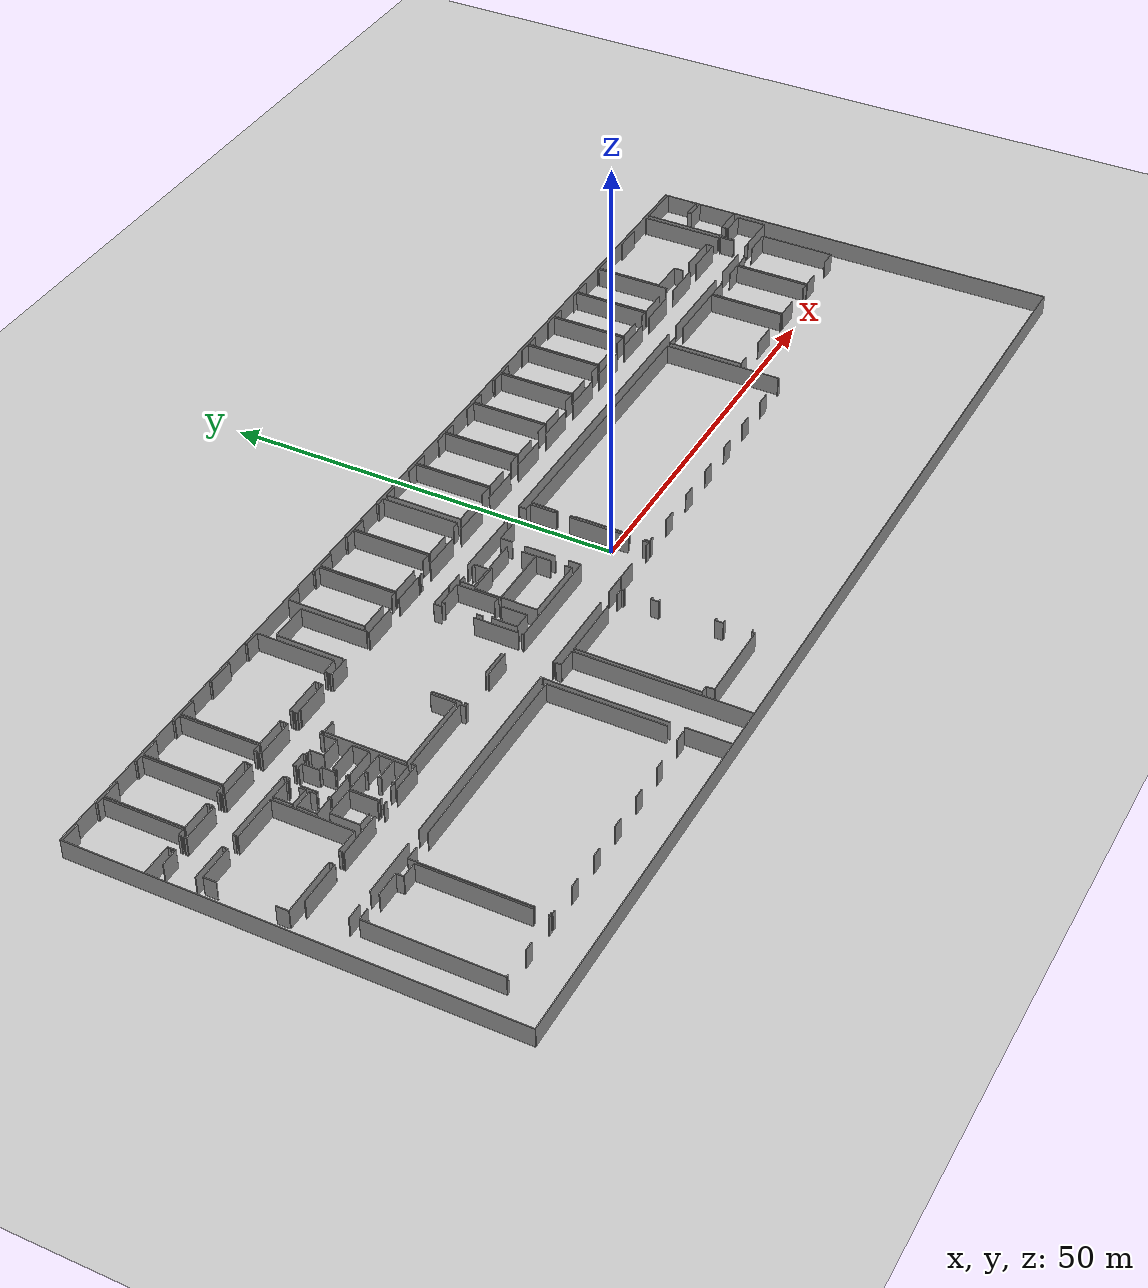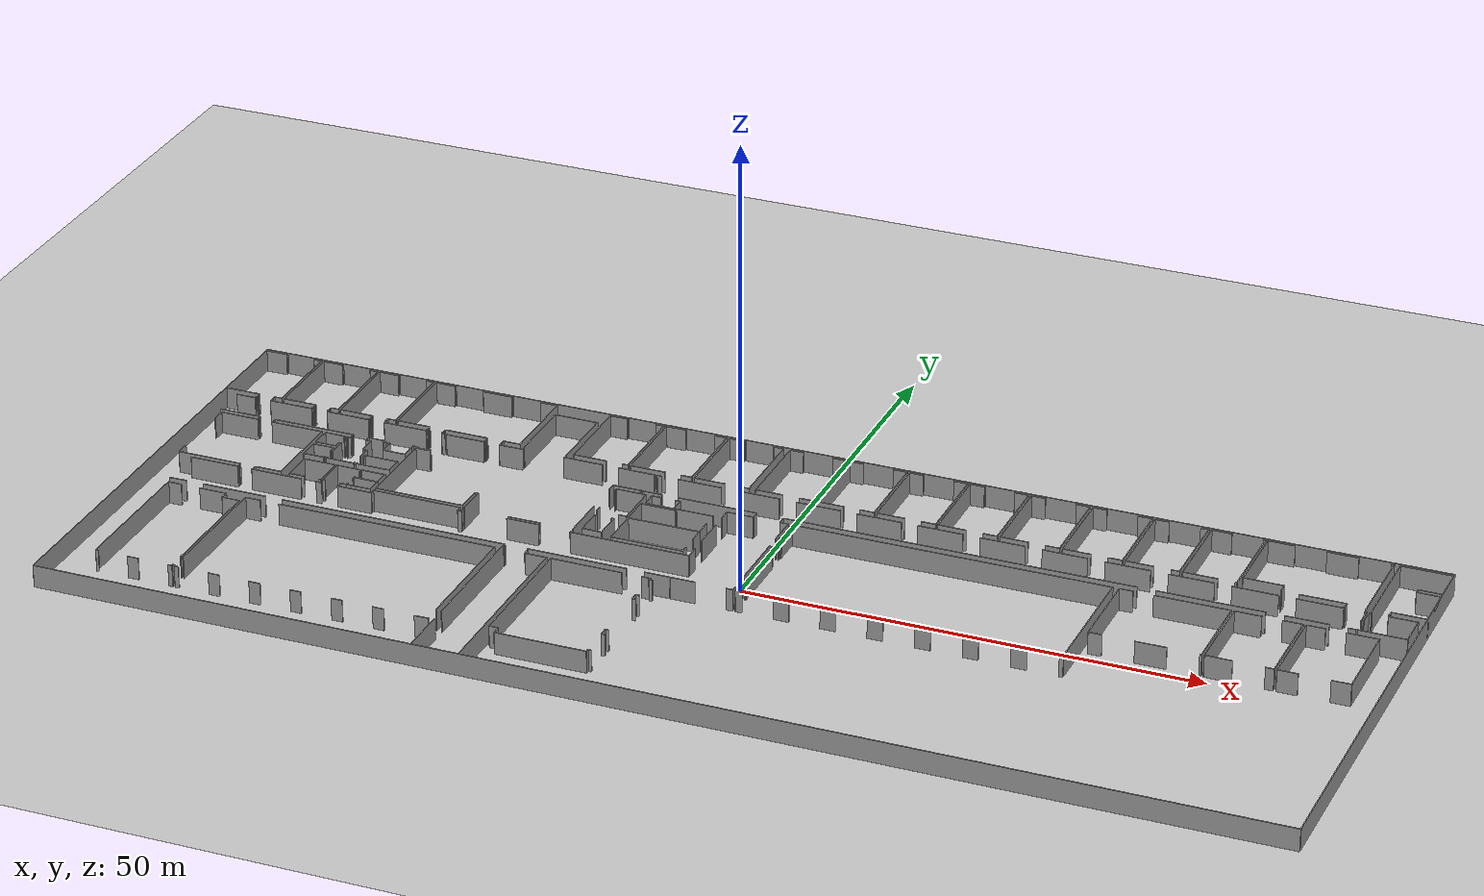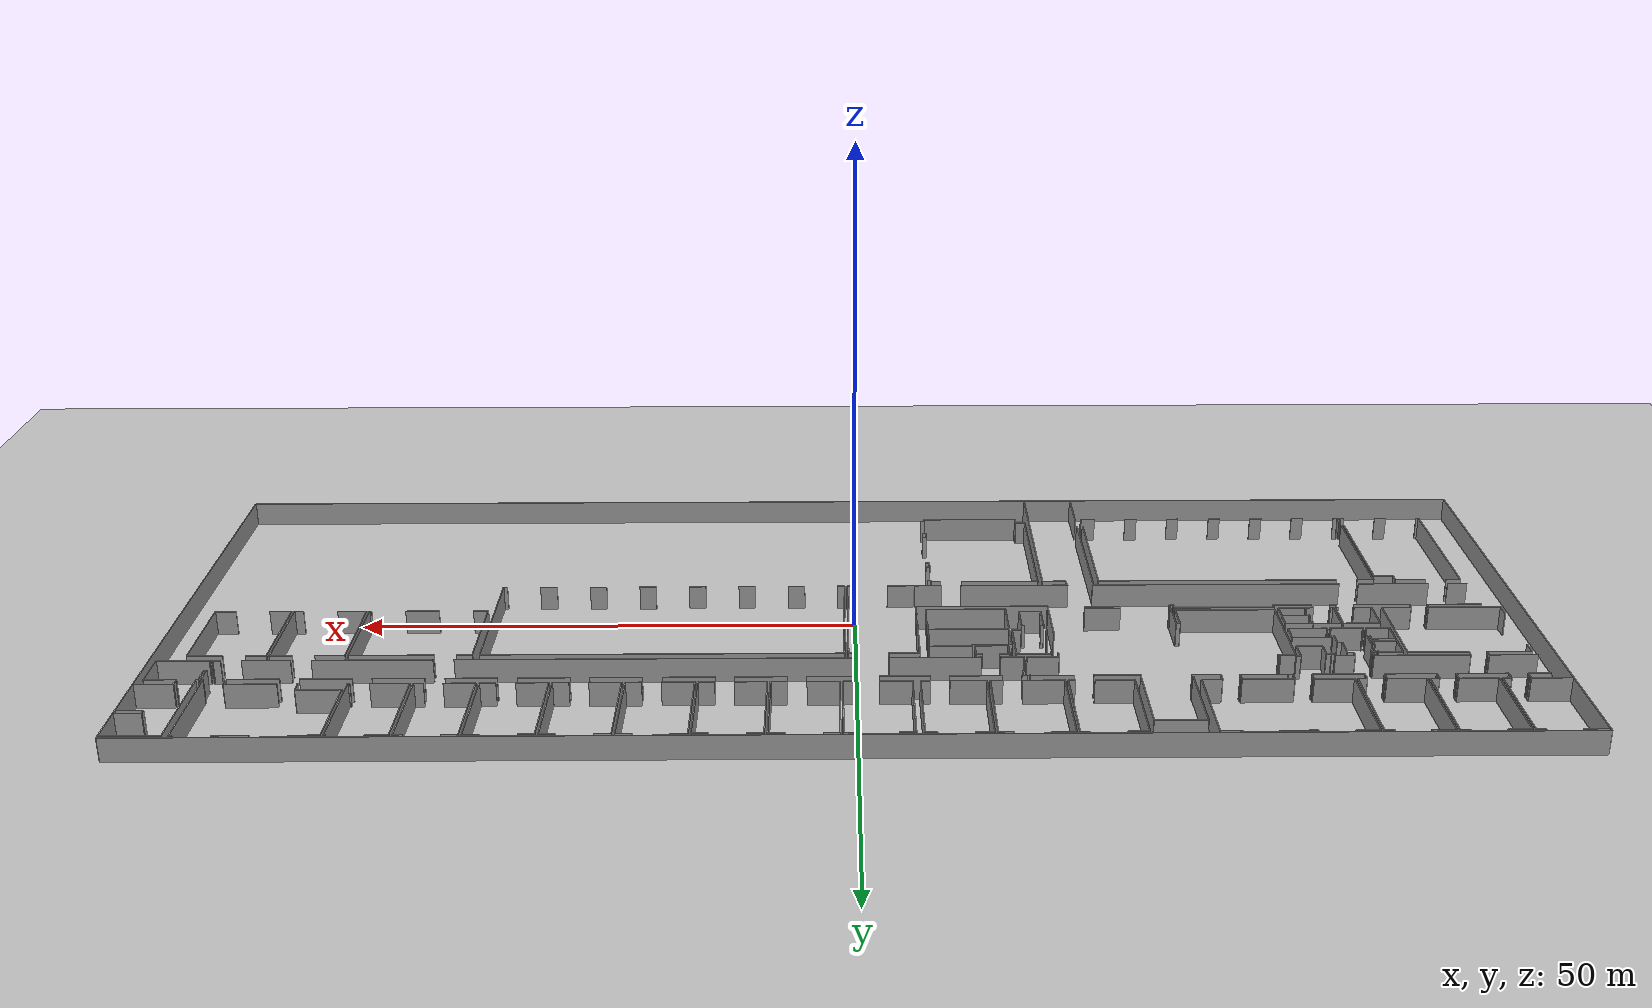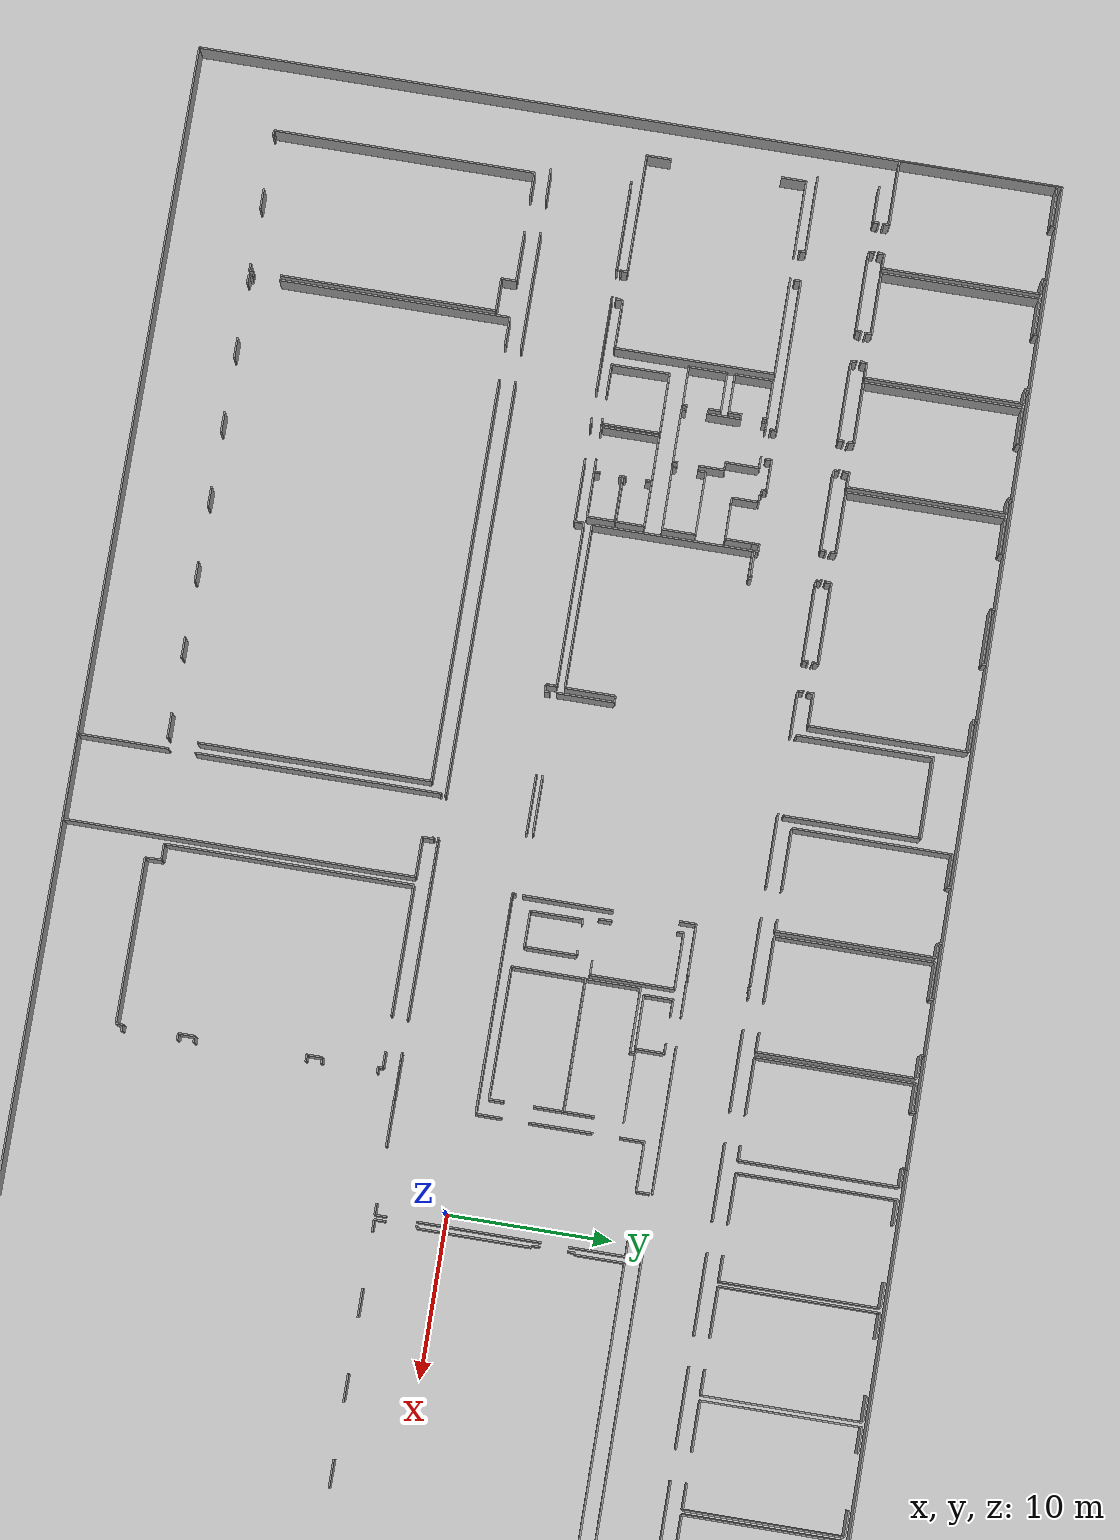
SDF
<sdf version="1.6">
  <world name="default">
    <light name="sun" type="directional">
      <cast_shadows>1</cast_shadows>
      <pose frame="">0 0 10 0 -0 0</pose>
      <diffuse>0.8 0.8 0.8 1</diffuse>
      <specular>0.1 0.1 0.1 1</specular>
      <attenuation>
        <range>1000</range>
        <constant>0.9</constant>
        <linear>0.01</linear>
        <quadratic>0.001</quadratic>
      </attenuation>
      <direction>-0.5 0.5 -1</direction>
    </light>
    <model name="ground_plane">
      <static>1</static>
      <link name="link">
        <collision name="collision">
          <geometry>
            <plane>
              <normal>0 0 1</normal>
              <size>100 100</size>
            </plane>
          </geometry>
          <surface>
            <friction>
              <ode>
                <mu>100</mu>
                <mu2>50</mu2>
              </ode>
              <torsional>
                <ode />
              </torsional>
            </friction>
            <contact>
              <ode />
            </contact>
            <bounce />
          </surface>
          <max_contacts>10</max_contacts>
        </collision>
        <visual name="visual">
          <cast_shadows>0</cast_shadows>
          <geometry>
            <plane>
              <normal>0 0 1</normal>
              <size>100 100</size>
            </plane>
          </geometry>
          <material>
            <script>
              <uri>file://media/materials/scripts/gazebo.material</uri>
              <name>Gazebo/Grey</name>
            </script>
          </material>
        </visual>
        <self_collide>0</self_collide>
        <kinematic>0</kinematic>
        <gravity>1</gravity>
      </link>
    </model>
    <gravity>0 0 -9.8</gravity>
    <magnetic_field>6e-06 2.3e-05 -4.2e-05</magnetic_field>
    <atmosphere type="adiabatic" />
    <physics default="0" name="default_physics" type="ode">
      <max_step_size>0.001</max_step_size>
      <real_time_factor>1</real_time_factor>
      <real_time_update_rate>1000</real_time_update_rate>
    </physics>
    <scene>
      <ambient>0.4 0.4 0.4 1</ambient>
      <background>0.7 0.7 0.7 1</background>
      <shadows>1</shadows>
    </scene>
    <spherical_coordinates>
      <surface_model>EARTH_WGS84</surface_model>
      <latitude_deg>0</latitude_deg>
      <longitude_deg>0</longitude_deg>
      <elevation>0</elevation>
      <heading_deg>0</heading_deg>
    </spherical_coordinates>
  <model name="0510032192_A_40_1_103">
		<static>1</static>
		<link name="Wall_0">
			<collision name="Wall_0_Collision">
				<geometry>
					<box>
						<size>9.71681933099 0.1 2.5</size>
					</box>
				</geometry>
				<pose frame="">4.85840966549 0 1.25 0 0 0</pose>
			</collision>
			<visual name="Wall_0_Visual">
				<pose frame="">4.85840966549 0 1.25 0 0 0</pose>
				<geometry>
					<box>
						<size>9.71681933099 0.1 2.5</size>
					</box>
				</geometry>
				<material>
					<script>
						<uri>file://media/materials/scripts/gazebo.material</uri>
						<name>Gazebo/Grey</name>
					</script>
					<ambient>1 1 1 1</ambient>
				</material>
			</visual>
			<pose frame="">7.03149416234 -10.0356993127 0 0 0 1.57079632679</pose>
		</link>
		<link name="Wall_1">
			<collision name="Wall_1_Collision">
				<geometry>
					<box>
						<size>2.24219633352 0.1 2.5</size>
					</box>
				</geometry>
				<pose frame="">1.12109816676 0 1.25 0 0 0</pose>
			</collision>
			<visual name="Wall_1_Visual">
				<pose frame="">1.12109816676 0 1.25 0 0 0</pose>
				<geometry>
					<box>
						<size>2.24219633352 0.1 2.5</size>
					</box>
				</geometry>
				<material>
					<script>
						<uri>file://media/materials/scripts/gazebo.material</uri>
						<name>Gazebo/Grey</name>
					</script>
					<ambient>1 1 1 1</ambient>
				</material>
			</visual>
			<pose frame="">7.03149416234 -0.318879981706 0 0 0 0.0</pose>
		</link>
		<link name="Wall_2">
			<collision name="Wall_2_Collision">
				<geometry>
					<box>
						<size>0.290549210423 0.1 2.5</size>
					</box>
				</geometry>
				<pose frame="">0.145274605211 0 1.25 0 0 0</pose>
			</collision>
			<visual name="Wall_2_Visual">
				<pose frame="">0.145274605211 0 1.25 0 0 0</pose>
				<geometry>
					<box>
						<size>0.290549210423 0.1 2.5</size>
					</box>
				</geometry>
				<material>
					<script>
						<uri>file://media/materials/scripts/gazebo.material</uri>
						<name>Gazebo/Grey</name>
					</script>
					<ambient>1 1 1 1</ambient>
				</material>
			</visual>
			<pose frame="">9.27369049585 -0.318879981706 0 0 0 1.57079632679</pose>
		</link>
		<link name="Wall_3">
			<collision name="Wall_3_Collision">
				<geometry>
					<box>
						<size>0.278861179221 0.1 2.5</size>
					</box>
				</geometry>
				<pose frame="">0.13943058961 0 1.25 0 0 0</pose>
			</collision>
			<visual name="Wall_3_Visual">
				<pose frame="">0.13943058961 0 1.25 0 0 0</pose>
				<geometry>
					<box>
						<size>0.278861179221 0.1 2.5</size>
					</box>
				</geometry>
				<material>
					<script>
						<uri>file://media/materials/scripts/gazebo.material</uri>
						<name>Gazebo/Grey</name>
					</script>
					<ambient>1 1 1 1</ambient>
				</material>
			</visual>
			<pose frame="">12.6765591452 -0.028330771283 0 0 0 -1.57079632679</pose>
		</link>
		<link name="Wall_4">
			<collision name="Wall_4_Collision">
				<geometry>
					<box>
						<size>0.913826178649 0.1 2.5</size>
					</box>
				</geometry>
				<pose frame="">0.456913089325 0 1.25 0 0 0</pose>
			</collision>
			<visual name="Wall_4_Visual">
				<pose frame="">0.456913089325 0 1.25 0 0 0</pose>
				<geometry>
					<box>
						<size>0.913826178649 0.1 2.5</size>
					</box>
				</geometry>
				<material>
					<script>
						<uri>file://media/materials/scripts/gazebo.material</uri>
						<name>Gazebo/Grey</name>
					</script>
					<ambient>1 1 1 1</ambient>
				</material>
			</visual>
			<pose frame="">12.6765591452 -0.307191950504 0 0 0 0.0</pose>
		</link>
		<link name="Wall_5">
			<collision name="Wall_5_Collision">
				<geometry>
					<box>
						<size>9.72431491621 0.1 2.5</size>
					</box>
				</geometry>
				<pose frame="">4.86215745811 0 1.25 0 0 0</pose>
			</collision>
			<visual name="Wall_5_Visual">
				<pose frame="">4.86215745811 0 1.25 0 0 0</pose>
				<geometry>
					<box>
						<size>9.72431491621 0.1 2.5</size>
					</box>
				</geometry>
				<material>
					<script>
						<uri>file://media/materials/scripts/gazebo.material</uri>
						<name>Gazebo/Grey</name>
					</script>
					<ambient>1 1 1 1</ambient>
				</material>
			</visual>
			<pose frame="">13.5903853239 -0.307191950504 0 0 0 -1.57079632679</pose>
		</link>
		<link name="Wall_6">
			<collision name="Wall_6_Collision">
				<geometry>
					<box>
						<size>0.908744425953 0.1 2.5</size>
					</box>
				</geometry>
				<pose frame="">0.454372212976 0 1.25 0 0 0</pose>
			</collision>
			<visual name="Wall_6_Visual">
				<pose frame="">0.454372212976 0 1.25 0 0 0</pose>
				<geometry>
					<box>
						<size>0.908744425953 0.1 2.5</size>
					</box>
				</geometry>
				<material>
					<script>
						<uri>file://media/materials/scripts/gazebo.material</uri>
						<name>Gazebo/Grey</name>
					</script>
					<ambient>1 1 1 1</ambient>
				</material>
			</visual>
			<pose frame="">13.5903853239 -10.0315068667 0 0 0 3.14159265359</pose>
		</link>
		<link name="Wall_7">
			<collision name="Wall_7_Collision">
				<geometry>
					<box>
						<size>0.373762910828 0.1 2.5</size>
					</box>
				</geometry>
				<pose frame="">0.186881455414 0 1.25 0 0 0</pose>
			</collision>
			<visual name="Wall_7_Visual">
				<pose frame="">0.186881455414 0 1.25 0 0 0</pose>
				<geometry>
					<box>
						<size>0.373762910828 0.1 2.5</size>
					</box>
				</geometry>
				<material>
					<script>
						<uri>file://media/materials/scripts/gazebo.material</uri>
						<name>Gazebo/Grey</name>
					</script>
					<ambient>1 1 1 1</ambient>
				</material>
			</visual>
			<pose frame="">12.6816408979 -10.0315068667 0 0 0 -1.57079632679</pose>
		</link>
		<link name="Wall_8">
			<collision name="Wall_8_Collision">
				<geometry>
					<box>
						<size>0.0913445047197 0.1 2.5</size>
					</box>
				</geometry>
				<pose frame="">0.0456722523598 0 1.25 0 0 0</pose>
			</collision>
			<visual name="Wall_8_Visual">
				<pose frame="">0.0456722523598 0 1.25 0 0 0</pose>
				<geometry>
					<box>
						<size>0.0913445047197 0.1 2.5</size>
					</box>
				</geometry>
				<material>
					<script>
						<uri>file://media/materials/scripts/gazebo.material</uri>
						<name>Gazebo/Grey</name>
					</script>
					<ambient>1 1 1 1</ambient>
				</material>
			</visual>
			<pose frame="">12.6816408979 -10.4052697775 0 0 0 3.14159265359</pose>
		</link>
		<link name="Wall_9">
			<collision name="Wall_9_Collision">
				<geometry>
					<box>
						<size>0.0877872778321 0.1 2.5</size>
					</box>
				</geometry>
				<pose frame="">0.0438936389161 0 1.25 0 0 0</pose>
			</collision>
			<visual name="Wall_9_Visual">
				<pose frame="">0.0438936389161 0 1.25 0 0 0</pose>
				<geometry>
					<box>
						<size>0.0877872778321 0.1 2.5</size>
					</box>
				</geometry>
				<material>
					<script>
						<uri>file://media/materials/scripts/gazebo.material</uri>
						<name>Gazebo/Grey</name>
					</script>
					<ambient>1 1 1 1</ambient>
				</material>
			</visual>
			<pose frame="">10.9331368389 -10.4052697775 0 0 0 3.14159265359</pose>
		</link>
		<link name="Wall_10">
			<collision name="Wall_10_Collision">
				<geometry>
					<box>
						<size>0.379861014064 0.1 2.5</size>
					</box>
				</geometry>
				<pose frame="">0.189930507032 0 1.25 0 0 0</pose>
			</collision>
			<visual name="Wall_10_Visual">
				<pose frame="">0.189930507032 0 1.25 0 0 0</pose>
				<geometry>
					<box>
						<size>0.379861014064 0.1 2.5</size>
					</box>
				</geometry>
				<material>
					<script>
						<uri>file://media/materials/scripts/gazebo.material</uri>
						<name>Gazebo/Grey</name>
					</script>
					<ambient>1 1 1 1</ambient>
				</material>
			</visual>
			<pose frame="">10.8453495611 -10.4052697775 0 0 0 1.57079632679</pose>
		</link>
		<link name="Wall_11">
			<collision name="Wall_11_Collision">
				<geometry>
					<box>
						<size>3.81386928169 0.1 2.5</size>
					</box>
				</geometry>
				<pose frame="">1.90693464084 0 1.25 0 0 0</pose>
			</collision>
			<visual name="Wall_11_Visual">
				<pose frame="">1.90693464084 0 1.25 0 0 0</pose>
				<geometry>
					<box>
						<size>3.81386928169 0.1 2.5</size>
					</box>
				</geometry>
				<material>
					<script>
						<uri>file://media/materials/scripts/gazebo.material</uri>
						<name>Gazebo/Grey</name>
					</script>
					<ambient>1 1 1 1</ambient>
				</material>
			</visual>
			<pose frame="">10.8453495611 -10.0254087635 0 0 0 -3.13889445894</pose>
		</link>
		<link name="Wall_12">
			<collision name="Wall_12_Collision">
				<geometry>
					<box>
						<size>4.01217079771 0.1 2.5</size>
					</box>
				</geometry>
				<pose frame="">2.00608539885 0 1.25 0 0 0</pose>
			</collision>
			<visual name="Wall_12_Visual">
				<pose frame="">2.00608539885 0 1.25 0 0 0</pose>
				<geometry>
					<box>
						<size>4.01217079771 0.1 2.5</size>
					</box>
				</geometry>
				<material>
					<script>
						<uri>file://media/materials/scripts/gazebo.material</uri>
						<name>Gazebo/Grey</name>
					</script>
					<ambient>1 1 1 1</ambient>
				</material>
			</visual>
			<pose frame="">0.0 -10.0289659904 0 0 0 0.0</pose>
		</link>
		<link name="Wall_13">
			<collision name="Wall_13_Collision">
				<geometry>
					<box>
						<size>0.37071385921 0.1 2.5</size>
					</box>
				</geometry>
				<pose frame="">0.185356929605 0 1.25 0 0 0</pose>
			</collision>
			<visual name="Wall_13_Visual">
				<pose frame="">0.185356929605 0 1.25 0 0 0</pose>
				<geometry>
					<box>
						<size>0.37071385921 0.1 2.5</size>
					</box>
				</geometry>
				<material>
					<script>
						<uri>file://media/materials/scripts/gazebo.material</uri>
						<name>Gazebo/Grey</name>
					</script>
					<ambient>1 1 1 1</ambient>
				</material>
			</visual>
			<pose frame="">4.01217079771 -10.0289659904 0 0 0 -1.57079632679</pose>
		</link>
		<link name="Wall_14">
			<collision name="Wall_14_Collision">
				<geometry>
					<box>
						<size>0.0757181151779 0.1 2.5</size>
					</box>
				</geometry>
				<pose frame="">0.037859057589 0 1.25 0 0 0</pose>
			</collision>
			<visual name="Wall_14_Visual">
				<pose frame="">0.037859057589 0 1.25 0 0 0</pose>
				<geometry>
					<box>
						<size>0.0757181151779 0.1 2.5</size>
					</box>
				</geometry>
				<material>
					<script>
						<uri>file://media/materials/scripts/gazebo.material</uri>
						<name>Gazebo/Grey</name>
					</script>
					<ambient>1 1 1 1</ambient>
				</material>
			</visual>
			<pose frame="">4.01217079771 -10.3996798496 0 0 0 0.0</pose>
		</link>
		<link name="Wall_15">
			<collision name="Wall_15_Collision">
				<geometry>
					<box>
						<size>0.100237571939 0.1 2.5</size>
					</box>
				</geometry>
				<pose frame="">0.0501187859693 0 1.25 0 0 0</pose>
			</collision>
			<visual name="Wall_15_Visual">
				<pose frame="">0.0501187859693 0 1.25 0 0 0</pose>
				<geometry>
					<box>
						<size>0.100237571939 0.1 2.5</size>
					</box>
				</geometry>
				<material>
					<script>
						<uri>file://media/materials/scripts/gazebo.material</uri>
						<name>Gazebo/Grey</name>
					</script>
					<ambient>1 1 1 1</ambient>
				</material>
			</visual>
			<pose frame="">5.76181825111 -10.3996798496 0 0 0 0.0</pose>
		</link>
		<link name="Wall_16">
			<collision name="Wall_16_Collision">
				<geometry>
					<box>
						<size>0.363980536887 0.1 2.5</size>
					</box>
				</geometry>
				<pose frame="">0.181990268444 0 1.25 0 0 0</pose>
			</collision>
			<visual name="Wall_16_Visual">
				<pose frame="">0.181990268444 0 1.25 0 0 0</pose>
				<geometry>
					<box>
						<size>0.363980536887 0.1 2.5</size>
					</box>
				</geometry>
				<material>
					<script>
						<uri>file://media/materials/scripts/gazebo.material</uri>
						<name>Gazebo/Grey</name>
					</script>
					<ambient>1 1 1 1</ambient>
				</material>
			</visual>
			<pose frame="">5.86205582305 -10.3996798496 0 0 0 1.57079632679</pose>
		</link>
		<link name="Wall_17">
			<collision name="Wall_17_Collision">
				<geometry>
					<box>
						<size>0.885368363549 0.1 2.5</size>
					</box>
				</geometry>
				<pose frame="">0.442684181774 0 1.25 0 0 0</pose>
			</collision>
			<visual name="Wall_17_Visual">
				<pose frame="">0.442684181774 0 1.25 0 0 0</pose>
				<geometry>
					<box>
						<size>0.885368363549 0.1 2.5</size>
					</box>
				</geometry>
				<material>
					<script>
						<uri>file://media/materials/scripts/gazebo.material</uri>
						<name>Gazebo/Grey</name>
					</script>
					<ambient>1 1 1 1</ambient>
				</material>
			</visual>
			<pose frame="">5.86205582305 -10.0356993127 0 0 0 0.0</pose>
		</link>
		<link name="Wall_18">
			<collision name="Wall_18_Collision">
				<geometry>
					<box>
						<size>9.72317152186 0.1 2.5</size>
					</box>
				</geometry>
				<pose frame="">4.86158576093 0 1.25 0 0 0</pose>
			</collision>
			<visual name="Wall_18_Visual">
				<pose frame="">4.86158576093 0 1.25 0 0 0</pose>
				<geometry>
					<box>
						<size>9.72317152186 0.1 2.5</size>
					</box>
				</geometry>
				<material>
					<script>
						<uri>file://media/materials/scripts/gazebo.material</uri>
						<name>Gazebo/Grey</name>
					</script>
					<ambient>1 1 1 1</ambient>
				</material>
			</visual>
			<pose frame="">6.7474241866 -10.0356993127 0 0 0 1.57079632679</pose>
		</link>
		<link name="Wall_19">
			<collision name="Wall_19_Collision">
				<geometry>
					<box>
						<size>0.909887820309 0.1 2.5</size>
					</box>
				</geometry>
				<pose frame="">0.454943910155 0 1.25 0 0 0</pose>
			</collision>
			<visual name="Wall_19_Visual">
				<pose frame="">0.454943910155 0 1.25 0 0 0</pose>
				<geometry>
					<box>
						<size>0.909887820309 0.1 2.5</size>
					</box>
				</geometry>
				<material>
					<script>
						<uri>file://media/materials/scripts/gazebo.material</uri>
						<name>Gazebo/Grey</name>
					</script>
					<ambient>1 1 1 1</ambient>
				</material>
			</visual>
			<pose frame="">6.7474241866 -0.312527790835 0 0 0 3.14159265359</pose>
		</link>
		<link name="Wall_20">
			<collision name="Wall_20_Collision">
				<geometry>
					<box>
						<size>0.277844828681 0.1 2.5</size>
					</box>
				</geometry>
				<pose frame="">0.138922414341 0 1.25 0 0 0</pose>
			</collision>
			<visual name="Wall_20_Visual">
				<pose frame="">0.138922414341 0 1.25 0 0 0</pose>
				<geometry>
					<box>
						<size>0.277844828681 0.1 2.5</size>
					</box>
				</geometry>
				<material>
					<script>
						<uri>file://media/materials/scripts/gazebo.material</uri>
						<name>Gazebo/Grey</name>
					</script>
					<ambient>1 1 1 1</ambient>
				</material>
			</visual>
			<pose frame="">5.83753636629 -0.312527790835 0 0 0 1.57079632679</pose>
		</link>
		<link name="Wall_21">
			<collision name="Wall_21_Collision">
				<geometry>
					<box>
						<size>0.277844828681 0.1 2.5</size>
					</box>
				</geometry>
				<pose frame="">0.138922414341 0 1.25 0 0 0</pose>
			</collision>
			<visual name="Wall_21_Visual">
				<pose frame="">0.138922414341 0 1.25 0 0 0</pose>
				<geometry>
					<box>
						<size>0.277844828681 0.1 2.5</size>
					</box>
				</geometry>
				<material>
					<script>
						<uri>file://media/materials/scripts/gazebo.material</uri>
						<name>Gazebo/Grey</name>
					</script>
					<ambient>1 1 1 1</ambient>
				</material>
			</visual>
			<pose frame="">2.4646500578 -0.0346829621536 0 0 0 -1.57079632679</pose>
		</link>
		<link name="Wall_22">
			<collision name="Wall_22_Collision">
				<geometry>
					<box>
						<size>2.45702742876 0.1 2.5</size>
					</box>
				</geometry>
				<pose frame="">1.22851371438 0 1.25 0 0 0</pose>
			</collision>
			<visual name="Wall_22_Visual">
				<pose frame="">1.22851371438 0 1.25 0 0 0</pose>
				<geometry>
					<box>
						<size>2.45702742876 0.1 2.5</size>
					</box>
				</geometry>
				<material>
					<script>
						<uri>file://media/materials/scripts/gazebo.material</uri>
						<name>Gazebo/Grey</name>
					</script>
					<ambient>1 1 1 1</ambient>
				</material>
			</visual>
			<pose frame="">2.4646500578 -0.312527790835 0 0 0 3.14159265359</pose>
		</link>
		<link name="Wall_23">
			<collision name="Wall_23_Collision">
				<geometry>
					<box>
						<size>9.71644118954 0.1 2.5</size>
					</box>
				</geometry>
				<pose frame="">4.85822059477 0 1.25 0 0 0</pose>
			</collision>
			<visual name="Wall_23_Visual">
				<pose frame="">4.85822059477 0 1.25 0 0 0</pose>
				<geometry>
					<box>
						<size>9.71644118954 0.1 2.5</size>
					</box>
				</geometry>
				<material>
					<script>
						<uri>file://media/materials/scripts/gazebo.material</uri>
						<name>Gazebo/Grey</name>
					</script>
					<ambient>1 1 1 1</ambient>
				</material>
			</visual>
			<pose frame="">0.00762262904476 -0.312527790835 0 0 0 -1.5715808352</pose>
		</link>
		<link name="Wall_24">
			<collision name="Wall_24_Collision">
				<geometry>
					<box>
						<size>9.72469604767 0.1 2.5</size>
					</box>
				</geometry>
				<pose frame="">4.86234802383 0 1.25 0 0 0</pose>
			</collision>
			<visual name="Wall_24_Visual">
				<pose frame="">4.86234802383 0 1.25 0 0 0</pose>
				<geometry>
					<box>
						<size>9.72469604767 0.1 2.5</size>
					</box>
				</geometry>
				<material>
					<script>
						<uri>file://media/materials/scripts/gazebo.material</uri>
						<name>Gazebo/Grey</name>
					</script>
					<ambient>1 1 1 1</ambient>
				</material>
			</visual>
			<pose frame="">13.8593370854 -10.033412524 0 0 0 1.57079632679</pose>
		</link>
		<link name="Wall_25">
			<collision name="Wall_25_Collision">
				<geometry>
					<box>
						<size>2.23152465285 0.1 2.5</size>
					</box>
				</geometry>
				<pose frame="">1.11576232643 0 1.25 0 0 0</pose>
			</collision>
			<visual name="Wall_25_Visual">
				<pose frame="">1.11576232643 0 1.25 0 0 0</pose>
				<geometry>
					<box>
						<size>2.23152465285 0.1 2.5</size>
					</box>
				</geometry>
				<material>
					<script>
						<uri>file://media/materials/scripts/gazebo.material</uri>
						<name>Gazebo/Grey</name>
					</script>
					<ambient>1 1 1 1</ambient>
				</material>
			</visual>
			<pose frame="">13.8593370854 -0.308716476313 0 0 0 0.0</pose>
		</link>
		<link name="Wall_26">
			<collision name="Wall_26_Collision">
				<geometry>
					<box>
						<size>0.28330771283 0.1 2.5</size>
					</box>
				</geometry>
				<pose frame="">0.141653856415 0 1.25 0 0 0</pose>
			</collision>
			<visual name="Wall_26_Visual">
				<pose frame="">0.141653856415 0 1.25 0 0 0</pose>
				<geometry>
					<box>
						<size>0.28330771283 0.1 2.5</size>
					</box>
				</geometry>
				<material>
					<script>
						<uri>file://media/materials/scripts/gazebo.material</uri>
						<name>Gazebo/Grey</name>
					</script>
					<ambient>1 1 1 1</ambient>
				</material>
			</visual>
			<pose frame="">16.0908617382 -0.308716476313 0 0 0 1.57079632679</pose>
		</link>
		<link name="Wall_27">
			<collision name="Wall_27_Collision">
				<geometry>
					<box>
						<size>0.278607091586 0.1 2.5</size>
					</box>
				</geometry>
				<pose frame="">0.139303545793 0 1.25 0 0 0</pose>
			</collision>
			<visual name="Wall_27_Visual">
				<pose frame="">0.139303545793 0 1.25 0 0 0</pose>
				<geometry>
					<box>
						<size>0.278607091586 0.1 2.5</size>
					</box>
				</geometry>
				<material>
					<script>
						<uri>file://media/materials/scripts/gazebo.material</uri>
						<name>Gazebo/Grey</name>
					</script>
					<ambient>1 1 1 1</ambient>
				</material>
			</visual>
			<pose frame="">19.4880134158 -0.0254087634825 0 0 0 -1.57079632679</pose>
		</link>
		<link name="Wall_28">
			<collision name="Wall_28_Collision">
				<geometry>
					<box>
						<size>0.910650083214 0.1 2.5</size>
					</box>
				</geometry>
				<pose frame="">0.455325041607 0 1.25 0 0 0</pose>
			</collision>
			<visual name="Wall_28_Visual">
				<pose frame="">0.455325041607 0 1.25 0 0 0</pose>
				<geometry>
					<box>
						<size>0.910650083214 0.1 2.5</size>
					</box>
				</geometry>
				<material>
					<script>
						<uri>file://media/materials/scripts/gazebo.material</uri>
						<name>Gazebo/Grey</name>
					</script>
					<ambient>1 1 1 1</ambient>
				</material>
			</visual>
			<pose frame="">19.4880134158 -0.304015855068 0 0 0 0.0</pose>
		</link>
		<link name="Wall_29">
			<collision name="Wall_29_Collision">
				<geometry>
					<box>
						<size>9.72876144982 0.1 2.5</size>
					</box>
				</geometry>
				<pose frame="">4.86438072491 0 1.25 0 0 0</pose>
			</collision>
			<visual name="Wall_29_Visual">
				<pose frame="">4.86438072491 0 1.25 0 0 0</pose>
				<geometry>
					<box>
						<size>9.72876144982 0.1 2.5</size>
					</box>
				</geometry>
				<material>
					<script>
						<uri>file://media/materials/scripts/gazebo.material</uri>
						<name>Gazebo/Grey</name>
					</script>
					<ambient>1 1 1 1</ambient>
				</material>
			</visual>
			<pose frame="">20.398663499 -0.304015855068 0 0 0 -1.57079632679</pose>
		</link>
		<link name="Wall_30">
			<collision name="Wall_30_Collision">
				<geometry>
					<box>
						<size>0.894007343133 0.1 2.5</size>
					</box>
				</geometry>
				<pose frame="">0.447003671566 0 1.25 0 0 0</pose>
			</collision>
			<visual name="Wall_30_Visual">
				<pose frame="">0.447003671566 0 1.25 0 0 0</pose>
				<geometry>
					<box>
						<size>0.894007343133 0.1 2.5</size>
					</box>
				</geometry>
				<material>
					<script>
						<uri>file://media/materials/scripts/gazebo.material</uri>
						<name>Gazebo/Grey</name>
					</script>
					<ambient>1 1 1 1</ambient>
				</material>
			</visual>
			<pose frame="">20.398663499 -10.0327773049 0 0 0 3.14159265359</pose>
		</link>
		<link name="Wall_31">
			<collision name="Wall_31_Collision">
				<geometry>
					<box>
						<size>0.375541524272 0.1 2.5</size>
					</box>
				</geometry>
				<pose frame="">0.187770762136 0 1.25 0 0 0</pose>
			</collision>
			<visual name="Wall_31_Visual">
				<pose frame="">0.187770762136 0 1.25 0 0 0</pose>
				<geometry>
					<box>
						<size>0.375541524272 0.1 2.5</size>
					</box>
				</geometry>
				<material>
					<script>
						<uri>file://media/materials/scripts/gazebo.material</uri>
						<name>Gazebo/Grey</name>
					</script>
					<ambient>1 1 1 1</ambient>
				</material>
			</visual>
			<pose frame="">19.5046561559 -10.0327773049 0 0 0 -1.57079632679</pose>
		</link>
		<link name="Wall_32">
			<collision name="Wall_32_Collision">
				<geometry>
					<box>
						<size>0.0758451589953 0.1 2.5</size>
					</box>
				</geometry>
				<pose frame="">0.0379225794977 0 1.25 0 0 0</pose>
			</collision>
			<visual name="Wall_32_Visual">
				<pose frame="">0.0379225794977 0 1.25 0 0 0</pose>
				<geometry>
					<box>
						<size>0.0758451589953 0.1 2.5</size>
					</box>
				</geometry>
				<material>
					<script>
						<uri>file://media/materials/scripts/gazebo.material</uri>
						<name>Gazebo/Grey</name>
					</script>
					<ambient>1 1 1 1</ambient>
				</material>
			</visual>
			<pose frame="">19.5046561559 -10.4083188292 0 0 0 3.14159265359</pose>
		</link>
		<link name="Wall_33">
			<collision name="Wall_33_Collision">
				<geometry>
					<box>
						<size>0.11586396148 0.1 2.5</size>
					</box>
				</geometry>
				<pose frame="">0.0579319807402 0 1.25 0 0 0</pose>
			</collision>
			<visual name="Wall_33_Visual">
				<pose frame="">0.0579319807402 0 1.25 0 0 0</pose>
				<geometry>
					<box>
						<size>0.11586396148 0.1 2.5</size>
					</box>
				</geometry>
				<material>
					<script>
						<uri>file://media/materials/scripts/gazebo.material</uri>
						<name>Gazebo/Grey</name>
					</script>
					<ambient>1 1 1 1</ambient>
				</material>
			</visual>
			<pose frame="">17.7698728291 -10.4083188292 0 0 0 3.14159265359</pose>
		</link>
		<link name="Wall_34">
			<collision name="Wall_34_Collision">
				<geometry>
					<box>
						<size>0.3888811251 0.1 2.5</size>
					</box>
				</geometry>
				<pose frame="">0.19444056255 0 1.25 0 0 0</pose>
			</collision>
			<visual name="Wall_34_Visual">
				<pose frame="">0.19444056255 0 1.25 0 0 0</pose>
				<geometry>
					<box>
						<size>0.3888811251 0.1 2.5</size>
					</box>
				</geometry>
				<material>
					<script>
						<uri>file://media/materials/scripts/gazebo.material</uri>
						<name>Gazebo/Grey</name>
					</script>
					<ambient>1 1 1 1</ambient>
				</material>
			</visual>
			<pose frame="">17.6540088677 -10.4083188292 0 0 0 1.57079632679</pose>
		</link>
		<link name="Wall_35">
			<collision name="Wall_35_Collision">
				<geometry>
					<box>
						<size>3.79469751508 0.1 2.5</size>
					</box>
				</geometry>
				<pose frame="">1.89734875754 0 1.25 0 0 0</pose>
			</collision>
			<visual name="Wall_35_Visual">
				<pose frame="">1.89734875754 0 1.25 0 0 0</pose>
				<geometry>
					<box>
						<size>3.79469751508 0.1 2.5</size>
					</box>
				</geometry>
				<material>
					<script>
						<uri>file://media/materials/scripts/gazebo.material</uri>
						<name>Gazebo/Grey</name>
					</script>
					<ambient>1 1 1 1</ambient>
				</material>
			</visual>
			<pose frame="">17.6540088677 -10.0194377041 0 0 0 -3.13790992224</pose>
		</link>
		<link name="Wall_36">
			<collision name="Wall_36_Collision">
				<geometry>
					<box>
						<size>9.72749101165 0.1 2.5</size>
					</box>
				</geometry>
				<pose frame="">4.86374550582 0 1.25 0 0 0</pose>
			</collision>
			<visual name="Wall_36_Visual">
				<pose frame="">4.86374550582 0 1.25 0 0 0</pose>
				<geometry>
					<box>
						<size>9.72749101165 0.1 2.5</size>
					</box>
				</geometry>
				<material>
					<script>
						<uri>file://media/materials/scripts/gazebo.material</uri>
						<name>Gazebo/Grey</name>
					</script>
					<ambient>1 1 1 1</ambient>
				</material>
			</visual>
			<pose frame="">20.6921347173 -10.0289659904 0 0 0 1.57079632679</pose>
		</link>
		<link name="Wall_37">
			<collision name="Wall_37_Collision">
				<geometry>
					<box>
						<size>2.21208694879 0.1 2.5</size>
					</box>
				</geometry>
				<pose frame="">1.10604347439 0 1.25 0 0 0</pose>
			</collision>
			<visual name="Wall_37_Visual">
				<pose frame="">1.10604347439 0 1.25 0 0 0</pose>
				<geometry>
					<box>
						<size>2.21208694879 0.1 2.5</size>
					</box>
				</geometry>
				<material>
					<script>
						<uri>file://media/materials/scripts/gazebo.material</uri>
						<name>Gazebo/Grey</name>
					</script>
					<ambient>1 1 1 1</ambient>
				</material>
			</visual>
			<pose frame="">20.6921347173 -0.30147497872 0 0 0 0.0</pose>
		</link>
		<link name="Wall_38">
			<collision name="Wall_38_Collision">
				<geometry>
					<box>
						<size>0.28330771283 0.1 2.5</size>
					</box>
				</geometry>
				<pose frame="">0.141653856415 0 1.25 0 0 0</pose>
			</collision>
			<visual name="Wall_38_Visual">
				<pose frame="">0.141653856415 0 1.25 0 0 0</pose>
				<geometry>
					<box>
						<size>0.28330771283 0.1 2.5</size>
					</box>
				</geometry>
				<material>
					<script>
						<uri>file://media/materials/scripts/gazebo.material</uri>
						<name>Gazebo/Grey</name>
					</script>
					<ambient>1 1 1 1</ambient>
				</material>
			</visual>
			<pose frame="">22.9042216661 -0.30147497872 0 0 0 1.57079632679</pose>
		</link>
		<link name="Wall_39">
			<collision name="Wall_39_Collision">
				<geometry>
					<box>
						<size>0.279623442125 0.1 2.5</size>
					</box>
				</geometry>
				<pose frame="">0.139811721063 0 1.25 0 0 0</pose>
			</collision>
			<visual name="Wall_39_Visual">
				<pose frame="">0.139811721063 0 1.25 0 0 0</pose>
				<geometry>
					<box>
						<size>0.279623442125 0.1 2.5</size>
					</box>
				</geometry>
				<material>
					<script>
						<uri>file://media/materials/scripts/gazebo.material</uri>
						<name>Gazebo/Grey</name>
					</script>
					<ambient>1 1 1 1</ambient>
				</material>
			</visual>
			<pose frame="">26.3244953184 -0.01816726589 0 0 0 -1.57079632679</pose>
		</link>
		<link name="Wall_40">
			<collision name="Wall_40_Collision">
				<geometry>
					<box>
						<size>3.39765985288 0.1 2.5</size>
					</box>
				</geometry>
				<pose frame="">1.69882992644 0 1.25 0 0 0</pose>
			</collision>
			<visual name="Wall_40_Visual">
				<pose frame="">1.69882992644 0 1.25 0 0 0</pose>
				<geometry>
					<box>
						<size>3.39765985288 0.1 2.5</size>
					</box>
				</geometry>
				<material>
					<script>
						<uri>file://media/materials/scripts/gazebo.material</uri>
						<name>Gazebo/Grey</name>
					</script>
					<ambient>1 1 1 1</ambient>
				</material>
			</visual>
			<pose frame="">26.3244953184 -0.297790708015 0 0 0 0.0</pose>
		</link>
		<link name="Wall_41">
			<collision name="Wall_41_Collision">
				<geometry>
					<box>
						<size>0.280639792664 0.1 2.5</size>
					</box>
				</geometry>
				<pose frame="">0.140319896332 0 1.25 0 0 0</pose>
			</collision>
			<visual name="Wall_41_Visual">
				<pose frame="">0.140319896332 0 1.25 0 0 0</pose>
				<geometry>
					<box>
						<size>0.280639792664 0.1 2.5</size>
					</box>
				</geometry>
				<material>
					<script>
						<uri>file://media/materials/scripts/gazebo.material</uri>
						<name>Gazebo/Grey</name>
					</script>
					<ambient>1 1 1 1</ambient>
				</material>
			</visual>
			<pose frame="">29.7221551713 -0.297790708015 0 0 0 1.57079632679</pose>
		</link>
		<link name="Wall_42">
			<collision name="Wall_42_Collision">
				<geometry>
					<box>
						<size>0.281783187021 0.1 2.5</size>
					</box>
				</geometry>
				<pose frame="">0.140891593511 0 1.25 0 0 0</pose>
			</collision>
			<visual name="Wall_42_Visual">
				<pose frame="">0.140891593511 0 1.25 0 0 0</pose>
				<geometry>
					<box>
						<size>0.281783187021 0.1 2.5</size>
					</box>
				</geometry>
				<material>
					<script>
						<uri>file://media/materials/scripts/gazebo.material</uri>
						<name>Gazebo/Grey</name>
					</script>
					<ambient>1 1 1 1</ambient>
				</material>
			</visual>
			<pose frame="">33.1466212697 -0.0171509153507 0 0 0 -1.57079632679</pose>
		</link>
		<link name="Wall_43">
			<collision name="Wall_43_Collision">
				<geometry>
					<box>
						<size>1.98442442799 0.1 2.5</size>
					</box>
				</geometry>
				<pose frame="">0.992212213993 0 1.25 0 0 0</pose>
			</collision>
			<visual name="Wall_43_Visual">
				<pose frame="">0.992212213993 0 1.25 0 0 0</pose>
				<geometry>
					<box>
						<size>1.98442442799 0.1 2.5</size>
					</box>
				</geometry>
				<material>
					<script>
						<uri>file://media/materials/scripts/gazebo.material</uri>
						<name>Gazebo/Grey</name>
					</script>
					<ambient>1 1 1 1</ambient>
				</material>
			</visual>
			<pose frame="">33.1466212697 -0.298934102372 0 0 0 0.0</pose>
		</link>
		<link name="Wall_44">
			<collision name="Wall_44_Collision">
				<geometry>
					<box>
						<size>9.73740042941 0.1 2.5</size>
					</box>
				</geometry>
				<pose frame="">4.8687002147 0 1.25 0 0 0</pose>
			</collision>
			<visual name="Wall_44_Visual">
				<pose frame="">4.8687002147 0 1.25 0 0 0</pose>
				<geometry>
					<box>
						<size>9.73740042941 0.1 2.5</size>
					</box>
				</geometry>
				<material>
					<script>
						<uri>file://media/materials/scripts/gazebo.material</uri>
						<name>Gazebo/Grey</name>
					</script>
					<ambient>1 1 1 1</ambient>
				</material>
			</visual>
			<pose frame="">35.1310456977 -0.298934102372 0 0 0 -1.57079632679</pose>
		</link>
		<link name="Wall_45">
			<collision name="Wall_45_Collision">
				<geometry>
					<box>
						<size>1.97540431695 0.1 2.5</size>
					</box>
				</geometry>
				<pose frame="">0.987702158474 0 1.25 0 0 0</pose>
			</collision>
			<visual name="Wall_45_Visual">
				<pose frame="">0.987702158474 0 1.25 0 0 0</pose>
				<geometry>
					<box>
						<size>1.97540431695 0.1 2.5</size>
					</box>
				</geometry>
				<material>
					<script>
						<uri>file://media/materials/scripts/gazebo.material</uri>
						<name>Gazebo/Grey</name>
					</script>
					<ambient>1 1 1 1</ambient>
				</material>
			</visual>
			<pose frame="">35.1310456977 -10.0363345318 0 0 0 3.14159265359</pose>
		</link>
		<link name="Wall_46">
			<collision name="Wall_46_Collision">
				<geometry>
					<box>
						<size>0.368045939044 0.1 2.5</size>
					</box>
				</geometry>
				<pose frame="">0.184022969522 0 1.25 0 0 0</pose>
			</collision>
			<visual name="Wall_46_Visual">
				<pose frame="">0.184022969522 0 1.25 0 0 0</pose>
				<geometry>
					<box>
						<size>0.368045939044 0.1 2.5</size>
					</box>
				</geometry>
				<material>
					<script>
						<uri>file://media/materials/scripts/gazebo.material</uri>
						<name>Gazebo/Grey</name>
					</script>
					<ambient>1 1 1 1</ambient>
				</material>
			</visual>
			<pose frame="">33.1556413807 -10.0363345318 0 0 0 -1.57079632679</pose>
		</link>
		<link name="Wall_47">
			<collision name="Wall_47_Collision">
				<geometry>
					<box>
						<size>0.0823243936834 0.1 2.5</size>
					</box>
				</geometry>
				<pose frame="">0.0411621968417 0 1.25 0 0 0</pose>
			</collision>
			<visual name="Wall_47_Visual">
				<pose frame="">0.0411621968417 0 1.25 0 0 0</pose>
				<geometry>
					<box>
						<size>0.0823243936834 0.1 2.5</size>
					</box>
				</geometry>
				<material>
					<script>
						<uri>file://media/materials/scripts/gazebo.material</uri>
						<name>Gazebo/Grey</name>
					</script>
					<ambient>1 1 1 1</ambient>
				</material>
			</visual>
			<pose frame="">33.1556413807 -10.4043804708 0 0 0 3.14159265359</pose>
		</link>
		<link name="Wall_48">
			<collision name="Wall_48_Collision">
				<geometry>
					<box>
						<size>0.115228742393 0.1 2.5</size>
					</box>
				</geometry>
				<pose frame="">0.0576143711966 0 1.25 0 0 0</pose>
			</collision>
			<visual name="Wall_48_Visual">
				<pose frame="">0.0576143711966 0 1.25 0 0 0</pose>
				<geometry>
					<box>
						<size>0.115228742393 0.1 2.5</size>
					</box>
				</geometry>
				<material>
					<script>
						<uri>file://media/materials/scripts/gazebo.material</uri>
						<name>Gazebo/Grey</name>
					</script>
					<ambient>1 1 1 1</ambient>
				</material>
			</visual>
			<pose frame="">31.4127272496 -10.4043804708 0 0 0 3.14159265359</pose>
		</link>
		<link name="Wall_49">
			<collision name="Wall_49_Collision">
				<geometry>
					<box>
						<size>0.365759150331 0.1 2.5</size>
					</box>
				</geometry>
				<pose frame="">0.182879575165 0 1.25 0 0 0</pose>
			</collision>
			<visual name="Wall_49_Visual">
				<pose frame="">0.182879575165 0 1.25 0 0 0</pose>
				<geometry>
					<box>
						<size>0.365759150331 0.1 2.5</size>
					</box>
				</geometry>
				<material>
					<script>
						<uri>file://media/materials/scripts/gazebo.material</uri>
						<name>Gazebo/Grey</name>
					</script>
					<ambient>1 1 1 1</ambient>
				</material>
			</visual>
			<pose frame="">31.2974985072 -10.4043804708 0 0 0 1.57079632679</pose>
		</link>
		<link name="Wall_50">
			<collision name="Wall_50_Collision">
				<geometry>
					<box>
						<size>4.96639691029 0.1 2.5</size>
					</box>
				</geometry>
				<pose frame="">2.48319845515 0 1.25 0 0 0</pose>
			</collision>
			<visual name="Wall_50_Visual">
				<pose frame="">2.48319845515 0 1.25 0 0 0</pose>
				<geometry>
					<box>
						<size>4.96639691029 0.1 2.5</size>
					</box>
				</geometry>
				<material>
					<script>
						<uri>file://media/materials/scripts/gazebo.material</uri>
						<name>Gazebo/Grey</name>
					</script>
					<ambient>1 1 1 1</ambient>
				</material>
			</visual>
			<pose frame="">31.2974985072 -10.0386213205 0 0 0 3.14159265359</pose>
		</link>
		<link name="Wall_51">
			<collision name="Wall_51_Collision">
				<geometry>
					<box>
						<size>0.37122203448 0.1 2.5</size>
					</box>
				</geometry>
				<pose frame="">0.18561101724 0 1.25 0 0 0</pose>
			</collision>
			<visual name="Wall_51_Visual">
				<pose frame="">0.18561101724 0 1.25 0 0 0</pose>
				<geometry>
					<box>
						<size>0.37122203448 0.1 2.5</size>
					</box>
				</geometry>
				<material>
					<script>
						<uri>file://media/materials/scripts/gazebo.material</uri>
						<name>Gazebo/Grey</name>
					</script>
					<ambient>1 1 1 1</ambient>
				</material>
			</visual>
			<pose frame="">26.3311015969 -10.0386213205 0 0 0 -1.57079632679</pose>
		</link>
		<link name="Wall_52">
			<collision name="Wall_52_Collision">
				<geometry>
					<box>
						<size>0.0811809993267 0.1 2.5</size>
					</box>
				</geometry>
				<pose frame="">0.0405904996633 0 1.25 0 0 0</pose>
			</collision>
			<visual name="Wall_52_Visual">
				<pose frame="">0.0405904996633 0 1.25 0 0 0</pose>
				<geometry>
					<box>
						<size>0.0811809993267 0.1 2.5</size>
					</box>
				</geometry>
				<material>
					<script>
						<uri>file://media/materials/scripts/gazebo.material</uri>
						<name>Gazebo/Grey</name>
					</script>
					<ambient>1 1 1 1</ambient>
				</material>
			</visual>
			<pose frame="">26.3311015969 -10.409843355 0 0 0 3.14159265359</pose>
		</link>
		<link name="Wall_53">
			<collision name="Wall_53_Collision">
				<geometry>
					<box>
						<size>0.0879143216495 0.1 2.5</size>
					</box>
				</geometry>
				<pose frame="">0.0439571608248 0 1.25 0 0 0</pose>
			</collision>
			<visual name="Wall_53_Visual">
				<pose frame="">0.0439571608248 0 1.25 0 0 0</pose>
				<geometry>
					<box>
						<size>0.0879143216495 0.1 2.5</size>
					</box>
				</geometry>
				<material>
					<script>
						<uri>file://media/materials/scripts/gazebo.material</uri>
						<name>Gazebo/Grey</name>
					</script>
					<ambient>1 1 1 1</ambient>
				</material>
			</visual>
			<pose frame="">24.5764994347 -10.409843355 0 0 0 3.14159265359</pose>
		</link>
		<link name="Wall_54">
			<collision name="Wall_54_Collision">
				<geometry>
					<box>
						<size>0.373508823193 0.1 2.5</size>
					</box>
				</geometry>
				<pose frame="">0.186754411597 0 1.25 0 0 0</pose>
			</collision>
			<visual name="Wall_54_Visual">
				<pose frame="">0.186754411597 0 1.25 0 0 0</pose>
				<geometry>
					<box>
						<size>0.373508823193 0.1 2.5</size>
					</box>
				</geometry>
				<material>
					<script>
						<uri>file://media/materials/scripts/gazebo.material</uri>
						<name>Gazebo/Grey</name>
					</script>
					<ambient>1 1 1 1</ambient>
				</material>
			</visual>
			<pose frame="">24.488585113 -10.409843355 0 0 0 1.57079632679</pose>
		</link>
		<link name="Wall_55">
			<collision name="Wall_55_Collision">
				<geometry>
					<box>
						<size>3.79645754655 0.1 2.5</size>
					</box>
				</geometry>
				<pose frame="">1.89822877327 0 1.25 0 0 0</pose>
			</collision>
			<visual name="Wall_55_Visual">
				<pose frame="">1.89822877327 0 1.25 0 0 0</pose>
				<geometry>
					<box>
						<size>3.79645754655 0.1 2.5</size>
					</box>
				</geometry>
				<material>
					<script>
						<uri>file://media/materials/scripts/gazebo.material</uri>
						<name>Gazebo/Grey</name>
					</script>
					<ambient>1 1 1 1</ambient>
				</material>
			</visual>
			<pose frame="">24.488585113 -10.0363345318 0 0 0 3.13965175317</pose>
		</link>
		<link name="Wall_56">
			<collision name="Wall_56_Collision">
				<geometry>
					<box>
						<size>2.22326680472 0.1 2.5</size>
					</box>
				</geometry>
				<pose frame="">1.11163340236 0 1.25 0 0 0</pose>
			</collision>
			<visual name="Wall_56_Visual">
				<pose frame="">1.11163340236 0 1.25 0 0 0</pose>
				<geometry>
					<box>
						<size>2.22326680472 0.1 2.5</size>
					</box>
				</geometry>
				<material>
					<script>
						<uri>file://media/materials/scripts/gazebo.material</uri>
						<name>Gazebo/Grey</name>
					</script>
					<ambient>1 1 1 1</ambient>
				</material>
			</visual>
			<pose frame="">1.77619961125 -10.9997077992 0 0 0 0.0</pose>
		</link>
		<link name="Wall_57">
			<collision name="Wall_57_Collision">
				<geometry>
					<box>
						<size>0.322056077141 0.1 2.5</size>
					</box>
				</geometry>
				<pose frame="">0.161028038571 0 1.25 0 0 0</pose>
			</collision>
			<visual name="Wall_57_Visual">
				<pose frame="">0.161028038571 0 1.25 0 0 0</pose>
				<geometry>
					<box>
						<size>0.322056077141 0.1 2.5</size>
					</box>
				</geometry>
				<material>
					<script>
						<uri>file://media/materials/scripts/gazebo.material</uri>
						<name>Gazebo/Grey</name>
					</script>
					<ambient>1 1 1 1</ambient>
				</material>
			</visual>
			<pose frame="">3.99946641597 -10.9997077992 0 0 0 1.57079632679</pose>
		</link>
		<link name="Wall_58">
			<collision name="Wall_58_Collision">
				<geometry>
					<box>
						<size>0.0769885533521 0.1 2.5</size>
					</box>
				</geometry>
				<pose frame="">0.038494276676 0 1.25 0 0 0</pose>
			</collision>
			<visual name="Wall_58_Visual">
				<pose frame="">0.038494276676 0 1.25 0 0 0</pose>
				<geometry>
					<box>
						<size>0.0769885533521 0.1 2.5</size>
					</box>
				</geometry>
				<material>
					<script>
						<uri>file://media/materials/scripts/gazebo.material</uri>
						<name>Gazebo/Grey</name>
					</script>
					<ambient>1 1 1 1</ambient>
				</material>
			</visual>
			<pose frame="">3.99946641597 -10.6776517221 0 0 0 0.0</pose>
		</link>
		<link name="Wall_59">
			<collision name="Wall_59_Collision">
				<geometry>
					<box>
						<size>0.0919797238067 0.1 2.5</size>
					</box>
				</geometry>
				<pose frame="">0.0459898619034 0 1.25 0 0 0</pose>
			</collision>
			<visual name="Wall_59_Visual">
				<pose frame="">0.0459898619034 0 1.25 0 0 0</pose>
				<geometry>
					<box>
						<size>0.0919797238067 0.1 2.5</size>
					</box>
				</geometry>
				<material>
					<script>
						<uri>file://media/materials/scripts/gazebo.material</uri>
						<name>Gazebo/Grey</name>
					</script>
					<ambient>1 1 1 1</ambient>
				</material>
			</visual>
			<pose frame="">5.77007609925 -10.6776517221 0 0 0 0.0</pose>
		</link>
		<link name="Wall_60">
			<collision name="Wall_60_Collision">
				<geometry>
					<box>
						<size>0.310241002122 0.1 2.5</size>
					</box>
				</geometry>
				<pose frame="">0.155120501061 0 1.25 0 0 0</pose>
			</collision>
			<visual name="Wall_60_Visual">
				<pose frame="">0.155120501061 0 1.25 0 0 0</pose>
				<geometry>
					<box>
						<size>0.310241002122 0.1 2.5</size>
					</box>
				</geometry>
				<material>
					<script>
						<uri>file://media/materials/scripts/gazebo.material</uri>
						<name>Gazebo/Grey</name>
					</script>
					<ambient>1 1 1 1</ambient>
				</material>
			</visual>
			<pose frame="">5.86205582305 -10.6776517221 0 0 0 -1.57079632679</pose>
		</link>
		<link name="Wall_61">
			<collision name="Wall_61_Collision">
				<geometry>
					<box>
						<size>4.95534409818 0.1 2.5</size>
					</box>
				</geometry>
				<pose frame="">2.47767204909 0 1.25 0 0 0</pose>
			</collision>
			<visual name="Wall_61_Visual">
				<pose frame="">2.47767204909 0 1.25 0 0 0</pose>
				<geometry>
					<box>
						<size>4.95534409818 0.1 2.5</size>
					</box>
				</geometry>
				<material>
					<script>
						<uri>file://media/materials/scripts/gazebo.material</uri>
						<name>Gazebo/Grey</name>
					</script>
					<ambient>1 1 1 1</ambient>
				</material>
			</visual>
			<pose frame="">5.86205582305 -10.9878927242 0 0 0 0.0</pose>
		</link>
		<link name="Wall_62">
			<collision name="Wall_62_Collision">
				<geometry>
					<box>
						<size>0.306429687599 0.1 2.5</size>
					</box>
				</geometry>
				<pose frame="">0.1532148438 0 1.25 0 0 0</pose>
			</collision>
			<visual name="Wall_62_Visual">
				<pose frame="">0.1532148438 0 1.25 0 0 0</pose>
				<geometry>
					<box>
						<size>0.306429687599 0.1 2.5</size>
					</box>
				</geometry>
				<material>
					<script>
						<uri>file://media/materials/scripts/gazebo.material</uri>
						<name>Gazebo/Grey</name>
					</script>
					<ambient>1 1 1 1</ambient>
				</material>
			</visual>
			<pose frame="">10.8173999212 -10.9878927242 0 0 0 1.57079632679</pose>
		</link>
		<link name="Wall_63">
			<collision name="Wall_63_Collision">
				<geometry>
					<box>
						<size>0.0993482652167 0.1 2.5</size>
					</box>
				</geometry>
				<pose frame="">0.0496741326083 0 1.25 0 0 0</pose>
			</collision>
			<visual name="Wall_63_Visual">
				<pose frame="">0.0496741326083 0 1.25 0 0 0</pose>
				<geometry>
					<box>
						<size>0.0993482652167 0.1 2.5</size>
					</box>
				</geometry>
				<material>
					<script>
						<uri>file://media/materials/scripts/gazebo.material</uri>
						<name>Gazebo/Grey</name>
					</script>
					<ambient>1 1 1 1</ambient>
				</material>
			</visual>
			<pose frame="">10.8173999212 -10.6814630366 0 0 0 0.0</pose>
		</link>
		<link name="Wall_64">
			<collision name="Wall_64_Collision">
				<geometry>
					<box>
						<size>0.11688031202 0.1 2.5</size>
					</box>
				</geometry>
				<pose frame="">0.0584401560098 0 1.25 0 0 0</pose>
			</collision>
			<visual name="Wall_64_Visual">
				<pose frame="">0.0584401560098 0 1.25 0 0 0</pose>
				<geometry>
					<box>
						<size>0.11688031202 0.1 2.5</size>
					</box>
				</geometry>
				<material>
					<script>
						<uri>file://media/materials/scripts/gazebo.material</uri>
						<name>Gazebo/Grey</name>
					</script>
					<ambient>1 1 1 1</ambient>
				</material>
			</visual>
			<pose frame="">12.5864850787 -10.6814630366 0 0 0 0.0</pose>
		</link>
		<link name="Wall_65">
			<collision name="Wall_65_Collision">
				<geometry>
					<box>
						<size>0.310622133574 0.1 2.5</size>
					</box>
				</geometry>
				<pose frame="">0.155311066787 0 1.25 0 0 0</pose>
			</collision>
			<visual name="Wall_65_Visual">
				<pose frame="">0.155311066787 0 1.25 0 0 0</pose>
				<geometry>
					<box>
						<size>0.310622133574 0.1 2.5</size>
					</box>
				</geometry>
				<material>
					<script>
						<uri>file://media/materials/scripts/gazebo.material</uri>
						<name>Gazebo/Grey</name>
					</script>
					<ambient>1 1 1 1</ambient>
				</material>
			</visual>
			<pose frame="">12.7033653907 -10.6814630366 0 0 0 -1.57079632679</pose>
		</link>
		<link name="Wall_66">
			<collision name="Wall_66_Collision">
				<geometry>
					<box>
						<size>4.93057055378 0.1 2.5</size>
					</box>
				</geometry>
				<pose frame="">2.46528527689 0 1.25 0 0 0</pose>
			</collision>
			<visual name="Wall_66_Visual">
				<pose frame="">2.46528527689 0 1.25 0 0 0</pose>
				<geometry>
					<box>
						<size>4.93057055378 0.1 2.5</size>
					</box>
				</geometry>
				<material>
					<script>
						<uri>file://media/materials/scripts/gazebo.material</uri>
						<name>Gazebo/Grey</name>
					</script>
					<ambient>1 1 1 1</ambient>
				</material>
			</visual>
			<pose frame="">12.7033653907 -10.9920851702 0 0 0 0.0</pose>
		</link>
		<link name="Wall_67">
			<collision name="Wall_67_Collision">
				<geometry>
					<box>
						<size>0.32408877822 0.1 2.5</size>
					</box>
				</geometry>
				<pose frame="">0.16204438911 0 1.25 0 0 0</pose>
			</collision>
			<visual name="Wall_67_Visual">
				<pose frame="">0.16204438911 0 1.25 0 0 0</pose>
				<geometry>
					<box>
						<size>0.32408877822 0.1 2.5</size>
					</box>
				</geometry>
				<material>
					<script>
						<uri>file://media/materials/scripts/gazebo.material</uri>
						<name>Gazebo/Grey</name>
					</script>
					<ambient>1 1 1 1</ambient>
				</material>
			</visual>
			<pose frame="">17.6339359445 -10.9920851702 0 0 0 1.57079632679</pose>
		</link>
		<link name="Wall_68">
			<collision name="Wall_68_Collision">
				<geometry>
					<box>
						<size>0.0933772057983 0.1 2.5</size>
					</box>
				</geometry>
				<pose frame="">0.0466886028991 0 1.25 0 0 0</pose>
			</collision>
			<visual name="Wall_68_Visual">
				<pose frame="">0.0466886028991 0 1.25 0 0 0</pose>
				<geometry>
					<box>
						<size>0.0933772057983 0.1 2.5</size>
					</box>
				</geometry>
				<material>
					<script>
						<uri>file://media/materials/scripts/gazebo.material</uri>
						<name>Gazebo/Grey</name>
					</script>
					<ambient>1 1 1 1</ambient>
				</material>
			</visual>
			<pose frame="">17.6339359445 -10.667996392 0 0 0 0.0</pose>
		</link>
		<link name="Wall_69">
			<collision name="Wall_69_Collision">
				<geometry>
					<box>
						<size>0.0994753090341 0.1 2.5</size>
					</box>
				</geometry>
				<pose frame="">0.049737654517 0 1.25 0 0 0</pose>
			</collision>
			<visual name="Wall_69_Visual">
				<pose frame="">0.049737654517 0 1.25 0 0 0</pose>
				<geometry>
					<box>
						<size>0.0994753090341 0.1 2.5</size>
					</box>
				</geometry>
				<material>
					<script>
						<uri>file://media/materials/scripts/gazebo.material</uri>
						<name>Gazebo/Grey</name>
					</script>
					<ambient>1 1 1 1</ambient>
				</material>
			</visual>
			<pose frame="">19.4139468703 -10.667996392 0 0 0 0.0</pose>
		</link>
		<link name="Wall_70">
			<collision name="Wall_70_Collision">
				<geometry>
					<box>
						<size>0.314433448096 0.1 2.5</size>
					</box>
				</geometry>
				<pose frame="">0.157216724048 0 1.25 0 0 0</pose>
			</collision>
			<visual name="Wall_70_Visual">
				<pose frame="">0.157216724048 0 1.25 0 0 0</pose>
				<geometry>
					<box>
						<size>0.314433448096 0.1 2.5</size>
					</box>
				</geometry>
				<material>
					<script>
						<uri>file://media/materials/scripts/gazebo.material</uri>
						<name>Gazebo/Grey</name>
					</script>
					<ambient>1 1 1 1</ambient>
				</material>
			</visual>
			<pose frame="">19.5134221793 -10.667996392 0 0 0 -1.57079632679</pose>
		</link>
		<link name="Wall_71">
			<collision name="Wall_71_Collision">
				<geometry>
					<box>
						<size>4.95140573984 0.1 2.5</size>
					</box>
				</geometry>
				<pose frame="">2.47570286992 0 1.25 0 0 0</pose>
			</collision>
			<visual name="Wall_71_Visual">
				<pose frame="">2.47570286992 0 1.25 0 0 0</pose>
				<geometry>
					<box>
						<size>4.95140573984 0.1 2.5</size>
					</box>
				</geometry>
				<material>
					<script>
						<uri>file://media/materials/scripts/gazebo.material</uri>
						<name>Gazebo/Grey</name>
					</script>
					<ambient>1 1 1 1</ambient>
				</material>
			</visual>
			<pose frame="">19.5134221793 -10.9824298401 0 0 0 0.0</pose>
		</link>
		<link name="Wall_72">
			<collision name="Wall_72_Collision">
				<geometry>
					<box>
						<size>0.311892571748 0.1 2.5</size>
					</box>
				</geometry>
				<pose frame="">0.155946285874 0 1.25 0 0 0</pose>
			</collision>
			<visual name="Wall_72_Visual">
				<pose frame="">0.155946285874 0 1.25 0 0 0</pose>
				<geometry>
					<box>
						<size>0.311892571748 0.1 2.5</size>
					</box>
				</geometry>
				<material>
					<script>
						<uri>file://media/materials/scripts/gazebo.material</uri>
						<name>Gazebo/Grey</name>
					</script>
					<ambient>1 1 1 1</ambient>
				</material>
			</visual>
			<pose frame="">24.4648279191 -10.9824298401 0 0 0 1.57079632679</pose>
		</link>
		<link name="Wall_73">
			<collision name="Wall_73_Collision">
				<geometry>
					<box>
						<size>0.100618703391 0.1 2.5</size>
					</box>
				</geometry>
				<pose frame="">0.0503093516954 0 1.25 0 0 0</pose>
			</collision>
			<visual name="Wall_73_Visual">
				<pose frame="">0.0503093516954 0 1.25 0 0 0</pose>
				<geometry>
					<box>
						<size>0.100618703391 0.1 2.5</size>
					</box>
				</geometry>
				<material>
					<script>
						<uri>file://media/materials/scripts/gazebo.material</uri>
						<name>Gazebo/Grey</name>
					</script>
					<ambient>1 1 1 1</ambient>
				</material>
			</visual>
			<pose frame="">24.4648279191 -10.6705372683 0 0 0 0.0</pose>
		</link>
		<link name="Wall_74">
			<collision name="Wall_74_Collision">
				<geometry>
					<box>
						<size>0.105700456087 0.1 2.5</size>
					</box>
				</geometry>
				<pose frame="">0.0528502280436 0 1.25 0 0 0</pose>
			</collision>
			<visual name="Wall_74_Visual">
				<pose frame="">0.0528502280436 0 1.25 0 0 0</pose>
				<geometry>
					<box>
						<size>0.105700456087 0.1 2.5</size>
					</box>
				</geometry>
				<material>
					<script>
						<uri>file://media/materials/scripts/gazebo.material</uri>
						<name>Gazebo/Grey</name>
					</script>
					<ambient>1 1 1 1</ambient>
				</material>
			</visual>
			<pose frame="">26.2349294272 -10.6705372683 0 0 0 0.0</pose>
		</link>
		<link name="Wall_75">
			<collision name="Wall_75_Collision">
				<geometry>
					<box>
						<size>0.309478739217 0.1 2.5</size>
					</box>
				</geometry>
				<pose frame="">0.154739369609 0 1.25 0 0 0</pose>
			</collision>
			<visual name="Wall_75_Visual">
				<pose frame="">0.154739369609 0 1.25 0 0 0</pose>
				<geometry>
					<box>
						<size>0.309478739217 0.1 2.5</size>
					</box>
				</geometry>
				<material>
					<script>
						<uri>file://media/materials/scripts/gazebo.material</uri>
						<name>Gazebo/Grey</name>
					</script>
					<ambient>1 1 1 1</ambient>
				</material>
			</visual>
			<pose frame="">26.3406298832 -10.6705372683 0 0 0 -1.57079632679</pose>
		</link>
		<link name="Wall_76">
			<collision name="Wall_76_Collision">
				<geometry>
					<box>
						<size>0.371349078297 0.1 2.5</size>
					</box>
				</geometry>
				<pose frame="">0.185674539149 0 1.25 0 0 0</pose>
			</collision>
			<visual name="Wall_76_Visual">
				<pose frame="">0.185674539149 0 1.25 0 0 0</pose>
				<geometry>
					<box>
						<size>0.371349078297 0.1 2.5</size>
					</box>
				</geometry>
				<material>
					<script>
						<uri>file://media/materials/scripts/gazebo.material</uri>
						<name>Gazebo/Grey</name>
					</script>
					<ambient>1 1 1 1</ambient>
				</material>
			</visual>
			<pose frame="">26.3406298832 -10.9800160075 0 0 0 0.0</pose>
		</link>
		<link name="Wall_77">
			<collision name="Wall_77_Collision">
				<geometry>
					<box>
						<size>0.0833407442227 0.1 2.5</size>
					</box>
				</geometry>
				<pose frame="">0.0416703721113 0 1.25 0 0 0</pose>
			</collision>
			<visual name="Wall_77_Visual">
				<pose frame="">0.0416703721113 0 1.25 0 0 0</pose>
				<geometry>
					<box>
						<size>0.0833407442227 0.1 2.5</size>
					</box>
				</geometry>
				<material>
					<script>
						<uri>file://media/materials/scripts/gazebo.material</uri>
						<name>Gazebo/Grey</name>
					</script>
					<ambient>1 1 1 1</ambient>
				</material>
			</visual>
			<pose frame="">26.7119789615 -14.8388449176 0 0 0 -1.57079632679</pose>
		</link>
		<link name="Wall_78">
			<collision name="Wall_78_Collision">
				<geometry>
					<box>
						<size>1.53380000762 0.1 2.5</size>
					</box>
				</geometry>
				<pose frame="">0.766900003811 0 1.25 0 0 0</pose>
			</collision>
			<visual name="Wall_78_Visual">
				<pose frame="">0.766900003811 0 1.25 0 0 0</pose>
				<geometry>
					<box>
						<size>1.53380000762 0.1 2.5</size>
					</box>
				</geometry>
				<material>
					<script>
						<uri>file://media/materials/scripts/gazebo.material</uri>
						<name>Gazebo/Grey</name>
					</script>
					<ambient>1 1 1 1</ambient>
				</material>
			</visual>
			<pose frame="">26.7119789615 -14.9221856618 0 0 0 3.14159265359</pose>
		</link>
		<link name="Wall_79">
			<collision name="Wall_79_Collision">
				<geometry>
					<box>
						<size>0.208478904374 0.1 2.5</size>
					</box>
				</geometry>
				<pose frame="">0.104239452187 0 1.25 0 0 0</pose>
			</collision>
			<visual name="Wall_79_Visual">
				<pose frame="">0.104239452187 0 1.25 0 0 0</pose>
				<geometry>
					<box>
						<size>0.208478904374 0.1 2.5</size>
					</box>
				</geometry>
				<material>
					<script>
						<uri>file://media/materials/scripts/gazebo.material</uri>
						<name>Gazebo/Grey</name>
					</script>
					<ambient>1 1 1 1</ambient>
				</material>
			</visual>
			<pose frame="">25.1781789539 -14.9221856618 0 0 0 1.57079632679</pose>
		</link>
		<link name="Wall_80">
			<collision name="Wall_80_Collision">
				<geometry>
					<box>
						<size>0.442239528413 0.1 2.5</size>
					</box>
				</geometry>
				<pose frame="">0.221119764207 0 1.25 0 0 0</pose>
			</collision>
			<visual name="Wall_80_Visual">
				<pose frame="">0.221119764207 0 1.25 0 0 0</pose>
				<geometry>
					<box>
						<size>0.442239528413 0.1 2.5</size>
					</box>
				</geometry>
				<material>
					<script>
						<uri>file://media/materials/scripts/gazebo.material</uri>
						<name>Gazebo/Grey</name>
					</script>
					<ambient>1 1 1 1</ambient>
				</material>
			</visual>
			<pose frame="">25.1781789539 -14.7137067575 0 0 0 3.14159265359</pose>
		</link>
		<link name="Wall_81">
			<collision name="Wall_81_Collision">
				<geometry>
					<box>
						<size>0.442239528413 0.1 2.5</size>
					</box>
				</geometry>
				<pose frame="">0.221119764207 0 1.25 0 0 0</pose>
			</collision>
			<visual name="Wall_81_Visual">
				<pose frame="">0.221119764207 0 1.25 0 0 0</pose>
				<geometry>
					<box>
						<size>0.442239528413 0.1 2.5</size>
					</box>
				</geometry>
				<material>
					<script>
						<uri>file://media/materials/scripts/gazebo.material</uri>
						<name>Gazebo/Grey</name>
					</script>
					<ambient>1 1 1 1</ambient>
				</material>
			</visual>
			<pose frame="">24.7359394255 -14.7137067575 0 0 0 -1.57079632679</pose>
		</link>
		<link name="Wall_82">
			<collision name="Wall_82_Collision">
				<geometry>
					<box>
						<size>0.496233150814 0.1 2.5</size>
					</box>
				</geometry>
				<pose frame="">0.248116575407 0 1.25 0 0 0</pose>
			</collision>
			<visual name="Wall_82_Visual">
				<pose frame="">0.248116575407 0 1.25 0 0 0</pose>
				<geometry>
					<box>
						<size>0.496233150814 0.1 2.5</size>
					</box>
				</geometry>
				<material>
					<script>
						<uri>file://media/materials/scripts/gazebo.material</uri>
						<name>Gazebo/Grey</name>
					</script>
					<ambient>1 1 1 1</ambient>
				</material>
			</visual>
			<pose frame="">22.1855347909 -15.1559462859 0 0 0 3.14159265359</pose>
		</link>
		<link name="Wall_83">
			<collision name="Wall_83_Collision">
				<geometry>
					<box>
						<size>0.0829596127704 0.1 2.5</size>
					</box>
				</geometry>
				<pose frame="">0.0414798063852 0 1.25 0 0 0</pose>
			</collision>
			<visual name="Wall_83_Visual">
				<pose frame="">0.0414798063852 0 1.25 0 0 0</pose>
				<geometry>
					<box>
						<size>0.0829596127704 0.1 2.5</size>
					</box>
				</geometry>
				<material>
					<script>
						<uri>file://media/materials/scripts/gazebo.material</uri>
						<name>Gazebo/Grey</name>
					</script>
					<ambient>1 1 1 1</ambient>
				</material>
			</visual>
			<pose frame="">21.6893016401 -15.1559462859 0 0 0 1.57079632679</pose>
		</link>
		<link name="Wall_84">
			<collision name="Wall_84_Collision">
				<geometry>
					<box>
						<size>0.30147497872 0.1 2.5</size>
					</box>
				</geometry>
				<pose frame="">0.15073748936 0 1.25 0 0 0</pose>
			</collision>
			<visual name="Wall_84_Visual">
				<pose frame="">0.15073748936 0 1.25 0 0 0</pose>
				<geometry>
					<box>
						<size>0.30147497872 0.1 2.5</size>
					</box>
				</geometry>
				<material>
					<script>
						<uri>file://media/materials/scripts/gazebo.material</uri>
						<name>Gazebo/Grey</name>
					</script>
					<ambient>1 1 1 1</ambient>
				</material>
			</visual>
			<pose frame="">21.6893016401 -15.0729866731 0 0 0 3.14159265359</pose>
		</link>
		<link name="Wall_85">
			<collision name="Wall_85_Collision">
				<geometry>
					<box>
						<size>0.285721545361 0.1 2.5</size>
					</box>
				</geometry>
				<pose frame="">0.14286077268 0 1.25 0 0 0</pose>
			</collision>
			<visual name="Wall_85_Visual">
				<pose frame="">0.14286077268 0 1.25 0 0 0</pose>
				<geometry>
					<box>
						<size>0.285721545361 0.1 2.5</size>
					</box>
				</geometry>
				<material>
					<script>
						<uri>file://media/materials/scripts/gazebo.material</uri>
						<name>Gazebo/Grey</name>
					</script>
					<ambient>1 1 1 1</ambient>
				</material>
			</visual>
			<pose frame="">21.3878266614 -15.0729866731 0 0 0 1.57079632679</pose>
		</link>
		<link name="Wall_86">
			<collision name="Wall_86_Collision">
				<geometry>
					<box>
						<size>1.89358809854 0.1 2.5</size>
					</box>
				</geometry>
				<pose frame="">0.946794049268 0 1.25 0 0 0</pose>
			</collision>
			<visual name="Wall_86_Visual">
				<pose frame="">0.946794049268 0 1.25 0 0 0</pose>
				<geometry>
					<box>
						<size>1.89358809854 0.1 2.5</size>
					</box>
				</geometry>
				<material>
					<script>
						<uri>file://media/materials/scripts/gazebo.material</uri>
						<name>Gazebo/Grey</name>
					</script>
					<ambient>1 1 1 1</ambient>
				</material>
			</visual>
			<pose frame="">21.3878266614 -14.7872651277 0 0 0 3.14159265359</pose>
		</link>
		<link name="Wall_87">
			<collision name="Wall_87_Collision">
				<geometry>
					<box>
						<size>0.361185572904 0.1 2.5</size>
					</box>
				</geometry>
				<pose frame="">0.180592786452 0 1.25 0 0 0</pose>
			</collision>
			<visual name="Wall_87_Visual">
				<pose frame="">0.180592786452 0 1.25 0 0 0</pose>
				<geometry>
					<box>
						<size>0.361185572904 0.1 2.5</size>
					</box>
				</geometry>
				<material>
					<script>
						<uri>file://media/materials/scripts/gazebo.material</uri>
						<name>Gazebo/Grey</name>
					</script>
					<ambient>1 1 1 1</ambient>
				</material>
			</visual>
			<pose frame="">19.4942385629 -14.7872651277 0 0 0 -1.57079632679</pose>
		</link>
		<link name="Wall_88">
			<collision name="Wall_88_Collision">
				<geometry>
					<box>
						<size>0.0597105941839 0.1 2.5</size>
					</box>
				</geometry>
				<pose frame="">0.029855297092 0 1.25 0 0 0</pose>
			</collision>
			<visual name="Wall_88_Visual">
				<pose frame="">0.029855297092 0 1.25 0 0 0</pose>
				<geometry>
					<box>
						<size>0.0597105941839 0.1 2.5</size>
					</box>
				</geometry>
				<material>
					<script>
						<uri>file://media/materials/scripts/gazebo.material</uri>
						<name>Gazebo/Grey</name>
					</script>
					<ambient>1 1 1 1</ambient>
				</material>
			</visual>
			<pose frame="">19.4942385629 -15.1484507006 0 0 0 3.14159265359</pose>
		</link>
		<link name="Wall_89">
			<collision name="Wall_89_Collision">
				<geometry>
					<box>
						<size>0.0830866565879 0.1 2.5</size>
					</box>
				</geometry>
				<pose frame="">0.0415433282939 0 1.25 0 0 0</pose>
			</collision>
			<visual name="Wall_89_Visual">
				<pose frame="">0.0415433282939 0 1.25 0 0 0</pose>
				<geometry>
					<box>
						<size>0.0830866565879 0.1 2.5</size>
					</box>
				</geometry>
				<material>
					<script>
						<uri>file://media/materials/scripts/gazebo.material</uri>
						<name>Gazebo/Grey</name>
					</script>
					<ambient>1 1 1 1</ambient>
				</material>
			</visual>
			<pose frame="">17.748402424 -15.1484507006 0 0 0 3.14159265359</pose>
		</link>
		<link name="Wall_90">
			<collision name="Wall_90_Collision">
				<geometry>
					<box>
						<size>0.361693748174 0.1 2.5</size>
					</box>
				</geometry>
				<pose frame="">0.180846874087 0 1.25 0 0 0</pose>
			</collision>
			<visual name="Wall_90_Visual">
				<pose frame="">0.180846874087 0 1.25 0 0 0</pose>
				<geometry>
					<box>
						<size>0.361693748174 0.1 2.5</size>
					</box>
				</geometry>
				<material>
					<script>
						<uri>file://media/materials/scripts/gazebo.material</uri>
						<name>Gazebo/Grey</name>
					</script>
					<ambient>1 1 1 1</ambient>
				</material>
			</visual>
			<pose frame="">17.6653157674 -15.1484507006 0 0 0 1.57079632679</pose>
		</link>
		<link name="Wall_91">
			<collision name="Wall_91_Collision">
				<geometry>
					<box>
						<size>9.33810171128 0.1 2.5</size>
					</box>
				</geometry>
				<pose frame="">4.66905085564 0 1.25 0 0 0</pose>
			</collision>
			<visual name="Wall_91_Visual">
				<pose frame="">4.66905085564 0 1.25 0 0 0</pose>
				<geometry>
					<box>
						<size>9.33810171128 0.1 2.5</size>
					</box>
				</geometry>
				<material>
					<script>
						<uri>file://media/materials/scripts/gazebo.material</uri>
						<name>Gazebo/Grey</name>
					</script>
					<ambient>1 1 1 1</ambient>
				</material>
			</visual>
			<pose frame="">17.6653157674 -14.7867569525 0 0 0 3.14159265359</pose>
		</link>
		<link name="Wall_92">
			<collision name="Wall_92_Collision">
				<geometry>
					<box>
						<size>0.371094990662 0.1 2.5</size>
					</box>
				</geometry>
				<pose frame="">0.185547495331 0 1.25 0 0 0</pose>
			</collision>
			<visual name="Wall_92_Visual">
				<pose frame="">0.185547495331 0 1.25 0 0 0</pose>
				<geometry>
					<box>
						<size>0.371094990662 0.1 2.5</size>
					</box>
				</geometry>
				<material>
					<script>
						<uri>file://media/materials/scripts/gazebo.material</uri>
						<name>Gazebo/Grey</name>
					</script>
					<ambient>1 1 1 1</ambient>
				</material>
			</visual>
			<pose frame="">8.32721405613 -14.7867569525 0 0 0 -1.57079632679</pose>
		</link>
		<link name="Wall_93">
			<collision name="Wall_93_Collision">
				<geometry>
					<box>
						<size>0.0627596458018 0.1 2.5</size>
					</box>
				</geometry>
				<pose frame="">0.0313798229009 0 1.25 0 0 0</pose>
			</collision>
			<visual name="Wall_93_Visual">
				<pose frame="">0.0313798229009 0 1.25 0 0 0</pose>
				<geometry>
					<box>
						<size>0.0627596458018 0.1 2.5</size>
					</box>
				</geometry>
				<material>
					<script>
						<uri>file://media/materials/scripts/gazebo.material</uri>
						<name>Gazebo/Grey</name>
					</script>
					<ambient>1 1 1 1</ambient>
				</material>
			</visual>
			<pose frame="">8.32721405613 -15.1578519431 0 0 0 3.14159265359</pose>
		</link>
		<link name="Wall_94">
			<collision name="Wall_94_Collision">
				<geometry>
					<box>
						<size>0.0932501619809 0.1 2.5</size>
					</box>
				</geometry>
				<pose frame="">0.0466250809904 0 1.25 0 0 0</pose>
			</collision>
			<visual name="Wall_94_Visual">
				<pose frame="">0.0466250809904 0 1.25 0 0 0</pose>
				<geometry>
					<box>
						<size>0.0932501619809 0.1 2.5</size>
					</box>
				</geometry>
				<material>
					<script>
						<uri>file://media/materials/scripts/gazebo.material</uri>
						<name>Gazebo/Grey</name>
					</script>
					<ambient>1 1 1 1</ambient>
				</material>
			</visual>
			<pose frame="">6.59408229898 -15.1578519431 0 0 0 3.14159265359</pose>
		</link>
		<link name="Wall_95">
			<collision name="Wall_95_Collision">
				<geometry>
					<box>
						<size>0.375922655724 0.1 2.5</size>
					</box>
				</geometry>
				<pose frame="">0.187961327862 0 1.25 0 0 0</pose>
			</collision>
			<visual name="Wall_95_Visual">
				<pose frame="">0.187961327862 0 1.25 0 0 0</pose>
				<geometry>
					<box>
						<size>0.375922655724 0.1 2.5</size>
					</box>
				</geometry>
				<material>
					<script>
						<uri>file://media/materials/scripts/gazebo.material</uri>
						<name>Gazebo/Grey</name>
					</script>
					<ambient>1 1 1 1</ambient>
				</material>
			</visual>
			<pose frame="">6.500832137 -15.1578519431 0 0 0 1.57079632679</pose>
		</link>
		<link name="Wall_96">
			<collision name="Wall_96_Collision">
				<geometry>
					<box>
						<size>4.72463867485 0.1 2.5</size>
					</box>
				</geometry>
				<pose frame="">2.36231933743 0 1.25 0 0 0</pose>
			</collision>
			<visual name="Wall_96_Visual">
				<pose frame="">2.36231933743 0 1.25 0 0 0</pose>
				<geometry>
					<box>
						<size>4.72463867485 0.1 2.5</size>
					</box>
				</geometry>
				<material>
					<script>
						<uri>file://media/materials/scripts/gazebo.material</uri>
						<name>Gazebo/Grey</name>
					</script>
					<ambient>1 1 1 1</ambient>
				</material>
			</visual>
			<pose frame="">6.500832137 -14.7819292874 0 0 0 -3.13997927469</pose>
		</link>
		<link name="Wall_97">
			<collision name="Wall_97_Collision">
				<geometry>
					<box>
						<size>1.51347299684 0.1 2.5</size>
					</box>
				</geometry>
				<pose frame="">0.756736498418 0 1.25 0 0 0</pose>
			</collision>
			<visual name="Wall_97_Visual">
				<pose frame="">0.756736498418 0 1.25 0 0 0</pose>
				<geometry>
					<box>
						<size>1.51347299684 0.1 2.5</size>
					</box>
				</geometry>
				<material>
					<script>
						<uri>file://media/materials/scripts/gazebo.material</uri>
						<name>Gazebo/Grey</name>
					</script>
					<ambient>1 1 1 1</ambient>
				</material>
			</visual>
			<pose frame="">2.18019895062 -25.2887070751 0 0 0 1.57079632679</pose>
		</link>
		<link name="Wall_98">
			<collision name="Wall_98_Collision">
				<geometry>
					<box>
						<size>1.53989811086 0.1 2.5</size>
					</box>
				</geometry>
				<pose frame="">0.769949055429 0 1.25 0 0 0</pose>
			</collision>
			<visual name="Wall_98_Visual">
				<pose frame="">0.769949055429 0 1.25 0 0 0</pose>
				<geometry>
					<box>
						<size>1.53989811086 0.1 2.5</size>
					</box>
				</geometry>
				<material>
					<script>
						<uri>file://media/materials/scripts/gazebo.material</uri>
						<name>Gazebo/Grey</name>
					</script>
					<ambient>1 1 1 1</ambient>
				</material>
			</visual>
			<pose frame="">2.18019895062 -16.9772464523 0 0 0 1.57079632679</pose>
		</link>
		<link name="Wall_99">
			<collision name="Wall_99_Collision">
				<geometry>
					<box>
						<size>4.38097899966 0.1 2.5</size>
					</box>
				</geometry>
				<pose frame="">2.19048949983 0 1.25 0 0 0</pose>
			</collision>
			<visual name="Wall_99_Visual">
				<pose frame="">2.19048949983 0 1.25 0 0 0</pose>
				<geometry>
					<box>
						<size>4.38097899966 0.1 2.5</size>
					</box>
				</geometry>
				<material>
					<script>
						<uri>file://media/materials/scripts/gazebo.material</uri>
						<name>Gazebo/Grey</name>
					</script>
					<ambient>1 1 1 1</ambient>
				</material>
			</visual>
			<pose frame="">2.18019895062 -15.4373483414 0 0 0 0.0</pose>
		</link>
		<link name="Wall_100">
			<collision name="Wall_100_Collision">
				<geometry>
					<box>
						<size>6.0039637671 0.1 2.5</size>
					</box>
				</geometry>
				<pose frame="">3.00198188355 0 1.25 0 0 0</pose>
			</collision>
			<visual name="Wall_100_Visual">
				<pose frame="">3.00198188355 0 1.25 0 0 0</pose>
				<geometry>
					<box>
						<size>6.0039637671 0.1 2.5</size>
					</box>
				</geometry>
				<material>
					<script>
						<uri>file://media/materials/scripts/gazebo.material</uri>
						<name>Gazebo/Grey</name>
					</script>
					<ambient>1 1 1 1</ambient>
				</material>
			</visual>
			<pose frame="">8.2518770724 -15.4373483414 0 0 0 0.0</pose>
		</link>
		<link name="Wall_101">
			<collision name="Wall_101_Collision">
				<geometry>
					<box>
						<size>9.85605935487 0.1 2.5</size>
					</box>
				</geometry>
				<pose frame="">4.92802967744 0 1.25 0 0 0</pose>
			</collision>
			<visual name="Wall_101_Visual">
				<pose frame="">4.92802967744 0 1.25 0 0 0</pose>
				<geometry>
					<box>
						<size>9.85605935487 0.1 2.5</size>
					</box>
				</geometry>
				<material>
					<script>
						<uri>file://media/materials/scripts/gazebo.material</uri>
						<name>Gazebo/Grey</name>
					</script>
					<ambient>1 1 1 1</ambient>
				</material>
			</visual>
			<pose frame="">14.2558408395 -15.4373483414 0 0 0 -1.57079632679</pose>
		</link>
		<link name="Wall_102">
			<collision name="Wall_102_Collision">
				<geometry>
					<box>
						<size>2.99315233824 0.1 2.5</size>
					</box>
				</geometry>
				<pose frame="">1.49657616912 0 1.25 0 0 0</pose>
			</collision>
			<visual name="Wall_102_Visual">
				<pose frame="">1.49657616912 0 1.25 0 0 0</pose>
				<geometry>
					<box>
						<size>2.99315233824 0.1 2.5</size>
					</box>
				</geometry>
				<material>
					<script>
						<uri>file://media/materials/scripts/gazebo.material</uri>
						<name>Gazebo/Grey</name>
					</script>
					<ambient>1 1 1 1</ambient>
				</material>
			</visual>
			<pose frame="">14.2558408395 -25.2934076963 0 0 0 3.14159265359</pose>
		</link>
		<link name="Wall_103">
			<collision name="Wall_103_Collision">
				<geometry>
					<box>
						<size>0.407429522442 0.1 2.5</size>
					</box>
				</geometry>
				<pose frame="">0.203714761221 0 1.25 0 0 0</pose>
			</collision>
			<visual name="Wall_103_Visual">
				<pose frame="">0.203714761221 0 1.25 0 0 0</pose>
				<geometry>
					<box>
						<size>0.407429522442 0.1 2.5</size>
					</box>
				</geometry>
				<material>
					<script>
						<uri>file://media/materials/scripts/gazebo.material</uri>
						<name>Gazebo/Grey</name>
					</script>
					<ambient>1 1 1 1</ambient>
				</material>
			</visual>
			<pose frame="">11.2626885013 -25.2934076963 0 0 0 -1.57079632679</pose>
		</link>
		<link name="Wall_104">
			<collision name="Wall_104_Collision">
				<geometry>
					<box>
						<size>0.0768615095346 0.1 2.5</size>
					</box>
				</geometry>
				<pose frame="">0.0384307547673 0 1.25 0 0 0</pose>
			</collision>
			<visual name="Wall_104_Visual">
				<pose frame="">0.0384307547673 0 1.25 0 0 0</pose>
				<geometry>
					<box>
						<size>0.0768615095346 0.1 2.5</size>
					</box>
				</geometry>
				<material>
					<script>
						<uri>file://media/materials/scripts/gazebo.material</uri>
						<name>Gazebo/Grey</name>
					</script>
					<ambient>1 1 1 1</ambient>
				</material>
			</visual>
			<pose frame="">11.2626885013 -25.7008372188 0 0 0 3.14159265359</pose>
		</link>
		<link name="Wall_105">
			<collision name="Wall_105_Collision">
				<geometry>
					<box>
						<size>0.0706363624814 0.1 2.5</size>
					</box>
				</geometry>
				<pose frame="">0.0353181812407 0 1.25 0 0 0</pose>
			</collision>
			<visual name="Wall_105_Visual">
				<pose frame="">0.0353181812407 0 1.25 0 0 0</pose>
				<geometry>
					<box>
						<size>0.0706363624814 0.1 2.5</size>
					</box>
				</geometry>
				<material>
					<script>
						<uri>file://media/materials/scripts/gazebo.material</uri>
						<name>Gazebo/Grey</name>
					</script>
					<ambient>1 1 1 1</ambient>
				</material>
			</visual>
			<pose frame="">9.55852273449 -25.7008372188 0 0 0 3.14159265359</pose>
		</link>
		<link name="Wall_106">
			<collision name="Wall_106_Collision">
				<geometry>
					<box>
						<size>0.406667259538 0.1 2.5</size>
					</box>
				</geometry>
				<pose frame="">0.203333629769 0 1.25 0 0 0</pose>
			</collision>
			<visual name="Wall_106_Visual">
				<pose frame="">0.203333629769 0 1.25 0 0 0</pose>
				<geometry>
					<box>
						<size>0.406667259538 0.1 2.5</size>
					</box>
				</geometry>
				<material>
					<script>
						<uri>file://media/materials/scripts/gazebo.material</uri>
						<name>Gazebo/Grey</name>
					</script>
					<ambient>1 1 1 1</ambient>
				</material>
			</visual>
			<pose frame="">9.48788637201 -25.7008372188 0 0 0 1.57079632679</pose>
		</link>
		<link name="Wall_107">
			<collision name="Wall_107_Collision">
				<geometry>
					<box>
						<size>7.30768946329 0.1 2.5</size>
					</box>
				</geometry>
				<pose frame="">3.65384473164 0 1.25 0 0 0</pose>
			</collision>
			<visual name="Wall_107_Visual">
				<pose frame="">3.65384473164 0 1.25 0 0 0</pose>
				<geometry>
					<box>
						<size>7.30768946329 0.1 2.5</size>
					</box>
				</geometry>
				<material>
					<script>
						<uri>file://media/materials/scripts/gazebo.material</uri>
						<name>Gazebo/Grey</name>
					</script>
					<ambient>1 1 1 1</ambient>
				</material>
			</visual>
			<pose frame="">9.48788637201 -25.2941699592 0 0 0 3.14084510066</pose>
		</link>
		<link name="Wall_108">
			<collision name="Wall_108_Collision">
				<geometry>
					<box>
						<size>1.57877351899 0.1 2.5</size>
					</box>
				</geometry>
				<pose frame="">0.789386759493 0 1.25 0 0 0</pose>
			</collision>
			<visual name="Wall_108_Visual">
				<pose frame="">0.789386759493 0 1.25 0 0 0</pose>
				<geometry>
					<box>
						<size>1.57877351899 0.1 2.5</size>
					</box>
				</geometry>
				<material>
					<script>
						<uri>file://media/materials/scripts/gazebo.material</uri>
						<name>Gazebo/Grey</name>
					</script>
					<ambient>1 1 1 1</ambient>
				</material>
			</visual>
			<pose frame="">22.1779121619 -16.7981146697 0 0 0 1.57079632679</pose>
		</link>
		<link name="Wall_109">
			<collision name="Wall_109_Collision">
				<geometry>
					<box>
						<size>1.56619618106 0.1 2.5</size>
					</box>
				</geometry>
				<pose frame="">0.783098090531 0 1.25 0 0 0</pose>
			</collision>
			<visual name="Wall_109_Visual">
				<pose frame="">0.783098090531 0 1.25 0 0 0</pose>
				<geometry>
					<box>
						<size>1.56619618106 0.1 2.5</size>
					</box>
				</geometry>
				<material>
					<script>
						<uri>file://media/materials/scripts/gazebo.material</uri>
						<name>Gazebo/Grey</name>
					</script>
					<ambient>1 1 1 1</ambient>
				</material>
			</visual>
			<pose frame="">24.7297142785 -15.2193411508 0 0 0 -1.57079632679</pose>
		</link>
		<link name="Wall_110">
			<collision name="Wall_110_Collision">
				<geometry>
					<box>
						<size>2.55183311199 0.1 2.5</size>
					</box>
				</geometry>
				<pose frame="">1.275916556 0 1.25 0 0 0</pose>
			</collision>
			<visual name="Wall_110_Visual">
				<pose frame="">1.275916556 0 1.25 0 0 0</pose>
				<geometry>
					<box>
						<size>2.55183311199 0.1 2.5</size>
					</box>
				</geometry>
				<material>
					<script>
						<uri>file://media/materials/scripts/gazebo.material</uri>
						<name>Gazebo/Grey</name>
					</script>
					<ambient>1 1 1 1</ambient>
				</material>
			</visual>
			<pose frame="">24.7297142785 -16.7855373318 0 0 0 -3.13666388737</pose>
		</link>
		<link name="Wall_111">
			<collision name="Wall_111_Collision">
				<geometry>
					<box>
						<size>0.284069975735 0.1 2.5</size>
					</box>
				</geometry>
				<pose frame="">0.142034987867 0 1.25 0 0 0</pose>
			</collision>
			<visual name="Wall_111_Visual">
				<pose frame="">0.142034987867 0 1.25 0 0 0</pose>
				<geometry>
					<box>
						<size>0.284069975735 0.1 2.5</size>
					</box>
				</geometry>
				<material>
					<script>
						<uri>file://media/materials/scripts/gazebo.material</uri>
						<name>Gazebo/Grey</name>
					</script>
					<ambient>1 1 1 1</ambient>
				</material>
			</visual>
			<pose frame="">17.3202647593 -20.6824793871 0 0 0 1.57079632679</pose>
		</link>
		<link name="Wall_112">
			<collision name="Wall_112_Collision">
				<geometry>
					<box>
						<size>2.11502547229 0.1 2.5</size>
					</box>
				</geometry>
				<pose frame="">1.05751273614 0 1.25 0 0 0</pose>
			</collision>
			<visual name="Wall_112_Visual">
				<pose frame="">1.05751273614 0 1.25 0 0 0</pose>
				<geometry>
					<box>
						<size>2.11502547229 0.1 2.5</size>
					</box>
				</geometry>
				<material>
					<script>
						<uri>file://media/materials/scripts/gazebo.material</uri>
						<name>Gazebo/Grey</name>
					</script>
					<ambient>1 1 1 1</ambient>
				</material>
			</visual>
			<pose frame="">17.3202647593 -19.1213649588 0 0 0 1.57079632679</pose>
		</link>
		<link name="Wall_113">
			<collision name="Wall_113_Collision">
				<geometry>
					<box>
						<size>0.281783187021 0.1 2.5</size>
					</box>
				</geometry>
				<pose frame="">0.140891593511 0 1.25 0 0 0</pose>
			</collision>
			<visual name="Wall_113_Visual">
				<pose frame="">0.140891593511 0 1.25 0 0 0</pose>
				<geometry>
					<box>
						<size>0.281783187021 0.1 2.5</size>
					</box>
				</geometry>
				<material>
					<script>
						<uri>file://media/materials/scripts/gazebo.material</uri>
						<name>Gazebo/Grey</name>
					</script>
					<ambient>1 1 1 1</ambient>
				</material>
			</visual>
			<pose frame="">17.3202647593 -15.7399667145 0 0 0 1.57079632679</pose>
		</link>
		<link name="Wall_114">
			<collision name="Wall_114_Collision">
				<geometry>
					<box>
						<size>0.415687370574 0.1 2.5</size>
					</box>
				</geometry>
				<pose frame="">0.207843685287 0 1.25 0 0 0</pose>
			</collision>
			<visual name="Wall_114_Visual">
				<pose frame="">0.207843685287 0 1.25 0 0 0</pose>
				<geometry>
					<box>
						<size>0.415687370574 0.1 2.5</size>
					</box>
				</geometry>
				<material>
					<script>
						<uri>file://media/materials/scripts/gazebo.material</uri>
						<name>Gazebo/Grey</name>
					</script>
					<ambient>1 1 1 1</ambient>
				</material>
			</visual>
			<pose frame="">17.3202647593 -15.4581835275 0 0 0 0.0</pose>
		</link>
		<link name="Wall_115">
			<collision name="Wall_115_Collision">
				<geometry>
					<box>
						<size>0.688577490376 0.1 2.5</size>
					</box>
				</geometry>
				<pose frame="">0.344288745188 0 1.25 0 0 0</pose>
			</collision>
			<visual name="Wall_115_Visual">
				<pose frame="">0.344288745188 0 1.25 0 0 0</pose>
				<geometry>
					<box>
						<size>0.688577490376 0.1 2.5</size>
					</box>
				</geometry>
				<material>
					<script>
						<uri>file://media/materials/scripts/gazebo.material</uri>
						<name>Gazebo/Grey</name>
					</script>
					<ambient>1 1 1 1</ambient>
				</material>
			</visual>
			<pose frame="">19.4112789501 -15.4581835275 0 0 0 0.0</pose>
		</link>
		<link name="Wall_116">
			<collision name="Wall_116_Collision">
				<geometry>
					<box>
						<size>2.06446203296 0.1 2.5</size>
					</box>
				</geometry>
				<pose frame="">1.03223101648 0 1.25 0 0 0</pose>
			</collision>
			<visual name="Wall_116_Visual">
				<pose frame="">1.03223101648 0 1.25 0 0 0</pose>
				<geometry>
					<box>
						<size>2.06446203296 0.1 2.5</size>
					</box>
				</geometry>
				<material>
					<script>
						<uri>file://media/materials/scripts/gazebo.material</uri>
						<name>Gazebo/Grey</name>
					</script>
					<ambient>1 1 1 1</ambient>
				</material>
			</visual>
			<pose frame="">20.0998564405 -15.4581835275 0 0 0 -1.57079632679</pose>
		</link>
		<link name="Wall_117">
			<collision name="Wall_117_Collision">
				<geometry>
					<box>
						<size>0.472603000775 0.1 2.5</size>
					</box>
				</geometry>
				<pose frame="">0.236301500387 0 1.25 0 0 0</pose>
			</collision>
			<visual name="Wall_117_Visual">
				<pose frame="">0.236301500387 0 1.25 0 0 0</pose>
				<geometry>
					<box>
						<size>0.472603000775 0.1 2.5</size>
					</box>
				</geometry>
				<material>
					<script>
						<uri>file://media/materials/scripts/gazebo.material</uri>
						<name>Gazebo/Grey</name>
					</script>
					<ambient>1 1 1 1</ambient>
				</material>
			</visual>
			<pose frame="">20.0998564405 -17.5226455605 0 0 0 0.0</pose>
		</link>
		<link name="Wall_118">
			<collision name="Wall_118_Collision">
				<geometry>
					<box>
						<size>1.57623264264 0.1 2.5</size>
					</box>
				</geometry>
				<pose frame="">0.788116321319 0 1.25 0 0 0</pose>
			</collision>
			<visual name="Wall_118_Visual">
				<pose frame="">0.788116321319 0 1.25 0 0 0</pose>
				<geometry>
					<box>
						<size>1.57623264264 0.1 2.5</size>
					</box>
				</geometry>
				<material>
					<script>
						<uri>file://media/materials/scripts/gazebo.material</uri>
						<name>Gazebo/Grey</name>
					</script>
					<ambient>1 1 1 1</ambient>
				</material>
			</visual>
			<pose frame="">20.5724594413 -17.5226455605 0 0 0 -1.57079632679</pose>
		</link>
		<link name="Wall_119">
			<collision name="Wall_119_Collision">
				<geometry>
					<box>
						<size>0.303126548347 0.1 2.5</size>
					</box>
				</geometry>
				<pose frame="">0.151563274173 0 1.25 0 0 0</pose>
			</collision>
			<visual name="Wall_119_Visual">
				<pose frame="">0.151563274173 0 1.25 0 0 0</pose>
				<geometry>
					<box>
						<size>0.303126548347 0.1 2.5</size>
					</box>
				</geometry>
				<material>
					<script>
						<uri>file://media/materials/scripts/gazebo.material</uri>
						<name>Gazebo/Grey</name>
					</script>
					<ambient>1 1 1 1</ambient>
				</material>
			</visual>
			<pose frame="">20.5724594413 -20.3727465603 0 0 0 -1.57079632679</pose>
		</link>
		<link name="Wall_120">
			<collision name="Wall_120_Collision">
				<geometry>
					<box>
						<size>3.2522013917 0.1 2.5</size>
					</box>
				</geometry>
				<pose frame="">1.62610069585 0 1.25 0 0 0</pose>
			</collision>
			<visual name="Wall_120_Visual">
				<pose frame="">1.62610069585 0 1.25 0 0 0</pose>
				<geometry>
					<box>
						<size>3.2522013917 0.1 2.5</size>
					</box>
				</geometry>
				<material>
					<script>
						<uri>file://media/materials/scripts/gazebo.material</uri>
						<name>Gazebo/Grey</name>
					</script>
					<ambient>1 1 1 1</ambient>
				</material>
			</visual>
			<pose frame="">20.5724594413 -20.6758731086 0 0 0 -3.13956132703</pose>
		</link>
		<link name="Wall_121">
			<collision name="Wall_121_Collision">
				<geometry>
					<box>
						<size>2.36720744985 0.1 2.5</size>
					</box>
				</geometry>
				<pose frame="">1.18360372492 0 1.25 0 0 0</pose>
			</collision>
			<visual name="Wall_121_Visual">
				<pose frame="">1.18360372492 0 1.25 0 0 0</pose>
				<geometry>
					<box>
						<size>2.36720744985 0.1 2.5</size>
					</box>
				</geometry>
				<material>
					<script>
						<uri>file://media/materials/scripts/gazebo.material</uri>
						<name>Gazebo/Grey</name>
					</script>
					<ambient>1 1 1 1</ambient>
				</material>
			</visual>
			<pose frame="">14.6735609112 -17.8191658303 0 0 0 0.0</pose>
		</link>
		<link name="Wall_122">
			<collision name="Wall_122_Collision">
				<geometry>
					<box>
						<size>0.801900575508 0.1 2.5</size>
					</box>
				</geometry>
				<pose frame="">0.400950287754 0 1.25 0 0 0</pose>
			</collision>
			<visual name="Wall_122_Visual">
				<pose frame="">0.400950287754 0 1.25 0 0 0</pose>
				<geometry>
					<box>
						<size>0.801900575508 0.1 2.5</size>
					</box>
				</geometry>
				<material>
					<script>
						<uri>file://media/materials/scripts/gazebo.material</uri>
						<name>Gazebo/Grey</name>
					</script>
					<ambient>1 1 1 1</ambient>
				</material>
			</visual>
			<pose frame="">17.040768361 -17.8191658303 0 0 0 1.57079632679</pose>
		</link>
		<link name="Wall_123">
			<collision name="Wall_123_Collision">
				<geometry>
					<box>
						<size>0.27695552196 0.1 2.5</size>
					</box>
				</geometry>
				<pose frame="">0.13847776098 0 1.25 0 0 0</pose>
			</collision>
			<visual name="Wall_123_Visual">
				<pose frame="">0.13847776098 0 1.25 0 0 0</pose>
				<geometry>
					<box>
						<size>0.27695552196 0.1 2.5</size>
					</box>
				</geometry>
				<material>
					<script>
						<uri>file://media/materials/scripts/gazebo.material</uri>
						<name>Gazebo/Grey</name>
					</script>
					<ambient>1 1 1 1</ambient>
				</material>
			</visual>
			<pose frame="">17.040768361 -15.7446673358 0 0 0 1.57079632679</pose>
		</link>
		<link name="Wall_124">
			<collision name="Wall_124_Collision">
				<geometry>
					<box>
						<size>2.372670334 0.1 2.5</size>
					</box>
				</geometry>
				<pose frame="">1.186335167 0 1.25 0 0 0</pose>
			</collision>
			<visual name="Wall_124_Visual">
				<pose frame="">1.186335167 0 1.25 0 0 0</pose>
				<geometry>
					<box>
						<size>2.372670334 0.1 2.5</size>
					</box>
				</geometry>
				<material>
					<script>
						<uri>file://media/materials/scripts/gazebo.material</uri>
						<name>Gazebo/Grey</name>
					</script>
					<ambient>1 1 1 1</ambient>
				</material>
			</visual>
			<pose frame="">17.040768361 -15.4677118138 0 0 0 3.14159265359</pose>
		</link>
		<link name="Wall_125">
			<collision name="Wall_125_Collision">
				<geometry>
					<box>
						<size>2.35146036215 0.1 2.5</size>
					</box>
				</geometry>
				<pose frame="">1.17573018108 0 1.25 0 0 0</pose>
			</collision>
			<visual name="Wall_125_Visual">
				<pose frame="">1.17573018108 0 1.25 0 0 0</pose>
				<geometry>
					<box>
						<size>2.35146036215 0.1 2.5</size>
					</box>
				</geometry>
				<material>
					<script>
						<uri>file://media/materials/scripts/gazebo.material</uri>
						<name>Gazebo/Grey</name>
					</script>
					<ambient>1 1 1 1</ambient>
				</material>
			</visual>
			<pose frame="">14.668098027 -15.4677118138 0 0 0 -1.56847313685</pose>
		</link>
		<link name="Wall_126">
			<collision name="Wall_126_Collision">
				<geometry>
					<box>
						<size>2.36720744985 0.1 2.5</size>
					</box>
				</geometry>
				<pose frame="">1.18360372492 0 1.25 0 0 0</pose>
			</collision>
			<visual name="Wall_126_Visual">
				<pose frame="">1.18360372492 0 1.25 0 0 0</pose>
				<geometry>
					<box>
						<size>2.36720744985 0.1 2.5</size>
					</box>
				</geometry>
				<material>
					<script>
						<uri>file://media/materials/scripts/gazebo.material</uri>
						<name>Gazebo/Grey</name>
					</script>
					<ambient>1 1 1 1</ambient>
				</material>
			</visual>
			<pose frame="">14.662508099 -20.6697750054 0 0 0 1.57079632679</pose>
		</link>
		<link name="Wall_127">
			<collision name="Wall_127_Collision">
				<geometry>
					<box>
						<size>2.36733449367 0.1 2.5</size>
					</box>
				</geometry>
				<pose frame="">1.18366724683 0 1.25 0 0 0</pose>
			</collision>
			<visual name="Wall_127_Visual">
				<pose frame="">1.18366724683 0 1.25 0 0 0</pose>
				<geometry>
					<box>
						<size>2.36733449367 0.1 2.5</size>
					</box>
				</geometry>
				<material>
					<script>
						<uri>file://media/materials/scripts/gazebo.material</uri>
						<name>Gazebo/Grey</name>
					</script>
					<ambient>1 1 1 1</ambient>
				</material>
			</visual>
			<pose frame="">14.662508099 -18.3025675555 0 0 0 0.0</pose>
		</link>
		<link name="Wall_128">
			<collision name="Wall_128_Collision">
				<geometry>
					<box>
						<size>0.790847763394 0.1 2.5</size>
					</box>
				</geometry>
				<pose frame="">0.395423881697 0 1.25 0 0 0</pose>
			</collision>
			<visual name="Wall_128_Visual">
				<pose frame="">0.395423881697 0 1.25 0 0 0</pose>
				<geometry>
					<box>
						<size>0.790847763394 0.1 2.5</size>
					</box>
				</geometry>
				<material>
					<script>
						<uri>file://media/materials/scripts/gazebo.material</uri>
						<name>Gazebo/Grey</name>
					</script>
					<ambient>1 1 1 1</ambient>
				</material>
			</visual>
			<pose frame="">17.0298425927 -18.3025675555 0 0 0 -1.57079632679</pose>
		</link>
		<link name="Wall_129">
			<collision name="Wall_129_Collision">
				<geometry>
					<box>
						<size>0.274160557976 0.1 2.5</size>
					</box>
				</geometry>
				<pose frame="">0.137080278988 0 1.25 0 0 0</pose>
			</collision>
			<visual name="Wall_129_Visual">
				<pose frame="">0.137080278988 0 1.25 0 0 0</pose>
				<geometry>
					<box>
						<size>0.274160557976 0.1 2.5</size>
					</box>
				</geometry>
				<material>
					<script>
						<uri>file://media/materials/scripts/gazebo.material</uri>
						<name>Gazebo/Grey</name>
					</script>
					<ambient>1 1 1 1</ambient>
				</material>
			</visual>
			<pose frame="">17.0298425927 -20.3768119624 0 0 0 -1.57079632679</pose>
		</link>
		<link name="Wall_130">
			<collision name="Wall_130_Collision">
				<geometry>
					<box>
						<size>2.36740916158 0.1 2.5</size>
					</box>
				</geometry>
				<pose frame="">1.18370458079 0 1.25 0 0 0</pose>
			</collision>
			<visual name="Wall_130_Visual">
				<pose frame="">1.18370458079 0 1.25 0 0 0</pose>
				<geometry>
					<box>
						<size>2.36740916158 0.1 2.5</size>
					</box>
				</geometry>
				<material>
					<script>
						<uri>file://media/materials/scripts/gazebo.material</uri>
						<name>Gazebo/Grey</name>
					</script>
					<ambient>1 1 1 1</ambient>
				</material>
			</visual>
			<pose frame="">17.0298425927 -20.6509725204 0 0 0 -3.13365034984</pose>
		</link>
		<link name="Wall_131">
			<collision name="Wall_131_Collision">
				<geometry>
					<box>
						<size>0.274668733246 0.1 2.5</size>
					</box>
				</geometry>
				<pose frame="">0.137334366623 0 1.25 0 0 0</pose>
			</collision>
			<visual name="Wall_131_Visual">
				<pose frame="">0.137334366623 0 1.25 0 0 0</pose>
				<geometry>
					<box>
						<size>0.274668733246 0.1 2.5</size>
					</box>
				</geometry>
				<material>
					<script>
						<uri>file://media/materials/scripts/gazebo.material</uri>
						<name>Gazebo/Grey</name>
					</script>
					<ambient>1 1 1 1</ambient>
				</material>
			</visual>
			<pose frame="">20.8800325232 -20.6643121213 0 0 0 1.57079632679</pose>
		</link>
		<link name="Wall_132">
			<collision name="Wall_132_Collision">
				<geometry>
					<box>
						<size>0.506269612389 0.1 2.5</size>
					</box>
				</geometry>
				<pose frame="">0.253134806195 0 1.25 0 0 0</pose>
			</collision>
			<visual name="Wall_132_Visual">
				<pose frame="">0.253134806195 0 1.25 0 0 0</pose>
				<geometry>
					<box>
						<size>0.506269612389 0.1 2.5</size>
					</box>
				</geometry>
				<material>
					<script>
						<uri>file://media/materials/scripts/gazebo.material</uri>
						<name>Gazebo/Grey</name>
					</script>
					<ambient>1 1 1 1</ambient>
				</material>
			</visual>
			<pose frame="">20.8800325232 -19.1166643375 0 0 0 1.57079632679</pose>
		</link>
		<link name="Wall_133">
			<collision name="Wall_133_Collision">
				<geometry>
					<box>
						<size>3.87509051872 0.1 2.5</size>
					</box>
				</geometry>
				<pose frame="">1.93754525936 0 1.25 0 0 0</pose>
			</collision>
			<visual name="Wall_133_Visual">
				<pose frame="">1.93754525936 0 1.25 0 0 0</pose>
				<geometry>
					<box>
						<size>3.87509051872 0.1 2.5</size>
					</box>
				</geometry>
				<material>
					<script>
						<uri>file://media/materials/scripts/gazebo.material</uri>
						<name>Gazebo/Grey</name>
					</script>
					<ambient>1 1 1 1</ambient>
				</material>
			</visual>
			<pose frame="">20.8800325232 -18.6103947251 0 0 0 0.0</pose>
		</link>
		<link name="Wall_134">
			<collision name="Wall_134_Collision">
				<geometry>
					<box>
						<size>2.04057779528 0.1 2.5</size>
					</box>
				</geometry>
				<pose frame="">1.02028889764 0 1.25 0 0 0</pose>
			</collision>
			<visual name="Wall_134_Visual">
				<pose frame="">1.02028889764 0 1.25 0 0 0</pose>
				<geometry>
					<box>
						<size>2.04057779528 0.1 2.5</size>
					</box>
				</geometry>
				<material>
					<script>
						<uri>file://media/materials/scripts/gazebo.material</uri>
						<name>Gazebo/Grey</name>
					</script>
					<ambient>1 1 1 1</ambient>
				</material>
			</visual>
			<pose frame="">24.7551230419 -18.6103947251 0 0 0 -1.57079632679</pose>
		</link>
		<link name="Wall_135">
			<collision name="Wall_135_Collision">
				<geometry>
					<box>
						<size>3.87511347875 0.1 2.5</size>
					</box>
				</geometry>
				<pose frame="">1.93755673938 0 1.25 0 0 0</pose>
			</collision>
			<visual name="Wall_135_Visual">
				<pose frame="">1.93755673938 0 1.25 0 0 0</pose>
				<geometry>
					<box>
						<size>3.87511347875 0.1 2.5</size>
					</box>
				</geometry>
				<material>
					<script>
						<uri>file://media/materials/scripts/gazebo.material</uri>
						<name>Gazebo/Grey</name>
					</script>
					<ambient>1 1 1 1</ambient>
				</material>
			</visual>
			<pose frame="">24.7551230419 -20.6509725204 0 0 0 -3.13815026997</pose>
		</link>
		<link name="Wall_136">
			<collision name="Wall_136_Collision">
				<geometry>
					<box>
						<size>10.0649193907 0.1 2.5</size>
					</box>
				</geometry>
				<pose frame="">5.03245969535 0 1.25 0 0 0</pose>
			</collision>
			<visual name="Wall_136_Visual">
				<pose frame="">5.03245969535 0 1.25 0 0 0</pose>
				<geometry>
					<box>
						<size>10.0649193907 0.1 2.5</size>
					</box>
				</geometry>
				<material>
					<script>
						<uri>file://media/materials/scripts/gazebo.material</uri>
						<name>Gazebo/Grey</name>
					</script>
					<ambient>1 1 1 1</ambient>
				</material>
			</visual>
			<pose frame="">25.1807198303 -24.8798800706 0 0 0 0.0</pose>
		</link>
		<link name="Wall_137">
			<collision name="Wall_137_Collision">
				<geometry>
					<box>
						<size>3.08309936097 0.1 2.5</size>
					</box>
				</geometry>
				<pose frame="">1.54154968048 0 1.25 0 0 0</pose>
			</collision>
			<visual name="Wall_137_Visual">
				<pose frame="">1.54154968048 0 1.25 0 0 0</pose>
				<geometry>
					<box>
						<size>3.08309936097 0.1 2.5</size>
					</box>
				</geometry>
				<material>
					<script>
						<uri>file://media/materials/scripts/gazebo.material</uri>
						<name>Gazebo/Grey</name>
					</script>
					<ambient>1 1 1 1</ambient>
				</material>
			</visual>
			<pose frame="">35.245639221 -24.8798800706 0 0 0 1.57079632679</pose>
		</link>
		<link name="Wall_138">
			<collision name="Wall_138_Collision">
				<geometry>
					<box>
						<size>0.384307547673 0.1 2.5</size>
					</box>
				</geometry>
				<pose frame="">0.192153773837 0 1.25 0 0 0</pose>
			</collision>
			<visual name="Wall_138_Visual">
				<pose frame="">0.192153773837 0 1.25 0 0 0</pose>
				<geometry>
					<box>
						<size>0.384307547673 0.1 2.5</size>
					</box>
				</geometry>
				<material>
					<script>
						<uri>file://media/materials/scripts/gazebo.material</uri>
						<name>Gazebo/Grey</name>
					</script>
					<ambient>1 1 1 1</ambient>
				</material>
			</visual>
			<pose frame="">35.245639221 -21.7967807097 0 0 0 0.0</pose>
		</link>
		<link name="Wall_139">
			<collision name="Wall_139_Collision">
				<geometry>
					<box>
						<size>3.53601057005 0.1 2.5</size>
					</box>
				</geometry>
				<pose frame="">1.76800528502 0 1.25 0 0 0</pose>
			</collision>
			<visual name="Wall_139_Visual">
				<pose frame="">1.76800528502 0 1.25 0 0 0</pose>
				<geometry>
					<box>
						<size>3.53601057005 0.1 2.5</size>
					</box>
				</geometry>
				<material>
					<script>
						<uri>file://media/materials/scripts/gazebo.material</uri>
						<name>Gazebo/Grey</name>
					</script>
					<ambient>1 1 1 1</ambient>
				</material>
			</visual>
			<pose frame="">35.6299467686 -21.7967807097 0 0 0 -1.57079632679</pose>
		</link>
		<link name="Wall_140">
			<collision name="Wall_140_Collision">
				<geometry>
					<box>
						<size>3.61198277286 0.1 2.5</size>
					</box>
				</geometry>
				<pose frame="">1.80599138643 0 1.25 0 0 0</pose>
			</collision>
			<visual name="Wall_140_Visual">
				<pose frame="">1.80599138643 0 1.25 0 0 0</pose>
				<geometry>
					<box>
						<size>3.61198277286 0.1 2.5</size>
					</box>
				</geometry>
				<material>
					<script>
						<uri>file://media/materials/scripts/gazebo.material</uri>
						<name>Gazebo/Grey</name>
					</script>
					<ambient>1 1 1 1</ambient>
				</material>
			</visual>
			<pose frame="">40.7116994651 -25.3327912797 0 0 0 0.0</pose>
		</link>
		<link name="Wall_141">
			<collision name="Wall_141_Collision">
				<geometry>
					<box>
						<size>5.53466390558 0.1 2.5</size>
					</box>
				</geometry>
				<pose frame="">2.76733195279 0 1.25 0 0 0</pose>
			</collision>
			<visual name="Wall_141_Visual">
				<pose frame="">2.76733195279 0 1.25 0 0 0</pose>
				<geometry>
					<box>
						<size>5.53466390558 0.1 2.5</size>
					</box>
				</geometry>
				<material>
					<script>
						<uri>file://media/materials/scripts/gazebo.material</uri>
						<name>Gazebo/Grey</name>
					</script>
					<ambient>1 1 1 1</ambient>
				</material>
			</visual>
			<pose frame="">48.0369189333 -25.3327912797 0 0 0 1.57079632679</pose>
		</link>
		<link name="Wall_142">
			<collision name="Wall_142_Collision">
				<geometry>
					<box>
						<size>1.01241218096 0.1 2.5</size>
					</box>
				</geometry>
				<pose frame="">0.506206090481 0 1.25 0 0 0</pose>
			</collision>
			<visual name="Wall_142_Visual">
				<pose frame="">0.506206090481 0 1.25 0 0 0</pose>
				<geometry>
					<box>
						<size>1.01241218096 0.1 2.5</size>
					</box>
				</geometry>
				<material>
					<script>
						<uri>file://media/materials/scripts/gazebo.material</uri>
						<name>Gazebo/Grey</name>
					</script>
					<ambient>1 1 1 1</ambient>
				</material>
			</visual>
			<pose frame="">48.0369189333 -15.7928169426 0 0 0 1.57079632679</pose>
		</link>
		<link name="Wall_143">
			<collision name="Wall_143_Collision">
				<geometry>
					<box>
						<size>3.13353575648 0.1 2.5</size>
					</box>
				</geometry>
				<pose frame="">1.56676787824 0 1.25 0 0 0</pose>
			</collision>
			<visual name="Wall_143_Visual">
				<pose frame="">1.56676787824 0 1.25 0 0 0</pose>
				<geometry>
					<box>
						<size>3.13353575648 0.1 2.5</size>
					</box>
				</geometry>
				<material>
					<script>
						<uri>file://media/materials/scripts/gazebo.material</uri>
						<name>Gazebo/Grey</name>
					</script>
					<ambient>1 1 1 1</ambient>
				</material>
			</visual>
			<pose frame="">48.0369189333 -14.7804047616 0 0 0 0.0</pose>
		</link>
		<link name="Wall_144">
			<collision name="Wall_144_Collision">
				<geometry>
					<box>
						<size>0.066825047959 0.1 2.5</size>
					</box>
				</geometry>
				<pose frame="">0.0334125239795 0 1.25 0 0 0</pose>
			</collision>
			<visual name="Wall_144_Visual">
				<pose frame="">0.0334125239795 0 1.25 0 0 0</pose>
				<geometry>
					<box>
						<size>0.066825047959 0.1 2.5</size>
					</box>
				</geometry>
				<material>
					<script>
						<uri>file://media/materials/scripts/gazebo.material</uri>
						<name>Gazebo/Grey</name>
					</script>
					<ambient>1 1 1 1</ambient>
				</material>
			</visual>
			<pose frame="">51.1704546898 -14.7804047616 0 0 0 1.57079632679</pose>
		</link>
		<link name="Wall_145">
			<collision name="Wall_145_Collision">
				<geometry>
					<box>
						<size>0.103794798826 0.1 2.5</size>
					</box>
				</geometry>
				<pose frame="">0.0518973994131 0 1.25 0 0 0</pose>
			</collision>
			<visual name="Wall_145_Visual">
				<pose frame="">0.0518973994131 0 1.25 0 0 0</pose>
				<geometry>
					<box>
						<size>0.103794798826 0.1 2.5</size>
					</box>
				</geometry>
				<material>
					<script>
						<uri>file://media/materials/scripts/gazebo.material</uri>
						<name>Gazebo/Grey</name>
					</script>
					<ambient>1 1 1 1</ambient>
				</material>
			</visual>
			<pose frame="">51.1704546898 -11.100072415 0 0 0 1.57079632679</pose>
		</link>
		<link name="Wall_146">
			<collision name="Wall_146_Collision">
				<geometry>
					<box>
						<size>4.16945104366 0.1 2.5</size>
					</box>
				</geometry>
				<pose frame="">2.08472552183 0 1.25 0 0 0</pose>
			</collision>
			<visual name="Wall_146_Visual">
				<pose frame="">2.08472552183 0 1.25 0 0 0</pose>
				<geometry>
					<box>
						<size>4.16945104366 0.1 2.5</size>
					</box>
				</geometry>
				<material>
					<script>
						<uri>file://media/materials/scripts/gazebo.material</uri>
						<name>Gazebo/Grey</name>
					</script>
					<ambient>1 1 1 1</ambient>
				</material>
			</visual>
			<pose frame="">51.1704546898 -10.9962776161 0 0 0 3.14159265359</pose>
		</link>
		<link name="Wall_147">
			<collision name="Wall_147_Collision">
				<geometry>
					<box>
						<size>4.47651595035 0.1 2.5</size>
					</box>
				</geometry>
				<pose frame="">2.23825797518 0 1.25 0 0 0</pose>
			</collision>
			<visual name="Wall_147_Visual">
				<pose frame="">2.23825797518 0 1.25 0 0 0</pose>
				<geometry>
					<box>
						<size>4.47651595035 0.1 2.5</size>
					</box>
				</geometry>
				<material>
					<script>
						<uri>file://media/materials/scripts/gazebo.material</uri>
						<name>Gazebo/Grey</name>
					</script>
					<ambient>1 1 1 1</ambient>
				</material>
			</visual>
			<pose frame="">45.1401928525 -10.9962776161 0 0 0 3.14159265359</pose>
		</link>
		<link name="Wall_148">
			<collision name="Wall_148_Collision">
				<geometry>
					<box>
						<size>2.75583448731 0.1 2.5</size>
					</box>
				</geometry>
				<pose frame="">1.37791724366 0 1.25 0 0 0</pose>
			</collision>
			<visual name="Wall_148_Visual">
				<pose frame="">1.37791724366 0 1.25 0 0 0</pose>
				<geometry>
					<box>
						<size>2.75583448731 0.1 2.5</size>
					</box>
				</geometry>
				<material>
					<script>
						<uri>file://media/materials/scripts/gazebo.material</uri>
						<name>Gazebo/Grey</name>
					</script>
					<ambient>1 1 1 1</ambient>
				</material>
			</visual>
			<pose frame="">35.8988985301 -10.9962776161 0 0 0 3.14159265359</pose>
		</link>
		<link name="Wall_149">
			<collision name="Wall_149_Collision">
				<geometry>
					<box>
						<size>0.306048556147 0.1 2.5</size>
					</box>
				</geometry>
				<pose frame="">0.153024278074 0 1.25 0 0 0</pose>
			</collision>
			<visual name="Wall_149_Visual">
				<pose frame="">0.153024278074 0 1.25 0 0 0</pose>
				<geometry>
					<box>
						<size>0.306048556147 0.1 2.5</size>
					</box>
				</geometry>
				<material>
					<script>
						<uri>file://media/materials/scripts/gazebo.material</uri>
						<name>Gazebo/Grey</name>
					</script>
					<ambient>1 1 1 1</ambient>
				</material>
			</visual>
			<pose frame="">33.1430640428 -10.9962776161 0 0 0 1.57079632679</pose>
		</link>
		<link name="Wall_150">
			<collision name="Wall_150_Collision">
				<geometry>
					<box>
						<size>0.0758451589953 0.1 2.5</size>
					</box>
				</geometry>
				<pose frame="">0.0379225794977 0 1.25 0 0 0</pose>
			</collision>
			<visual name="Wall_150_Visual">
				<pose frame="">0.0379225794977 0 1.25 0 0 0</pose>
				<geometry>
					<box>
						<size>0.0758451589953 0.1 2.5</size>
					</box>
				</geometry>
				<material>
					<script>
						<uri>file://media/materials/scripts/gazebo.material</uri>
						<name>Gazebo/Grey</name>
					</script>
					<ambient>1 1 1 1</ambient>
				</material>
			</visual>
			<pose frame="">33.1430640428 -10.69022906 0 0 0 3.14159265359</pose>
		</link>
		<link name="Wall_151">
			<collision name="Wall_151_Collision">
				<geometry>
					<box>
						<size>0.110528121149 0.1 2.5</size>
					</box>
				</geometry>
				<pose frame="">0.0552640605745 0 1.25 0 0 0</pose>
			</collision>
			<visual name="Wall_151_Visual">
				<pose frame="">0.0552640605745 0 1.25 0 0 0</pose>
				<geometry>
					<box>
						<size>0.110528121149 0.1 2.5</size>
					</box>
				</geometry>
				<material>
					<script>
						<uri>file://media/materials/scripts/gazebo.material</uri>
						<name>Gazebo/Grey</name>
					</script>
					<ambient>1 1 1 1</ambient>
				</material>
			</visual>
			<pose frame="">31.4002769555 -10.69022906 0 0 0 3.14159265359</pose>
		</link>
		<link name="Wall_152">
			<collision name="Wall_152_Collision">
				<geometry>
					<box>
						<size>0.292200780049 0.1 2.5</size>
					</box>
				</geometry>
				<pose frame="">0.146100390025 0 1.25 0 0 0</pose>
			</collision>
			<visual name="Wall_152_Visual">
				<pose frame="">0.146100390025 0 1.25 0 0 0</pose>
				<geometry>
					<box>
						<size>0.292200780049 0.1 2.5</size>
					</box>
				</geometry>
				<material>
					<script>
						<uri>file://media/materials/scripts/gazebo.material</uri>
						<name>Gazebo/Grey</name>
					</script>
					<ambient>1 1 1 1</ambient>
				</material>
			</visual>
			<pose frame="">31.2897488344 -10.69022906 0 0 0 -1.57079632679</pose>
		</link>
		<link name="Wall_153">
			<collision name="Wall_153_Collision">
				<geometry>
					<box>
						<size>4.43319400861 0.1 2.5</size>
					</box>
				</geometry>
				<pose frame="">2.21659700431 0 1.25 0 0 0</pose>
			</collision>
			<visual name="Wall_153_Visual">
				<pose frame="">2.21659700431 0 1.25 0 0 0</pose>
				<geometry>
					<box>
						<size>4.43319400861 0.1 2.5</size>
					</box>
				</geometry>
				<material>
					<script>
						<uri>file://media/materials/scripts/gazebo.material</uri>
						<name>Gazebo/Grey</name>
					</script>
					<ambient>1 1 1 1</ambient>
				</material>
			</visual>
			<pose frame="">31.2897488344 -10.9824298401 0 0 0 3.14159265359</pose>
		</link>
		<link name="Wall_154">
			<collision name="Wall_154_Collision">
				<geometry>
					<box>
						<size>0.0579319807402 0.1 2.5</size>
					</box>
				</geometry>
				<pose frame="">0.0289659903701 0 1.25 0 0 0</pose>
			</collision>
			<visual name="Wall_154_Visual">
				<pose frame="">0.0289659903701 0 1.25 0 0 0</pose>
				<geometry>
					<box>
						<size>0.0579319807402 0.1 2.5</size>
					</box>
				</geometry>
				<material>
					<script>
						<uri>file://media/materials/scripts/gazebo.material</uri>
						<name>Gazebo/Grey</name>
					</script>
					<ambient>1 1 1 1</ambient>
				</material>
			</visual>
			<pose frame="">26.8565548258 -10.9824298401 0 0 0 -1.57079632679</pose>
		</link>
		<link name="Wall_155">
			<collision name="Wall_155_Collision">
				<geometry>
					<box>
						<size>0.193106602467 0.1 2.5</size>
					</box>
				</geometry>
				<pose frame="">0.0965533012336 0 1.25 0 0 0</pose>
			</collision>
			<visual name="Wall_155_Visual">
				<pose frame="">0.0965533012336 0 1.25 0 0 0</pose>
				<geometry>
					<box>
						<size>0.193106602467 0.1 2.5</size>
					</box>
				</geometry>
				<material>
					<script>
						<uri>file://media/materials/scripts/gazebo.material</uri>
						<name>Gazebo/Grey</name>
					</script>
					<ambient>1 1 1 1</ambient>
				</material>
			</visual>
			<pose frame="">26.8565548258 -14.8304600257 0 0 0 -1.57079632679</pose>
		</link>
		<link name="Wall_156">
			<collision name="Wall_156_Collision">
				<geometry>
					<box>
						<size>1.68599850088 0.1 2.5</size>
					</box>
				</geometry>
				<pose frame="">0.842999250441 0 1.25 0 0 0</pose>
			</collision>
			<visual name="Wall_156_Visual">
				<pose frame="">0.842999250441 0 1.25 0 0 0</pose>
				<geometry>
					<box>
						<size>1.68599850088 0.1 2.5</size>
					</box>
				</geometry>
				<material>
					<script>
						<uri>file://media/materials/scripts/gazebo.material</uri>
						<name>Gazebo/Grey</name>
					</script>
					<ambient>1 1 1 1</ambient>
				</material>
			</visual>
			<pose frame="">26.8565548258 -15.0235666281 0 0 0 3.14159265359</pose>
		</link>
		<link name="Wall_157">
			<collision name="Wall_157_Collision">
				<geometry>
					<box>
						<size>9.85631868264 0.1 2.5</size>
					</box>
				</geometry>
				<pose frame="">4.92815934132 0 1.25 0 0 0</pose>
			</collision>
			<visual name="Wall_157_Visual">
				<pose frame="">4.92815934132 0 1.25 0 0 0</pose>
				<geometry>
					<box>
						<size>9.85631868264 0.1 2.5</size>
					</box>
				</geometry>
				<material>
					<script>
						<uri>file://media/materials/scripts/gazebo.material</uri>
						<name>Gazebo/Grey</name>
					</script>
					<ambient>1 1 1 1</ambient>
				</material>
			</visual>
			<pose frame="">25.1705563249 -15.0235666281 0 0 0 -1.56976516014</pose>
		</link>
		<link name="Wall_158">
			<collision name="Wall_158_Collision">
				<geometry>
					<box>
						<size>8.35656117795 0.1 2.5</size>
					</box>
				</geometry>
				<pose frame="">4.17828058898 0 1.25 0 0 0</pose>
			</collision>
			<visual name="Wall_158_Visual">
				<pose frame="">4.17828058898 0 1.25 0 0 0</pose>
				<geometry>
					<box>
						<size>8.35656117795 0.1 2.5</size>
					</box>
				</geometry>
				<material>
					<script>
						<uri>file://media/materials/scripts/gazebo.material</uri>
						<name>Gazebo/Grey</name>
					</script>
					<ambient>1 1 1 1</ambient>
				</material>
			</visual>
			<pose frame="">35.8047590614 -10.6668529976 0 0 0 1.57079632679</pose>
		</link>
		<link name="Wall_159">
			<collision name="Wall_159_Collision">
				<geometry>
					<box>
						<size>4.94149632208 0.1 2.5</size>
					</box>
				</geometry>
				<pose frame="">2.47074816104 0 1.25 0 0 0</pose>
			</collision>
			<visual name="Wall_159_Visual">
				<pose frame="">2.47074816104 0 1.25 0 0 0</pose>
				<geometry>
					<box>
						<size>4.94149632208 0.1 2.5</size>
					</box>
				</geometry>
				<material>
					<script>
						<uri>file://media/materials/scripts/gazebo.material</uri>
						<name>Gazebo/Grey</name>
					</script>
					<ambient>1 1 1 1</ambient>
				</material>
			</visual>
			<pose frame="">35.8047590614 -2.31029181965 0 0 0 0.0</pose>
		</link>
		<link name="Wall_160">
			<collision name="Wall_160_Collision">
				<geometry>
					<box>
						<size>8.34677880401 0.1 2.5</size>
					</box>
				</geometry>
				<pose frame="">4.173389402 0 1.25 0 0 0</pose>
			</collision>
			<visual name="Wall_160_Visual">
				<pose frame="">4.173389402 0 1.25 0 0 0</pose>
				<geometry>
					<box>
						<size>8.34677880401 0.1 2.5</size>
					</box>
				</geometry>
				<material>
					<script>
						<uri>file://media/materials/scripts/gazebo.material</uri>
						<name>Gazebo/Grey</name>
					</script>
					<ambient>1 1 1 1</ambient>
				</material>
			</visual>
			<pose frame="">40.7462553835 -2.31029181965 0 0 0 -1.57079632679</pose>
		</link>
		<link name="Wall_161">
			<collision name="Wall_161_Collision">
				<geometry>
					<box>
						<size>0.0604728570884 0.1 2.5</size>
					</box>
				</geometry>
				<pose frame="">0.0302364285442 0 1.25 0 0 0</pose>
			</collision>
			<visual name="Wall_161_Visual">
				<pose frame="">0.0302364285442 0 1.25 0 0 0</pose>
				<geometry>
					<box>
						<size>0.0604728570884 0.1 2.5</size>
					</box>
				</geometry>
				<material>
					<script>
						<uri>file://media/materials/scripts/gazebo.material</uri>
						<name>Gazebo/Grey</name>
					</script>
					<ambient>1 1 1 1</ambient>
				</material>
			</visual>
			<pose frame="">40.7462553835 -10.6570706237 0 0 0 3.14159265359</pose>
		</link>
		<link name="Wall_162">
			<collision name="Wall_162_Collision">
				<geometry>
					<box>
						<size>0.0812637642572 0.1 2.5</size>
					</box>
				</geometry>
				<pose frame="">0.0406318821286 0 1.25 0 0 0</pose>
			</collision>
			<visual name="Wall_162_Visual">
				<pose frame="">0.0406318821286 0 1.25 0 0 0</pose>
				<geometry>
					<box>
						<size>0.0812637642572 0.1 2.5</size>
					</box>
				</geometry>
				<material>
					<script>
						<uri>file://media/materials/scripts/gazebo.material</uri>
						<name>Gazebo/Grey</name>
					</script>
					<ambient>1 1 1 1</ambient>
				</material>
			</visual>
			<pose frame="">35.8854318855 -10.6570706237 0 0 0 -3.02092195496</pose>
		</link>
		<link name="Wall_163">
			<collision name="Wall_163_Collision">
				<geometry>
					<box>
						<size>0.785384879245 0.1 2.5</size>
					</box>
				</geometry>
				<pose frame="">0.392692439622 0 1.25 0 0 0</pose>
			</collision>
			<visual name="Wall_163_Visual">
				<pose frame="">0.392692439622 0 1.25 0 0 0</pose>
				<geometry>
					<box>
						<size>0.785384879245 0.1 2.5</size>
					</box>
				</geometry>
				<material>
					<script>
						<uri>file://media/materials/scripts/gazebo.material</uri>
						<name>Gazebo/Grey</name>
					</script>
					<ambient>1 1 1 1</ambient>
				</material>
			</visual>
			<pose frame="">48.6773468169 -20.5763977996 0 0 0 1.57079632679</pose>
		</link>
		<link name="Wall_164">
			<collision name="Wall_164_Collision">
				<geometry>
					<box>
						<size>0.406794303355 0.1 2.5</size>
					</box>
				</geometry>
				<pose frame="">0.203397151678 0 1.25 0 0 0</pose>
			</collision>
			<visual name="Wall_164_Visual">
				<pose frame="">0.203397151678 0 1.25 0 0 0</pose>
				<geometry>
					<box>
						<size>0.406794303355 0.1 2.5</size>
					</box>
				</geometry>
				<material>
					<script>
						<uri>file://media/materials/scripts/gazebo.material</uri>
						<name>Gazebo/Grey</name>
					</script>
					<ambient>1 1 1 1</ambient>
				</material>
			</visual>
			<pose frame="">48.6773468169 -15.8386797606 0 0 0 1.57079632679</pose>
		</link>
		<link name="Wall_165">
			<collision name="Wall_165_Collision">
				<geometry>
					<box>
						<size>3.408712665 0.1 2.5</size>
					</box>
				</geometry>
				<pose frame="">1.7043563325 0 1.25 0 0 0</pose>
			</collision>
			<visual name="Wall_165_Visual">
				<pose frame="">1.7043563325 0 1.25 0 0 0</pose>
				<geometry>
					<box>
						<size>3.408712665 0.1 2.5</size>
					</box>
				</geometry>
				<material>
					<script>
						<uri>file://media/materials/scripts/gazebo.material</uri>
						<name>Gazebo/Grey</name>
					</script>
					<ambient>1 1 1 1</ambient>
				</material>
			</visual>
			<pose frame="">48.6773468169 -15.4318854573 0 0 0 0.0</pose>
		</link>
		<link name="Wall_166">
			<collision name="Wall_166_Collision">
				<geometry>
					<box>
						<size>5.15556515442 0.1 2.5</size>
					</box>
				</geometry>
				<pose frame="">2.57778257721 0 1.25 0 0 0</pose>
			</collision>
			<visual name="Wall_166_Visual">
				<pose frame="">2.57778257721 0 1.25 0 0 0</pose>
				<geometry>
					<box>
						<size>5.15556515442 0.1 2.5</size>
					</box>
				</geometry>
				<material>
					<script>
						<uri>file://media/materials/scripts/gazebo.material</uri>
						<name>Gazebo/Grey</name>
					</script>
					<ambient>1 1 1 1</ambient>
				</material>
			</visual>
			<pose frame="">52.0860594819 -15.4318854573 0 0 0 -1.57079632679</pose>
		</link>
		<link name="Wall_167">
			<collision name="Wall_167_Collision">
				<geometry>
					<box>
						<size>0.893245080228 0.1 2.5</size>
					</box>
				</geometry>
				<pose frame="">0.446622540114 0 1.25 0 0 0</pose>
			</collision>
			<visual name="Wall_167_Visual">
				<pose frame="">0.446622540114 0 1.25 0 0 0</pose>
				<geometry>
					<box>
						<size>0.893245080228 0.1 2.5</size>
					</box>
				</geometry>
				<material>
					<script>
						<uri>file://media/materials/scripts/gazebo.material</uri>
						<name>Gazebo/Grey</name>
					</script>
					<ambient>1 1 1 1</ambient>
				</material>
			</visual>
			<pose frame="">52.0860594819 -20.5874506117 0 0 0 3.14159265359</pose>
		</link>
		<link name="Wall_168">
			<collision name="Wall_168_Collision">
				<geometry>
					<box>
						<size>0.0437255955053 0.1 2.5</size>
					</box>
				</geometry>
				<pose frame="">0.0218627977527 0 1.25 0 0 0</pose>
			</collision>
			<visual name="Wall_168_Visual">
				<pose frame="">0.0218627977527 0 1.25 0 0 0</pose>
				<geometry>
					<box>
						<size>0.0437255955053 0.1 2.5</size>
					</box>
				</geometry>
				<material>
					<script>
						<uri>file://media/materials/scripts/gazebo.material</uri>
						<name>Gazebo/Grey</name>
					</script>
					<ambient>1 1 1 1</ambient>
				</material>
			</visual>
			<pose frame="">48.7196524081 -20.5874506117 0 0 0 2.88604355965</pose>
		</link>
		<link name="Wall_169">
			<collision name="Wall_169_Collision">
				<geometry>
					<box>
						<size>2.17905555626 0.1 2.5</size>
					</box>
				</geometry>
				<pose frame="">1.08952777813 0 1.25 0 0 0</pose>
			</collision>
			<visual name="Wall_169_Visual">
				<pose frame="">1.08952777813 0 1.25 0 0 0</pose>
				<geometry>
					<box>
						<size>2.17905555626 0.1 2.5</size>
					</box>
				</geometry>
				<material>
					<script>
						<uri>file://media/materials/scripts/gazebo.material</uri>
						<name>Gazebo/Grey</name>
					</script>
					<ambient>1 1 1 1</ambient>
				</material>
			</visual>
			<pose frame="">48.870707507 -24.7314928919 0 0 0 0.0</pose>
		</link>
		<link name="Wall_170">
			<collision name="Wall_170_Collision">
				<geometry>
					<box>
						<size>3.1898161676 0.1 2.5</size>
					</box>
				</geometry>
				<pose frame="">1.5949080838 0 1.25 0 0 0</pose>
			</collision>
			<visual name="Wall_170_Visual">
				<pose frame="">1.5949080838 0 1.25 0 0 0</pose>
				<geometry>
					<box>
						<size>3.1898161676 0.1 2.5</size>
					</box>
				</geometry>
				<material>
					<script>
						<uri>file://media/materials/scripts/gazebo.material</uri>
						<name>Gazebo/Grey</name>
					</script>
					<ambient>1 1 1 1</ambient>
				</material>
			</visual>
			<pose frame="">51.0497630633 -24.7314928919 0 0 0 1.57079632679</pose>
		</link>
		<link name="Wall_171">
			<collision name="Wall_171_Collision">
				<geometry>
					<box>
						<size>0.303126548347 0.1 2.5</size>
					</box>
				</geometry>
				<pose frame="">0.151563274173 0 1.25 0 0 0</pose>
			</collision>
			<visual name="Wall_171_Visual">
				<pose frame="">0.151563274173 0 1.25 0 0 0</pose>
				<geometry>
					<box>
						<size>0.303126548347 0.1 2.5</size>
					</box>
				</geometry>
				<material>
					<script>
						<uri>file://media/materials/scripts/gazebo.material</uri>
						<name>Gazebo/Grey</name>
					</script>
					<ambient>1 1 1 1</ambient>
				</material>
			</visual>
			<pose frame="">51.0497630633 -21.5416767243 0 0 0 3.14159265359</pose>
		</link>
		<link name="Wall_172">
			<collision name="Wall_172_Collision">
				<geometry>
					<box>
						<size>0.291057385692 0.1 2.5</size>
					</box>
				</geometry>
				<pose frame="">0.145528692846 0 1.25 0 0 0</pose>
			</collision>
			<visual name="Wall_172_Visual">
				<pose frame="">0.145528692846 0 1.25 0 0 0</pose>
				<geometry>
					<box>
						<size>0.291057385692 0.1 2.5</size>
					</box>
				</geometry>
				<material>
					<script>
						<uri>file://media/materials/scripts/gazebo.material</uri>
						<name>Gazebo/Grey</name>
					</script>
					<ambient>1 1 1 1</ambient>
				</material>
			</visual>
			<pose frame="">49.1606214984 -21.5416767243 0 0 0 3.14159265359</pose>
		</link>
		<link name="Wall_173">
			<collision name="Wall_173_Collision">
				<geometry>
					<box>
						<size>3.18981637252 0.1 2.5</size>
					</box>
				</geometry>
				<pose frame="">1.59490818626 0 1.25 0 0 0</pose>
			</collision>
			<visual name="Wall_173_Visual">
				<pose frame="">1.59490818626 0 1.25 0 0 0</pose>
				<geometry>
					<box>
						<size>3.18981637252 0.1 2.5</size>
					</box>
				</geometry>
				<material>
					<script>
						<uri>file://media/materials/scripts/gazebo.material</uri>
						<name>Gazebo/Grey</name>
					</script>
					<ambient>1 1 1 1</ambient>
				</material>
			</visual>
			<pose frame="">48.8695641127 -21.5416767243 0 0 0 -1.57043787532</pose>
		</link>
		<link name="Wall_174">
			<collision name="Wall_174_Collision">
				<geometry>
					<box>
						<size>3.75719385616 0.1 2.5</size>
					</box>
				</geometry>
				<pose frame="">1.87859692808 0 1.25 0 0 0</pose>
			</collision>
			<visual name="Wall_174_Visual">
				<pose frame="">1.87859692808 0 1.25 0 0 0</pose>
				<geometry>
					<box>
						<size>3.75719385616 0.1 2.5</size>
					</box>
				</geometry>
				<material>
					<script>
						<uri>file://media/materials/scripts/gazebo.material</uri>
						<name>Gazebo/Grey</name>
					</script>
					<ambient>1 1 1 1</ambient>
				</material>
			</visual>
			<pose frame="">41.3969738163 -10.0329043487 0 0 0 0.0</pose>
		</link>
		<link name="Wall_175">
			<collision name="Wall_175_Collision">
				<geometry>
					<box>
						<size>0.693024023986 0.1 2.5</size>
					</box>
				</geometry>
				<pose frame="">0.346512011993 0 1.25 0 0 0</pose>
			</collision>
			<visual name="Wall_175_Visual">
				<pose frame="">0.346512011993 0 1.25 0 0 0</pose>
				<geometry>
					<box>
						<size>0.693024023986 0.1 2.5</size>
					</box>
				</geometry>
				<material>
					<script>
						<uri>file://media/materials/scripts/gazebo.material</uri>
						<name>Gazebo/Grey</name>
					</script>
					<ambient>1 1 1 1</ambient>
				</material>
			</visual>
			<pose frame="">46.9926187542 -10.0329043487 0 0 0 0.0</pose>
		</link>
		<link name="Wall_176">
			<collision name="Wall_176_Collision">
				<geometry>
					<box>
						<size>9.7241878724 0.1 2.5</size>
					</box>
				</geometry>
				<pose frame="">4.8620939362 0 1.25 0 0 0</pose>
			</collision>
			<visual name="Wall_176_Visual">
				<pose frame="">4.8620939362 0 1.25 0 0 0</pose>
				<geometry>
					<box>
						<size>9.7241878724 0.1 2.5</size>
					</box>
				</geometry>
				<material>
					<script>
						<uri>file://media/materials/scripts/gazebo.material</uri>
						<name>Gazebo/Grey</name>
					</script>
					<ambient>1 1 1 1</ambient>
				</material>
			</visual>
			<pose frame="">47.6856427782 -10.0329043487 0 0 0 1.57079632679</pose>
		</link>
		<link name="Wall_177">
			<collision name="Wall_177_Collision">
				<geometry>
					<box>
						<size>0.890831247697 0.1 2.5</size>
					</box>
				</geometry>
				<pose frame="">0.445415623849 0 1.25 0 0 0</pose>
			</collision>
			<visual name="Wall_177_Visual">
				<pose frame="">0.445415623849 0 1.25 0 0 0</pose>
				<geometry>
					<box>
						<size>0.890831247697 0.1 2.5</size>
					</box>
				</geometry>
				<material>
					<script>
						<uri>file://media/materials/scripts/gazebo.material</uri>
						<name>Gazebo/Grey</name>
					</script>
					<ambient>1 1 1 1</ambient>
				</material>
			</visual>
			<pose frame="">47.6856427782 -0.308716476313 0 0 0 3.14159265359</pose>
		</link>
		<link name="Wall_178">
			<collision name="Wall_178_Collision">
				<geometry>
					<box>
						<size>0.28330771283 0.1 2.5</size>
					</box>
				</geometry>
				<pose frame="">0.141653856415 0 1.25 0 0 0</pose>
			</collision>
			<visual name="Wall_178_Visual">
				<pose frame="">0.141653856415 0 1.25 0 0 0</pose>
				<geometry>
					<box>
						<size>0.28330771283 0.1 2.5</size>
					</box>
				</geometry>
				<material>
					<script>
						<uri>file://media/materials/scripts/gazebo.material</uri>
						<name>Gazebo/Grey</name>
					</script>
					<ambient>1 1 1 1</ambient>
				</material>
			</visual>
			<pose frame="">46.7948115305 -0.308716476313 0 0 0 1.57079632679</pose>
		</link>
		<link name="Wall_179">
			<collision name="Wall_179_Collision">
				<geometry>
					<box>
						<size>0.261837307687 0.1 2.5</size>
					</box>
				</geometry>
				<pose frame="">0.130918653844 0 1.25 0 0 0</pose>
			</collision>
			<visual name="Wall_179_Visual">
				<pose frame="">0.130918653844 0 1.25 0 0 0</pose>
				<geometry>
					<box>
						<size>0.261837307687 0.1 2.5</size>
					</box>
				</geometry>
				<material>
					<script>
						<uri>file://media/materials/scripts/gazebo.material</uri>
						<name>Gazebo/Grey</name>
					</script>
					<ambient>1 1 1 1</ambient>
				</material>
			</visual>
			<pose frame="">43.3825416386 -0.0254087634825 0 0 0 -1.57079632679</pose>
		</link>
		<link name="Wall_180">
			<collision name="Wall_180_Collision">
				<geometry>
					<box>
						<size>1.97718293039 0.1 2.5</size>
					</box>
				</geometry>
				<pose frame="">0.988591465196 0 1.25 0 0 0</pose>
			</collision>
			<visual name="Wall_180_Visual">
				<pose frame="">0.988591465196 0 1.25 0 0 0</pose>
				<geometry>
					<box>
						<size>1.97718293039 0.1 2.5</size>
					</box>
				</geometry>
				<material>
					<script>
						<uri>file://media/materials/scripts/gazebo.material</uri>
						<name>Gazebo/Grey</name>
					</script>
					<ambient>1 1 1 1</ambient>
				</material>
			</visual>
			<pose frame="">43.3825416386 -0.28724607117 0 0 0 3.14159265359</pose>
		</link>
		<link name="Wall_181">
			<collision name="Wall_181_Collision">
				<geometry>
					<box>
						<size>9.7456618846 0.1 2.5</size>
					</box>
				</geometry>
				<pose frame="">4.8728309423 0 1.25 0 0 0</pose>
			</collision>
			<visual name="Wall_181_Visual">
				<pose frame="">4.8728309423 0 1.25 0 0 0</pose>
				<geometry>
					<box>
						<size>9.7456618846 0.1 2.5</size>
					</box>
				</geometry>
				<material>
					<script>
						<uri>file://media/materials/scripts/gazebo.material</uri>
						<name>Gazebo/Grey</name>
					</script>
					<ambient>1 1 1 1</ambient>
				</material>
			</visual>
			<pose frame="">41.4053587082 -0.28724607117 0 0 0 -1.57165669863</pose>
		</link>
		<link name="Wall_182">
			<collision name="Wall_182_Collision">
				<geometry>
					<box>
						<size>0.0918526799893 0.1 2.5</size>
					</box>
				</geometry>
				<pose frame="">0.0459263399947 0 1.25 0 0 0</pose>
			</collision>
			<visual name="Wall_182_Visual">
				<pose frame="">0.0459263399947 0 1.25 0 0 0</pose>
				<geometry>
					<box>
						<size>0.0918526799893 0.1 2.5</size>
					</box>
				</geometry>
				<material>
					<script>
						<uri>file://media/materials/scripts/gazebo.material</uri>
						<name>Gazebo/Grey</name>
					</script>
					<ambient>1 1 1 1</ambient>
				</material>
			</visual>
			<pose frame="">51.4294970335 -14.7886626097 0 0 0 1.57079632679</pose>
		</link>
		<link name="Wall_183">
			<collision name="Wall_183_Collision">
				<geometry>
					<box>
						<size>0.0993482652167 0.1 2.5</size>
					</box>
				</geometry>
				<pose frame="">0.0496741326083 0 1.25 0 0 0</pose>
			</collision>
			<visual name="Wall_183_Visual">
				<pose frame="">0.0496741326083 0 1.25 0 0 0</pose>
				<geometry>
					<box>
						<size>0.0993482652167 0.1 2.5</size>
					</box>
				</geometry>
				<material>
					<script>
						<uri>file://media/materials/scripts/gazebo.material</uri>
						<name>Gazebo/Grey</name>
					</script>
					<ambient>1 1 1 1</ambient>
				</material>
			</visual>
			<pose frame="">51.4294970335 -11.0928309174 0 0 0 1.57079632679</pose>
		</link>
		<link name="Wall_184">
			<collision name="Wall_184_Collision">
				<geometry>
					<box>
						<size>0.515797898695 0.1 2.5</size>
					</box>
				</geometry>
				<pose frame="">0.257898949348 0 1.25 0 0 0</pose>
			</collision>
			<visual name="Wall_184_Visual">
				<pose frame="">0.257898949348 0 1.25 0 0 0</pose>
				<geometry>
					<box>
						<size>0.515797898695 0.1 2.5</size>
					</box>
				</geometry>
				<material>
					<script>
						<uri>file://media/materials/scripts/gazebo.material</uri>
						<name>Gazebo/Grey</name>
					</script>
					<ambient>1 1 1 1</ambient>
				</material>
			</visual>
			<pose frame="">51.4294970335 -10.9934826522 0 0 0 0.0</pose>
		</link>
		<link name="Wall_185">
			<collision name="Wall_185_Collision">
				<geometry>
					<box>
						<size>4.98227738747 0.1 2.5</size>
					</box>
				</geometry>
				<pose frame="">2.49113869374 0 1.25 0 0 0</pose>
			</collision>
			<visual name="Wall_185_Visual">
				<pose frame="">2.49113869374 0 1.25 0 0 0</pose>
				<geometry>
					<box>
						<size>4.98227738747 0.1 2.5</size>
					</box>
				</geometry>
				<material>
					<script>
						<uri>file://media/materials/scripts/gazebo.material</uri>
						<name>Gazebo/Grey</name>
					</script>
					<ambient>1 1 1 1</ambient>
				</material>
			</visual>
			<pose frame="">53.7973397025 -10.9934826522 0 0 0 0.0</pose>
		</link>
		<link name="Wall_186">
			<collision name="Wall_186_Collision">
				<geometry>
					<box>
						<size>4.75575826102 0.1 2.5</size>
					</box>
				</geometry>
				<pose frame="">2.37787913051 0 1.25 0 0 0</pose>
			</collision>
			<visual name="Wall_186_Visual">
				<pose frame="">2.37787913051 0 1.25 0 0 0</pose>
				<geometry>
					<box>
						<size>4.75575826102 0.1 2.5</size>
					</box>
				</geometry>
				<material>
					<script>
						<uri>file://media/materials/scripts/gazebo.material</uri>
						<name>Gazebo/Grey</name>
					</script>
					<ambient>1 1 1 1</ambient>
				</material>
			</visual>
			<pose frame="">60.6250555817 -10.9934826522 0 0 0 0.0</pose>
		</link>
		<link name="Wall_187">
			<collision name="Wall_187_Collision">
				<geometry>
					<box>
						<size>4.98278556274 0.1 2.5</size>
					</box>
				</geometry>
				<pose frame="">2.49139278137 0 1.25 0 0 0</pose>
			</collision>
			<visual name="Wall_187_Visual">
				<pose frame="">2.49139278137 0 1.25 0 0 0</pose>
				<geometry>
					<box>
						<size>4.98278556274 0.1 2.5</size>
					</box>
				</geometry>
				<material>
					<script>
						<uri>file://media/materials/scripts/gazebo.material</uri>
						<name>Gazebo/Grey</name>
					</script>
					<ambient>1 1 1 1</ambient>
				</material>
			</visual>
			<pose frame="">67.2596648584 -10.9934826522 0 0 0 0.0</pose>
		</link>
		<link name="Wall_188">
			<collision name="Wall_188_Collision">
				<geometry>
					<box>
						<size>4.95699566781 0.1 2.5</size>
					</box>
				</geometry>
				<pose frame="">2.4784978339 0 1.25 0 0 0</pose>
			</collision>
			<visual name="Wall_188_Visual">
				<pose frame="">2.4784978339 0 1.25 0 0 0</pose>
				<geometry>
					<box>
						<size>4.95699566781 0.1 2.5</size>
					</box>
				</geometry>
				<material>
					<script>
						<uri>file://media/materials/scripts/gazebo.material</uri>
						<name>Gazebo/Grey</name>
					</script>
					<ambient>1 1 1 1</ambient>
				</material>
			</visual>
			<pose frame="">74.0822989849 -10.9934826522 0 0 0 0.0</pose>
		</link>
		<link name="Wall_189">
			<collision name="Wall_189_Collision">
				<geometry>
					<box>
						<size>4.97541702133 0.1 2.5</size>
					</box>
				</geometry>
				<pose frame="">2.48770851067 0 1.25 0 0 0</pose>
			</collision>
			<visual name="Wall_189_Visual">
				<pose frame="">2.48770851067 0 1.25 0 0 0</pose>
				<geometry>
					<box>
						<size>4.97541702133 0.1 2.5</size>
					</box>
				</geometry>
				<material>
					<script>
						<uri>file://media/materials/scripts/gazebo.material</uri>
						<name>Gazebo/Grey</name>
					</script>
					<ambient>1 1 1 1</ambient>
				</material>
			</visual>
			<pose frame="">80.8799054794 -10.9934826522 0 0 0 0.0</pose>
		</link>
		<link name="Wall_190">
			<collision name="Wall_190_Collision">
				<geometry>
					<box>
						<size>4.95750384308 0.1 2.5</size>
					</box>
				</geometry>
				<pose frame="">2.47875192154 0 1.25 0 0 0</pose>
			</collision>
			<visual name="Wall_190_Visual">
				<pose frame="">2.47875192154 0 1.25 0 0 0</pose>
				<geometry>
					<box>
						<size>4.95750384308 0.1 2.5</size>
					</box>
				</geometry>
				<material>
					<script>
						<uri>file://media/materials/scripts/gazebo.material</uri>
						<name>Gazebo/Grey</name>
					</script>
					<ambient>1 1 1 1</ambient>
				</material>
			</visual>
			<pose frame="">87.7298540267 -10.9934826522 0 0 0 0.0</pose>
		</link>
		<link name="Wall_191">
			<collision name="Wall_191_Collision">
				<geometry>
					<box>
						<size>4.94797555677 0.1 2.5</size>
					</box>
				</geometry>
				<pose frame="">2.47398777838 0 1.25 0 0 0</pose>
			</collision>
			<visual name="Wall_191_Visual">
				<pose frame="">2.47398777838 0 1.25 0 0 0</pose>
				<geometry>
					<box>
						<size>4.94797555677 0.1 2.5</size>
					</box>
				</geometry>
				<material>
					<script>
						<uri>file://media/materials/scripts/gazebo.material</uri>
						<name>Gazebo/Grey</name>
					</script>
					<ambient>1 1 1 1</ambient>
				</material>
			</visual>
			<pose frame="">94.5466441376 -10.9934826522 0 0 0 0.0</pose>
		</link>
		<link name="Wall_192">
			<collision name="Wall_192_Collision">
				<geometry>
					<box>
						<size>4.92866489652 0.1 2.5</size>
					</box>
				</geometry>
				<pose frame="">2.46433244826 0 1.25 0 0 0</pose>
			</collision>
			<visual name="Wall_192_Visual">
				<pose frame="">2.46433244826 0 1.25 0 0 0</pose>
				<geometry>
					<box>
						<size>4.92866489652 0.1 2.5</size>
					</box>
				</geometry>
				<material>
					<script>
						<uri>file://media/materials/scripts/gazebo.material</uri>
						<name>Gazebo/Grey</name>
					</script>
					<ambient>1 1 1 1</ambient>
				</material>
			</visual>
			<pose frame="">101.373851842 -10.9934826522 0 0 0 0.0</pose>
		</link>
		<link name="Wall_193">
			<collision name="Wall_193_Collision">
				<geometry>
					<box>
						<size>4.95699566781 0.1 2.5</size>
					</box>
				</geometry>
				<pose frame="">2.4784978339 0 1.25 0 0 0</pose>
			</collision>
			<visual name="Wall_193_Visual">
				<pose frame="">2.4784978339 0 1.25 0 0 0</pose>
				<geometry>
					<box>
						<size>4.95699566781 0.1 2.5</size>
					</box>
				</geometry>
				<material>
					<script>
						<uri>file://media/materials/scripts/gazebo.material</uri>
						<name>Gazebo/Grey</name>
					</script>
					<ambient>1 1 1 1</ambient>
				</material>
			</visual>
			<pose frame="">108.195596661 -10.9934826522 0 0 0 0.0</pose>
		</link>
		<link name="Wall_194">
			<collision name="Wall_194_Collision">
				<geometry>
					<box>
						<size>4.98011764257 0.1 2.5</size>
					</box>
				</geometry>
				<pose frame="">2.49005882129 0 1.25 0 0 0</pose>
			</collision>
			<visual name="Wall_194_Visual">
				<pose frame="">2.49005882129 0 1.25 0 0 0</pose>
				<geometry>
					<box>
						<size>4.98011764257 0.1 2.5</size>
					</box>
				</geometry>
				<material>
					<script>
						<uri>file://media/materials/scripts/gazebo.material</uri>
						<name>Gazebo/Grey</name>
					</script>
					<ambient>1 1 1 1</ambient>
				</material>
			</visual>
			<pose frame="">114.993457243 -10.9934826522 0 0 0 0.0</pose>
		</link>
		<link name="Wall_195">
			<collision name="Wall_195_Collision">
				<geometry>
					<box>
						<size>4.99663333884 0.1 2.5</size>
					</box>
				</geometry>
				<pose frame="">2.49831666942 0 1.25 0 0 0</pose>
			</collision>
			<visual name="Wall_195_Visual">
				<pose frame="">2.49831666942 0 1.25 0 0 0</pose>
				<geometry>
					<box>
						<size>4.99663333884 0.1 2.5</size>
					</box>
				</geometry>
				<material>
					<script>
						<uri>file://media/materials/scripts/gazebo.material</uri>
						<name>Gazebo/Grey</name>
					</script>
					<ambient>1 1 1 1</ambient>
				</material>
			</visual>
			<pose frame="">121.824603306 -10.9934826522 0 0 0 0.0</pose>
		</link>
		<link name="Wall_196">
			<collision name="Wall_196_Collision">
				<geometry>
					<box>
						<size>0.207081422383 0.1 2.5</size>
					</box>
				</geometry>
				<pose frame="">0.103540711191 0 1.25 0 0 0</pose>
			</collision>
			<visual name="Wall_196_Visual">
				<pose frame="">0.103540711191 0 1.25 0 0 0</pose>
				<geometry>
					<box>
						<size>0.207081422383 0.1 2.5</size>
					</box>
				</geometry>
				<material>
					<script>
						<uri>file://media/materials/scripts/gazebo.material</uri>
						<name>Gazebo/Grey</name>
					</script>
					<ambient>1 1 1 1</ambient>
				</material>
			</visual>
			<pose frame="">128.998767675 -10.9934826522 0 0 0 0.0</pose>
		</link>
		<link name="Wall_197">
			<collision name="Wall_197_Collision">
				<geometry>
					<box>
						<size>1.85013911298 0.1 2.5</size>
					</box>
				</geometry>
				<pose frame="">0.92506955649 0 1.25 0 0 0</pose>
			</collision>
			<visual name="Wall_197_Visual">
				<pose frame="">0.92506955649 0 1.25 0 0 0</pose>
				<geometry>
					<box>
						<size>1.85013911298 0.1 2.5</size>
					</box>
				</geometry>
				<material>
					<script>
						<uri>file://media/materials/scripts/gazebo.material</uri>
						<name>Gazebo/Grey</name>
					</script>
					<ambient>1 1 1 1</ambient>
				</material>
			</visual>
			<pose frame="">129.205849097 -10.9934826522 0 0 0 -1.57079632679</pose>
		</link>
		<link name="Wall_198">
			<collision name="Wall_198_Collision">
				<geometry>
					<box>
						<size>0.100999834843 0.1 2.5</size>
					</box>
				</geometry>
				<pose frame="">0.0504999174215 0 1.25 0 0 0</pose>
			</collision>
			<visual name="Wall_198_Visual">
				<pose frame="">0.0504999174215 0 1.25 0 0 0</pose>
				<geometry>
					<box>
						<size>0.100999834843 0.1 2.5</size>
					</box>
				</geometry>
				<material>
					<script>
						<uri>file://media/materials/scripts/gazebo.material</uri>
						<name>Gazebo/Grey</name>
					</script>
					<ambient>1 1 1 1</ambient>
				</material>
			</visual>
			<pose frame="">129.205849097 -14.6821998907 0 0 0 -1.57079632679</pose>
		</link>
		<link name="Wall_199">
			<collision name="Wall_199_Collision">
				<geometry>
					<box>
						<size>0.762262904476 0.1 2.5</size>
					</box>
				</geometry>
				<pose frame="">0.381131452238 0 1.25 0 0 0</pose>
			</collision>
			<visual name="Wall_199_Visual">
				<pose frame="">0.381131452238 0 1.25 0 0 0</pose>
				<geometry>
					<box>
						<size>0.762262904476 0.1 2.5</size>
					</box>
				</geometry>
				<material>
					<script>
						<uri>file://media/materials/scripts/gazebo.material</uri>
						<name>Gazebo/Grey</name>
					</script>
					<ambient>1 1 1 1</ambient>
				</material>
			</visual>
			<pose frame="">129.205849097 -14.7831997256 0 0 0 3.14159265359</pose>
		</link>
		<link name="Wall_200">
			<collision name="Wall_200_Collision">
				<geometry>
					<box>
						<size>4.69553949157 0.1 2.5</size>
					</box>
				</geometry>
				<pose frame="">2.34776974579 0 1.25 0 0 0</pose>
			</collision>
			<visual name="Wall_200_Visual">
				<pose frame="">2.34776974579 0 1.25 0 0 0</pose>
				<geometry>
					<box>
						<size>4.69553949157 0.1 2.5</size>
					</box>
				</geometry>
				<material>
					<script>
						<uri>file://media/materials/scripts/gazebo.material</uri>
						<name>Gazebo/Grey</name>
					</script>
					<ambient>1 1 1 1</ambient>
				</material>
			</visual>
			<pose frame="">126.451539136 -14.7831997256 0 0 0 3.14159265359</pose>
		</link>
		<link name="Wall_201">
			<collision name="Wall_201_Collision">
				<geometry>
					<box>
						<size>11.6472501366 0.1 2.5</size>
					</box>
				</geometry>
				<pose frame="">5.82362506829 0 1.25 0 0 0</pose>
			</collision>
			<visual name="Wall_201_Visual">
				<pose frame="">5.82362506829 0 1.25 0 0 0</pose>
				<geometry>
					<box>
						<size>11.6472501366 0.1 2.5</size>
					</box>
				</geometry>
				<material>
					<script>
						<uri>file://media/materials/scripts/gazebo.material</uri>
						<name>Gazebo/Grey</name>
					</script>
					<ambient>1 1 1 1</ambient>
				</material>
			</visual>
			<pose frame="">119.779197845 -14.7831997256 0 0 0 3.14159265359</pose>
		</link>
		<link name="Wall_202">
			<collision name="Wall_202_Collision">
				<geometry>
					<box>
						<size>38.7556058084 0.1 2.5</size>
					</box>
				</geometry>
				<pose frame="">19.3778029042 0 1.25 0 0 0</pose>
			</collision>
			<visual name="Wall_202_Visual">
				<pose frame="">19.3778029042 0 1.25 0 0 0</pose>
				<geometry>
					<box>
						<size>38.7556058084 0.1 2.5</size>
					</box>
				</geometry>
				<material>
					<script>
						<uri>file://media/materials/scripts/gazebo.material</uri>
						<name>Gazebo/Grey</name>
					</script>
					<ambient>1 1 1 1</ambient>
				</material>
			</visual>
			<pose frame="">106.125798788 -14.7831997256 0 0 0 3.14159265359</pose>
		</link>
		<link name="Wall_203">
			<collision name="Wall_203_Collision">
				<geometry>
					<box>
						<size>8.904120031 0.1 2.5</size>
					</box>
				</geometry>
				<pose frame="">4.4520600155 0 1.25 0 0 0</pose>
			</collision>
			<visual name="Wall_203_Visual">
				<pose frame="">4.4520600155 0 1.25 0 0 0</pose>
				<geometry>
					<box>
						<size>8.904120031 0.1 2.5</size>
					</box>
				</geometry>
				<material>
					<script>
						<uri>file://media/materials/scripts/gazebo.material</uri>
						<name>Gazebo/Grey</name>
					</script>
					<ambient>1 1 1 1</ambient>
				</material>
			</visual>
			<pose frame="">64.3764054222 -14.7831997256 0 0 0 3.14159265359</pose>
		</link>
		<link name="Wall_204">
			<collision name="Wall_204_Collision">
				<geometry>
					<box>
						<size>2.20370882796 0.1 2.5</size>
					</box>
				</geometry>
				<pose frame="">1.10185441398 0 1.25 0 0 0</pose>
			</collision>
			<visual name="Wall_204_Visual">
				<pose frame="">1.10185441398 0 1.25 0 0 0</pose>
				<geometry>
					<box>
						<size>2.20370882796 0.1 2.5</size>
					</box>
				</geometry>
				<material>
					<script>
						<uri>file://media/materials/scripts/gazebo.material</uri>
						<name>Gazebo/Grey</name>
					</script>
					<ambient>1 1 1 1</ambient>
				</material>
			</visual>
			<pose frame="">53.6331990904 -14.7831997256 0 0 0 -3.13911370098</pose>
		</link>
		<link name="Wall_205">
			<collision name="Wall_205_Collision">
				<geometry>
					<box>
						<size>9.7504859426 0.1 2.5</size>
					</box>
				</geometry>
				<pose frame="">4.8752429713 0 1.25 0 0 0</pose>
			</collision>
			<visual name="Wall_205_Visual">
				<pose frame="">4.8752429713 0 1.25 0 0 0</pose>
				<geometry>
					<box>
						<size>9.7504859426 0.1 2.5</size>
					</box>
				</geometry>
				<material>
					<script>
						<uri>file://media/materials/scripts/gazebo.material</uri>
						<name>Gazebo/Grey</name>
					</script>
					<ambient>1 1 1 1</ambient>
				</material>
			</visual>
			<pose frame="">47.9741592875 -10.0386213205 0 0 0 1.57079632679</pose>
		</link>
		<link name="Wall_206">
			<collision name="Wall_206_Collision">
				<geometry>
					<box>
						<size>2.22860264505 0.1 2.5</size>
					</box>
				</geometry>
				<pose frame="">1.11430132253 0 1.25 0 0 0</pose>
			</collision>
			<visual name="Wall_206_Visual">
				<pose frame="">1.11430132253 0 1.25 0 0 0</pose>
				<geometry>
					<box>
						<size>2.22860264505 0.1 2.5</size>
					</box>
				</geometry>
				<material>
					<script>
						<uri>file://media/materials/scripts/gazebo.material</uri>
						<name>Gazebo/Grey</name>
					</script>
					<ambient>1 1 1 1</ambient>
				</material>
			</visual>
			<pose frame="">47.9741592875 -0.288135377892 0 0 0 0.0</pose>
		</link>
		<link name="Wall_207">
			<collision name="Wall_207_Collision">
				<geometry>
					<box>
						<size>0.288135377892 0.1 2.5</size>
					</box>
				</geometry>
				<pose frame="">0.144067688946 0 1.25 0 0 0</pose>
			</collision>
			<visual name="Wall_207_Visual">
				<pose frame="">0.144067688946 0 1.25 0 0 0</pose>
				<geometry>
					<box>
						<size>0.288135377892 0.1 2.5</size>
					</box>
				</geometry>
				<material>
					<script>
						<uri>file://media/materials/scripts/gazebo.material</uri>
						<name>Gazebo/Grey</name>
					</script>
					<ambient>1 1 1 1</ambient>
				</material>
			</visual>
			<pose frame="">50.2027619326 -0.288135377892 0 0 0 1.57079632679</pose>
		</link>
		<link name="Wall_208">
			<collision name="Wall_208_Collision">
				<geometry>
					<box>
						<size>0.315957973905 0.1 2.5</size>
					</box>
				</geometry>
				<pose frame="">0.157978986953 0 1.25 0 0 0</pose>
			</collision>
			<visual name="Wall_208_Visual">
				<pose frame="">0.157978986953 0 1.25 0 0 0</pose>
				<geometry>
					<box>
						<size>0.315957973905 0.1 2.5</size>
					</box>
				</geometry>
				<material>
					<script>
						<uri>file://media/materials/scripts/gazebo.material</uri>
						<name>Gazebo/Grey</name>
					</script>
					<ambient>1 1 1 1</ambient>
				</material>
			</visual>
			<pose frame="">53.6034708371 -0.0 0 0 0 -1.57079632679</pose>
		</link>
		<link name="Wall_209">
			<collision name="Wall_209_Collision">
				<geometry>
					<box>
						<size>1.40662914639 0.1 2.5</size>
					</box>
				</geometry>
				<pose frame="">0.703314573196 0 1.25 0 0 0</pose>
			</collision>
			<visual name="Wall_209_Visual">
				<pose frame="">0.703314573196 0 1.25 0 0 0</pose>
				<geometry>
					<box>
						<size>1.40662914639 0.1 2.5</size>
					</box>
				</geometry>
				<material>
					<script>
						<uri>file://media/materials/scripts/gazebo.material</uri>
						<name>Gazebo/Grey</name>
					</script>
					<ambient>1 1 1 1</ambient>
				</material>
			</visual>
			<pose frame="">53.6034708371 -0.315957973905 0 0 0 0.0</pose>
		</link>
		<link name="Wall_210">
			<collision name="Wall_210_Collision">
				<geometry>
					<box>
						<size>9.71135644684 0.1 2.5</size>
					</box>
				</geometry>
				<pose frame="">4.85567822342 0 1.25 0 0 0</pose>
			</collision>
			<visual name="Wall_210_Visual">
				<pose frame="">4.85567822342 0 1.25 0 0 0</pose>
				<geometry>
					<box>
						<size>9.71135644684 0.1 2.5</size>
					</box>
				</geometry>
				<material>
					<script>
						<uri>file://media/materials/scripts/gazebo.material</uri>
						<name>Gazebo/Grey</name>
					</script>
					<ambient>1 1 1 1</ambient>
				</material>
			</visual>
			<pose frame="">55.0100999835 -0.315957973905 0 0 0 -1.57079632679</pose>
		</link>
		<link name="Wall_211">
			<collision name="Wall_211_Collision">
				<geometry>
					<box>
						<size>1.20043703073 0.1 2.5</size>
					</box>
				</geometry>
				<pose frame="">0.600218515366 0 1.25 0 0 0</pose>
			</collision>
			<visual name="Wall_211_Visual">
				<pose frame="">0.600218515366 0 1.25 0 0 0</pose>
				<geometry>
					<box>
						<size>1.20043703073 0.1 2.5</size>
					</box>
				</geometry>
				<material>
					<script>
						<uri>file://media/materials/scripts/gazebo.material</uri>
						<name>Gazebo/Grey</name>
					</script>
					<ambient>1 1 1 1</ambient>
				</material>
			</visual>
			<pose frame="">55.0100999835 -10.0273144207 0 0 0 3.14159265359</pose>
		</link>
		<link name="Wall_212">
			<collision name="Wall_212_Collision">
				<geometry>
					<box>
						<size>3.97407373752 0.1 2.5</size>
					</box>
				</geometry>
				<pose frame="">1.98703686876 0 1.25 0 0 0</pose>
			</collision>
			<visual name="Wall_212_Visual">
				<pose frame="">1.98703686876 0 1.25 0 0 0</pose>
				<geometry>
					<box>
						<size>3.97407373752 0.1 2.5</size>
					</box>
				</geometry>
				<material>
					<script>
						<uri>file://media/materials/scripts/gazebo.material</uri>
						<name>Gazebo/Grey</name>
					</script>
					<ambient>1 1 1 1</ambient>
				</material>
			</visual>
			<pose frame="">51.94821694 -10.0273144207 0 0 0 -3.13874748368</pose>
		</link>
		<link name="Wall_213">
			<collision name="Wall_213_Collision">
				<geometry>
					<box>
						<size>9.73320798343 0.1 2.5</size>
					</box>
				</geometry>
				<pose frame="">4.86660399172 0 1.25 0 0 0</pose>
			</collision>
			<visual name="Wall_213_Visual">
				<pose frame="">4.86660399172 0 1.25 0 0 0</pose>
				<geometry>
					<box>
						<size>9.73320798343 0.1 2.5</size>
					</box>
				</geometry>
				<material>
					<script>
						<uri>file://media/materials/scripts/gazebo.material</uri>
						<name>Gazebo/Grey</name>
					</script>
					<ambient>1 1 1 1</ambient>
				</material>
			</visual>
			<pose frame="">55.308271823 -10.0456087305 0 0 0 1.57079632679</pose>
		</link>
		<link name="Wall_214">
			<collision name="Wall_214_Collision">
				<geometry>
					<box>
						<size>1.73465628295 0.1 2.5</size>
					</box>
				</geometry>
				<pose frame="">0.867328141476 0 1.25 0 0 0</pose>
			</collision>
			<visual name="Wall_214_Visual">
				<pose frame="">0.867328141476 0 1.25 0 0 0</pose>
				<geometry>
					<box>
						<size>1.73465628295 0.1 2.5</size>
					</box>
				</geometry>
				<material>
					<script>
						<uri>file://media/materials/scripts/gazebo.material</uri>
						<name>Gazebo/Grey</name>
					</script>
					<ambient>1 1 1 1</ambient>
				</material>
			</visual>
			<pose frame="">55.308271823 -0.312400747018 0 0 0 0.0</pose>
		</link>
		<link name="Wall_215">
			<collision name="Wall_215_Collision">
				<geometry>
					<box>
						<size>0.292327823866 0.1 2.5</size>
					</box>
				</geometry>
				<pose frame="">0.146163911933 0 1.25 0 0 0</pose>
			</collision>
			<visual name="Wall_215_Visual">
				<pose frame="">0.146163911933 0 1.25 0 0 0</pose>
				<geometry>
					<box>
						<size>0.292327823866 0.1 2.5</size>
					</box>
				</geometry>
				<material>
					<script>
						<uri>file://media/materials/scripts/gazebo.material</uri>
						<name>Gazebo/Grey</name>
					</script>
					<ambient>1 1 1 1</ambient>
				</material>
			</visual>
			<pose frame="">57.0429281059 -0.312400747018 0 0 0 1.57079632679</pose>
		</link>
		<link name="Wall_216">
			<collision name="Wall_216_Collision">
				<geometry>
					<box>
						<size>0.292327823866 0.1 2.5</size>
					</box>
				</geometry>
				<pose frame="">0.146163911933 0 1.25 0 0 0</pose>
			</collision>
			<visual name="Wall_216_Visual">
				<pose frame="">0.146163911933 0 1.25 0 0 0</pose>
				<geometry>
					<box>
						<size>0.292327823866 0.1 2.5</size>
					</box>
				</geometry>
				<material>
					<script>
						<uri>file://media/materials/scripts/gazebo.material</uri>
						<name>Gazebo/Grey</name>
					</script>
					<ambient>1 1 1 1</ambient>
				</material>
			</visual>
			<pose frame="">60.4343628117 -0.0200729231512 0 0 0 -1.57079632679</pose>
		</link>
		<link name="Wall_217">
			<collision name="Wall_217_Collision">
				<geometry>
					<box>
						<size>1.11938307522 0.1 2.5</size>
					</box>
				</geometry>
				<pose frame="">0.559691537611 0 1.25 0 0 0</pose>
			</collision>
			<visual name="Wall_217_Visual">
				<pose frame="">0.559691537611 0 1.25 0 0 0</pose>
				<geometry>
					<box>
						<size>1.11938307522 0.1 2.5</size>
					</box>
				</geometry>
				<material>
					<script>
						<uri>file://media/materials/scripts/gazebo.material</uri>
						<name>Gazebo/Grey</name>
					</script>
					<ambient>1 1 1 1</ambient>
				</material>
			</visual>
			<pose frame="">60.4343628117 -0.312400747018 0 0 0 0.0</pose>
		</link>
		<link name="Wall_218">
			<collision name="Wall_218_Collision">
				<geometry>
					<box>
						<size>9.72977780036 0.1 2.5</size>
					</box>
				</geometry>
				<pose frame="">4.86488890018 0 1.25 0 0 0</pose>
			</collision>
			<visual name="Wall_218_Visual">
				<pose frame="">4.86488890018 0 1.25 0 0 0</pose>
				<geometry>
					<box>
						<size>9.72977780036 0.1 2.5</size>
					</box>
				</geometry>
				<material>
					<script>
						<uri>file://media/materials/scripts/gazebo.material</uri>
						<name>Gazebo/Grey</name>
					</script>
					<ambient>1 1 1 1</ambient>
				</material>
			</visual>
			<pose frame="">61.553745887 -0.312400747018 0 0 0 -1.57079632679</pose>
		</link>
		<link name="Wall_219">
			<collision name="Wall_219_Collision">
				<geometry>
					<box>
						<size>0.914207310101 0.1 2.5</size>
					</box>
				</geometry>
				<pose frame="">0.457103655051 0 1.25 0 0 0</pose>
			</collision>
			<visual name="Wall_219_Visual">
				<pose frame="">0.457103655051 0 1.25 0 0 0</pose>
				<geometry>
					<box>
						<size>0.914207310101 0.1 2.5</size>
					</box>
				</geometry>
				<material>
					<script>
						<uri>file://media/materials/scripts/gazebo.material</uri>
						<name>Gazebo/Grey</name>
					</script>
					<ambient>1 1 1 1</ambient>
				</material>
			</visual>
			<pose frame="">61.553745887 -10.0421785474 0 0 0 3.14159265359</pose>
		</link>
		<link name="Wall_220">
			<collision name="Wall_220_Collision">
				<geometry>
					<box>
						<size>3.47820732453 0.1 2.5</size>
					</box>
				</geometry>
				<pose frame="">1.73910366227 0 1.25 0 0 0</pose>
			</collision>
			<visual name="Wall_220_Visual">
				<pose frame="">1.73910366227 0 1.25 0 0 0</pose>
				<geometry>
					<box>
						<size>3.47820732453 0.1 2.5</size>
					</box>
				</geometry>
				<material>
					<script>
						<uri>file://media/materials/scripts/gazebo.material</uri>
						<name>Gazebo/Grey</name>
					</script>
					<ambient>1 1 1 1</ambient>
				</material>
			</visual>
			<pose frame="">58.7864774561 -10.0421785474 0 0 0 -3.14060646062</pose>
		</link>
		<link name="Wall_221">
			<collision name="Wall_221_Collision">
				<geometry>
					<box>
						<size>3.08271822952 0.1 2.5</size>
					</box>
				</geometry>
				<pose frame="">1.54135911476 0 1.25 0 0 0</pose>
			</collision>
			<visual name="Wall_221_Visual">
				<pose frame="">1.54135911476 0 1.25 0 0 0</pose>
				<geometry>
					<box>
						<size>3.08271822952 0.1 2.5</size>
					</box>
				</geometry>
				<material>
					<script>
						<uri>file://media/materials/scripts/gazebo.material</uri>
						<name>Gazebo/Grey</name>
					</script>
					<ambient>1 1 1 1</ambient>
				</material>
			</visual>
			<pose frame="">62.3039396288 -10.0360804441 0 0 0 0.0</pose>
		</link>
		<link name="Wall_222">
			<collision name="Wall_222_Collision">
				<geometry>
					<box>
						<size>1.57788421226 0.1 2.5</size>
					</box>
				</geometry>
				<pose frame="">0.788942106132 0 1.25 0 0 0</pose>
			</collision>
			<visual name="Wall_222_Visual">
				<pose frame="">0.788942106132 0 1.25 0 0 0</pose>
				<geometry>
					<box>
						<size>1.57788421226 0.1 2.5</size>
					</box>
				</geometry>
				<material>
					<script>
						<uri>file://media/materials/scripts/gazebo.material</uri>
						<name>Gazebo/Grey</name>
					</script>
					<ambient>1 1 1 1</ambient>
				</material>
			</visual>
			<pose frame="">67.2567428506 -10.0360804441 0 0 0 0.0</pose>
		</link>
		<link name="Wall_223">
			<collision name="Wall_223_Collision">
				<geometry>
					<box>
						<size>9.699414328 0.1 2.5</size>
					</box>
				</geometry>
				<pose frame="">4.849707164 0 1.25 0 0 0</pose>
			</collision>
			<visual name="Wall_223_Visual">
				<pose frame="">4.849707164 0 1.25 0 0 0</pose>
				<geometry>
					<box>
						<size>9.699414328 0.1 2.5</size>
					</box>
				</geometry>
				<material>
					<script>
						<uri>file://media/materials/scripts/gazebo.material</uri>
						<name>Gazebo/Grey</name>
					</script>
					<ambient>1 1 1 1</ambient>
				</material>
			</visual>
			<pose frame="">68.8346270629 -10.0360804441 0 0 0 1.57079632679</pose>
		</link>
		<link name="Wall_224">
			<collision name="Wall_224_Collision">
				<geometry>
					<box>
						<size>1.57635968646 0.1 2.5</size>
					</box>
				</geometry>
				<pose frame="">0.788179843228 0 1.25 0 0 0</pose>
			</collision>
			<visual name="Wall_224_Visual">
				<pose frame="">0.788179843228 0 1.25 0 0 0</pose>
				<geometry>
					<box>
						<size>1.57635968646 0.1 2.5</size>
					</box>
				</geometry>
				<material>
					<script>
						<uri>file://media/materials/scripts/gazebo.material</uri>
						<name>Gazebo/Grey</name>
					</script>
					<ambient>1 1 1 1</ambient>
				</material>
			</visual>
			<pose frame="">68.8346270629 -0.336666116143 0 0 0 3.14159265359</pose>
		</link>
		<link name="Wall_225">
			<collision name="Wall_225_Collision">
				<geometry>
					<box>
						<size>1.53240252563 0.1 2.5</size>
					</box>
				</geometry>
				<pose frame="">0.766201262816 0 1.25 0 0 0</pose>
			</collision>
			<visual name="Wall_225_Visual">
				<pose frame="">0.766201262816 0 1.25 0 0 0</pose>
				<geometry>
					<box>
						<size>1.53240252563 0.1 2.5</size>
					</box>
				</geometry>
				<material>
					<script>
						<uri>file://media/materials/scripts/gazebo.material</uri>
						<name>Gazebo/Grey</name>
					</script>
					<ambient>1 1 1 1</ambient>
				</material>
			</visual>
			<pose frame="">63.8529848945 -0.336666116143 0 0 0 3.14159265359</pose>
		</link>
		<link name="Wall_226">
			<collision name="Wall_226_Collision">
				<geometry>
					<box>
						<size>9.69942860621 0.1 2.5</size>
					</box>
				</geometry>
				<pose frame="">4.84971430311 0 1.25 0 0 0</pose>
			</collision>
			<visual name="Wall_226_Visual">
				<pose frame="">4.84971430311 0 1.25 0 0 0</pose>
				<geometry>
					<box>
						<size>9.69942860621 0.1 2.5</size>
					</box>
				</geometry>
				<material>
					<script>
						<uri>file://media/materials/scripts/gazebo.material</uri>
						<name>Gazebo/Grey</name>
					</script>
					<ambient>1 1 1 1</ambient>
				</material>
			</visual>
			<pose frame="">62.3205823689 -0.336666116143 0 0 0 -1.57251217511</pose>
		</link>
		<link name="Wall_227">
			<collision name="Wall_227_Collision">
				<geometry>
					<box>
						<size>9.6986520651 0.1 2.5</size>
					</box>
				</geometry>
				<pose frame="">4.84932603255 0 1.25 0 0 0</pose>
			</collision>
			<visual name="Wall_227_Visual">
				<pose frame="">4.84932603255 0 1.25 0 0 0</pose>
				<geometry>
					<box>
						<size>9.6986520651 0.1 2.5</size>
					</box>
				</geometry>
				<material>
					<script>
						<uri>file://media/materials/scripts/gazebo.material</uri>
						<name>Gazebo/Grey</name>
					</script>
					<ambient>1 1 1 1</ambient>
				</material>
			</visual>
			<pose frame="">69.1176806881 -10.0194377041 0 0 0 1.57079632679</pose>
		</link>
		<link name="Wall_228">
			<collision name="Wall_228_Collision">
				<geometry>
					<box>
						<size>1.56619618106 0.1 2.5</size>
					</box>
				</geometry>
				<pose frame="">0.783098090531 0 1.25 0 0 0</pose>
			</collision>
			<visual name="Wall_228_Visual">
				<pose frame="">0.783098090531 0 1.25 0 0 0</pose>
				<geometry>
					<box>
						<size>1.56619618106 0.1 2.5</size>
					</box>
				</geometry>
				<material>
					<script>
						<uri>file://media/materials/scripts/gazebo.material</uri>
						<name>Gazebo/Grey</name>
					</script>
					<ambient>1 1 1 1</ambient>
				</material>
			</visual>
			<pose frame="">69.1176806881 -0.320785638967 0 0 0 0.0</pose>
		</link>
		<link name="Wall_229">
			<collision name="Wall_229_Collision">
				<geometry>
					<box>
						<size>1.58741249857 0.1 2.5</size>
					</box>
				</geometry>
				<pose frame="">0.793706249285 0 1.25 0 0 0</pose>
			</collision>
			<visual name="Wall_229_Visual">
				<pose frame="">0.793706249285 0 1.25 0 0 0</pose>
				<geometry>
					<box>
						<size>1.58741249857 0.1 2.5</size>
					</box>
				</geometry>
				<material>
					<script>
						<uri>file://media/materials/scripts/gazebo.material</uri>
						<name>Gazebo/Grey</name>
					</script>
					<ambient>1 1 1 1</ambient>
				</material>
			</visual>
			<pose frame="">74.057906572 -0.320785638967 0 0 0 0.0</pose>
		</link>
		<link name="Wall_230">
			<collision name="Wall_230_Collision">
				<geometry>
					<box>
						<size>9.7081803514 0.1 2.5</size>
					</box>
				</geometry>
				<pose frame="">4.8540901757 0 1.25 0 0 0</pose>
			</collision>
			<visual name="Wall_230_Visual">
				<pose frame="">4.8540901757 0 1.25 0 0 0</pose>
				<geometry>
					<box>
						<size>9.7081803514 0.1 2.5</size>
					</box>
				</geometry>
				<material>
					<script>
						<uri>file://media/materials/scripts/gazebo.material</uri>
						<name>Gazebo/Grey</name>
					</script>
					<ambient>1 1 1 1</ambient>
				</material>
			</visual>
			<pose frame="">75.6453190705 -0.320785638967 0 0 0 -1.57079632679</pose>
		</link>
		<link name="Wall_231">
			<collision name="Wall_231_Collision">
				<geometry>
					<box>
						<size>1.56124147218 0.1 2.5</size>
					</box>
				</geometry>
				<pose frame="">0.780620736092 0 1.25 0 0 0</pose>
			</collision>
			<visual name="Wall_231_Visual">
				<pose frame="">0.780620736092 0 1.25 0 0 0</pose>
				<geometry>
					<box>
						<size>1.56124147218 0.1 2.5</size>
					</box>
				</geometry>
				<material>
					<script>
						<uri>file://media/materials/scripts/gazebo.material</uri>
						<name>Gazebo/Grey</name>
					</script>
					<ambient>1 1 1 1</ambient>
				</material>
			</visual>
			<pose frame="">75.6453190705 -10.0289659904 0 0 0 3.14159265359</pose>
		</link>
		<link name="Wall_232">
			<collision name="Wall_232_Collision">
				<geometry>
					<box>
						<size>3.11335037002 0.1 2.5</size>
					</box>
				</geometry>
				<pose frame="">1.55667518501 0 1.25 0 0 0</pose>
			</collision>
			<visual name="Wall_232_Visual">
				<pose frame="">1.55667518501 0 1.25 0 0 0</pose>
				<geometry>
					<box>
						<size>3.11335037002 0.1 2.5</size>
					</box>
				</geometry>
				<material>
					<script>
						<uri>file://media/materials/scripts/gazebo.material</uri>
						<name>Gazebo/Grey</name>
					</script>
					<ambient>1 1 1 1</ambient>
				</material>
			</visual>
			<pose frame="">72.2310164776 -10.0289659904 0 0 0 3.13853218816</pose>
		</link>
		<link name="Wall_233">
			<collision name="Wall_233_Collision">
				<geometry>
					<box>
						<size>3.08436979914 0.1 2.5</size>
					</box>
				</geometry>
				<pose frame="">1.54218489957 0 1.25 0 0 0</pose>
			</collision>
			<visual name="Wall_233_Visual">
				<pose frame="">1.54218489957 0 1.25 0 0 0</pose>
				<geometry>
					<box>
						<size>3.08436979914 0.1 2.5</size>
					</box>
				</geometry>
				<material>
					<script>
						<uri>file://media/materials/scripts/gazebo.material</uri>
						<name>Gazebo/Grey</name>
					</script>
					<ambient>1 1 1 1</ambient>
				</material>
			</visual>
			<pose frame="">75.9528921525 -10.020199967 0 0 0 0.0</pose>
		</link>
		<link name="Wall_234">
			<collision name="Wall_234_Collision">
				<geometry>
					<box>
						<size>1.60189549376 0.1 2.5</size>
					</box>
				</geometry>
				<pose frame="">0.800947746878 0 1.25 0 0 0</pose>
			</collision>
			<visual name="Wall_234_Visual">
				<pose frame="">0.800947746878 0 1.25 0 0 0</pose>
				<geometry>
					<box>
						<size>1.60189549376 0.1 2.5</size>
					</box>
				</geometry>
				<material>
					<script>
						<uri>file://media/materials/scripts/gazebo.material</uri>
						<name>Gazebo/Grey</name>
					</script>
					<ambient>1 1 1 1</ambient>
				</material>
			</visual>
			<pose frame="">80.8810488738 -10.020199967 0 0 0 0.0</pose>
		</link>
		<link name="Wall_235">
			<collision name="Wall_235_Collision">
				<geometry>
					<box>
						<size>9.68874264734 0.1 2.5</size>
					</box>
				</geometry>
				<pose frame="">4.84437132367 0 1.25 0 0 0</pose>
			</collision>
			<visual name="Wall_235_Visual">
				<pose frame="">4.84437132367 0 1.25 0 0 0</pose>
				<geometry>
					<box>
						<size>9.68874264734 0.1 2.5</size>
					</box>
				</geometry>
				<material>
					<script>
						<uri>file://media/materials/scripts/gazebo.material</uri>
						<name>Gazebo/Grey</name>
					</script>
					<ambient>1 1 1 1</ambient>
				</material>
			</visual>
			<pose frame="">82.4829443675 -10.020199967 0 0 0 1.57079632679</pose>
		</link>
		<link name="Wall_236">
			<collision name="Wall_236_Collision">
				<geometry>
					<box>
						<size>1.58220370206 0.1 2.5</size>
					</box>
				</geometry>
				<pose frame="">0.791101851028 0 1.25 0 0 0</pose>
			</collision>
			<visual name="Wall_236_Visual">
				<pose frame="">0.791101851028 0 1.25 0 0 0</pose>
				<geometry>
					<box>
						<size>1.58220370206 0.1 2.5</size>
					</box>
				</geometry>
				<material>
					<script>
						<uri>file://media/materials/scripts/gazebo.material</uri>
						<name>Gazebo/Grey</name>
					</script>
					<ambient>1 1 1 1</ambient>
				</material>
			</visual>
			<pose frame="">82.4829443675 -0.33145731963 0 0 0 3.14159265359</pose>
		</link>
		<link name="Wall_237">
			<collision name="Wall_237_Collision">
				<geometry>
					<box>
						<size>1.56899114505 0.1 2.5</size>
					</box>
				</geometry>
				<pose frame="">0.784495572523 0 1.25 0 0 0</pose>
			</collision>
			<visual name="Wall_237_Visual">
				<pose frame="">0.784495572523 0 1.25 0 0 0</pose>
				<geometry>
					<box>
						<size>1.56899114505 0.1 2.5</size>
					</box>
				</geometry>
				<material>
					<script>
						<uri>file://media/materials/scripts/gazebo.material</uri>
						<name>Gazebo/Grey</name>
					</script>
					<ambient>1 1 1 1</ambient>
				</material>
			</visual>
			<pose frame="">77.5089248282 -0.33145731963 0 0 0 3.14159265359</pose>
		</link>
		<link name="Wall_238">
			<collision name="Wall_238_Collision">
				<geometry>
					<box>
						<size>9.68875131316 0.1 2.5</size>
					</box>
				</geometry>
				<pose frame="">4.84437565658 0 1.25 0 0 0</pose>
			</collision>
			<visual name="Wall_238_Visual">
				<pose frame="">4.84437565658 0 1.25 0 0 0</pose>
				<geometry>
					<box>
						<size>9.68875131316 0.1 2.5</size>
					</box>
				</geometry>
				<material>
					<script>
						<uri>file://media/materials/scripts/gazebo.material</uri>
						<name>Gazebo/Grey</name>
					</script>
					<ambient>1 1 1 1</ambient>
				</material>
			</visual>
			<pose frame="">75.9399336831 -0.33145731963 0 0 0 -1.5694588507</pose>
		</link>
		<link name="Wall_239">
			<collision name="Wall_239_Collision">
				<geometry>
					<box>
						<size>9.70436903688 0.1 2.5</size>
					</box>
				</geometry>
				<pose frame="">4.85218451844 0 1.25 0 0 0</pose>
			</collision>
			<visual name="Wall_239_Visual">
				<pose frame="">4.85218451844 0 1.25 0 0 0</pose>
				<geometry>
					<box>
						<size>9.70436903688 0.1 2.5</size>
					</box>
				</geometry>
				<material>
					<script>
						<uri>file://media/materials/scripts/gazebo.material</uri>
						<name>Gazebo/Grey</name>
					</script>
					<ambient>1 1 1 1</ambient>
				</material>
			</visual>
			<pose frame="">82.7480848145 -10.0213433613 0 0 0 1.57079632679</pose>
		</link>
		<link name="Wall_240">
			<collision name="Wall_240_Collision">
				<geometry>
					<box>
						<size>1.58512570986 0.1 2.5</size>
					</box>
				</geometry>
				<pose frame="">0.792562854929 0 1.25 0 0 0</pose>
			</collision>
			<visual name="Wall_240_Visual">
				<pose frame="">0.792562854929 0 1.25 0 0 0</pose>
				<geometry>
					<box>
						<size>1.58512570986 0.1 2.5</size>
					</box>
				</geometry>
				<material>
					<script>
						<uri>file://media/materials/scripts/gazebo.material</uri>
						<name>Gazebo/Grey</name>
					</script>
					<ambient>1 1 1 1</ambient>
				</material>
			</visual>
			<pose frame="">82.7480848145 -0.316974324445 0 0 0 0.0</pose>
		</link>
		<link name="Wall_241">
			<collision name="Wall_241_Collision">
				<geometry>
					<box>
						<size>0.294995744032 0.1 2.5</size>
					</box>
				</geometry>
				<pose frame="">0.147497872016 0 1.25 0 0 0</pose>
			</collision>
			<visual name="Wall_241_Visual">
				<pose frame="">0.147497872016 0 1.25 0 0 0</pose>
				<geometry>
					<box>
						<size>0.294995744032 0.1 2.5</size>
					</box>
				</geometry>
				<material>
					<script>
						<uri>file://media/materials/scripts/gazebo.material</uri>
						<name>Gazebo/Grey</name>
					</script>
					<ambient>1 1 1 1</ambient>
				</material>
			</visual>
			<pose frame="">84.3332105243 -0.316974324445 0 0 0 1.57079632679</pose>
		</link>
		<link name="Wall_242">
			<collision name="Wall_242_Collision">
				<geometry>
					<box>
						<size>0.303761767434 0.1 2.5</size>
					</box>
				</geometry>
				<pose frame="">0.151880883717 0 1.25 0 0 0</pose>
			</collision>
			<visual name="Wall_242_Visual">
				<pose frame="">0.151880883717 0 1.25 0 0 0</pose>
				<geometry>
					<box>
						<size>0.303761767434 0.1 2.5</size>
					</box>
				</geometry>
				<material>
					<script>
						<uri>file://media/materials/scripts/gazebo.material</uri>
						<name>Gazebo/Grey</name>
					</script>
					<ambient>1 1 1 1</ambient>
				</material>
			</visual>
			<pose frame="">87.7232477481 -0.0219785804124 0 0 0 -1.57079632679</pose>
		</link>
		<link name="Wall_243">
			<collision name="Wall_243_Collision">
				<geometry>
					<box>
						<size>1.55984399019 0.1 2.5</size>
					</box>
				</geometry>
				<pose frame="">0.779921995096 0 1.25 0 0 0</pose>
			</collision>
			<visual name="Wall_243_Visual">
				<pose frame="">0.779921995096 0 1.25 0 0 0</pose>
				<geometry>
					<box>
						<size>1.55984399019 0.1 2.5</size>
					</box>
				</geometry>
				<material>
					<script>
						<uri>file://media/materials/scripts/gazebo.material</uri>
						<name>Gazebo/Grey</name>
					</script>
					<ambient>1 1 1 1</ambient>
				</material>
			</visual>
			<pose frame="">87.7232477481 -0.325740347846 0 0 0 0.0</pose>
		</link>
		<link name="Wall_244">
			<collision name="Wall_244_Collision">
				<geometry>
					<box>
						<size>9.69966841564 0.1 2.5</size>
					</box>
				</geometry>
				<pose frame="">4.84983420782 0 1.25 0 0 0</pose>
			</collision>
			<visual name="Wall_244_Visual">
				<pose frame="">4.84983420782 0 1.25 0 0 0</pose>
				<geometry>
					<box>
						<size>9.69966841564 0.1 2.5</size>
					</box>
				</geometry>
				<material>
					<script>
						<uri>file://media/materials/scripts/gazebo.material</uri>
						<name>Gazebo/Grey</name>
					</script>
					<ambient>1 1 1 1</ambient>
				</material>
			</visual>
			<pose frame="">89.2830917383 -0.325740347846 0 0 0 -1.57079632679</pose>
		</link>
		<link name="Wall_245">
			<collision name="Wall_245_Collision">
				<geometry>
					<box>
						<size>1.54345533775 0.1 2.5</size>
					</box>
				</geometry>
				<pose frame="">0.771727668873 0 1.25 0 0 0</pose>
			</collision>
			<visual name="Wall_245_Visual">
				<pose frame="">0.771727668873 0 1.25 0 0 0</pose>
				<geometry>
					<box>
						<size>1.54345533775 0.1 2.5</size>
					</box>
				</geometry>
				<material>
					<script>
						<uri>file://media/materials/scripts/gazebo.material</uri>
						<name>Gazebo/Grey</name>
					</script>
					<ambient>1 1 1 1</ambient>
				</material>
			</visual>
			<pose frame="">89.2830917383 -10.0254087635 0 0 0 3.14159265359</pose>
		</link>
		<link name="Wall_246">
			<collision name="Wall_246_Collision">
				<geometry>
					<box>
						<size>3.14039875406 0.1 2.5</size>
					</box>
				</geometry>
				<pose frame="">1.57019937703 0 1.25 0 0 0</pose>
			</collision>
			<visual name="Wall_246_Visual">
				<pose frame="">1.57019937703 0 1.25 0 0 0</pose>
				<geometry>
					<box>
						<size>3.14039875406 0.1 2.5</size>
					</box>
				</geometry>
				<material>
					<script>
						<uri>file://media/materials/scripts/gazebo.material</uri>
						<name>Gazebo/Grey</name>
					</script>
					<ambient>1 1 1 1</ambient>
				</material>
			</visual>
			<pose frame="">85.8884809371 -10.0254087635 0 0 0 3.14029810356</pose>
		</link>
		<link name="Wall_247">
			<collision name="Wall_247_Collision">
				<geometry>
					<box>
						<size>3.06963271632 0.1 2.5</size>
					</box>
				</geometry>
				<pose frame="">1.53481635816 0 1.25 0 0 0</pose>
			</collision>
			<visual name="Wall_247_Visual">
				<pose frame="">1.53481635816 0 1.25 0 0 0</pose>
				<geometry>
					<box>
						<size>3.06963271632 0.1 2.5</size>
					</box>
				</geometry>
				<material>
					<script>
						<uri>file://media/materials/scripts/gazebo.material</uri>
						<name>Gazebo/Grey</name>
					</script>
					<ambient>1 1 1 1</ambient>
				</material>
			</visual>
			<pose frame="">103.241268914 -10.0068603661 0 0 0 0.0</pose>
		</link>
		<link name="Wall_248">
			<collision name="Wall_248_Collision">
				<geometry>
					<box>
						<size>0.928436217651 0.1 2.5</size>
					</box>
				</geometry>
				<pose frame="">0.464218108826 0 1.25 0 0 0</pose>
			</collision>
			<visual name="Wall_248_Visual">
				<pose frame="">0.464218108826 0 1.25 0 0 0</pose>
				<geometry>
					<box>
						<size>0.928436217651 0.1 2.5</size>
					</box>
				</geometry>
				<material>
					<script>
						<uri>file://media/materials/scripts/gazebo.material</uri>
						<name>Gazebo/Grey</name>
					</script>
					<ambient>1 1 1 1</ambient>
				</material>
			</visual>
			<pose frame="">108.155704903 -10.0068603661 0 0 0 0.0</pose>
		</link>
		<link name="Wall_249">
			<collision name="Wall_249_Collision">
				<geometry>
					<box>
						<size>9.67540304651 0.1 2.5</size>
					</box>
				</geometry>
				<pose frame="">4.83770152326 0 1.25 0 0 0</pose>
			</collision>
			<visual name="Wall_249_Visual">
				<pose frame="">4.83770152326 0 1.25 0 0 0</pose>
				<geometry>
					<box>
						<size>9.67540304651 0.1 2.5</size>
					</box>
				</geometry>
				<material>
					<script>
						<uri>file://media/materials/scripts/gazebo.material</uri>
						<name>Gazebo/Grey</name>
					</script>
					<ambient>1 1 1 1</ambient>
				</material>
			</visual>
			<pose frame="">109.08414112 -10.0068603661 0 0 0 1.57079632679</pose>
		</link>
		<link name="Wall_250">
			<collision name="Wall_250_Collision">
				<geometry>
					<box>
						<size>0.890577160063 0.1 2.5</size>
					</box>
				</geometry>
				<pose frame="">0.445288580031 0 1.25 0 0 0</pose>
			</collision>
			<visual name="Wall_250_Visual">
				<pose frame="">0.445288580031 0 1.25 0 0 0</pose>
				<geometry>
					<box>
						<size>0.890577160063 0.1 2.5</size>
					</box>
				</geometry>
				<material>
					<script>
						<uri>file://media/materials/scripts/gazebo.material</uri>
						<name>Gazebo/Grey</name>
					</script>
					<ambient>1 1 1 1</ambient>
				</material>
			</visual>
			<pose frame="">109.08414112 -0.33145731963 0 0 0 3.14159265359</pose>
		</link>
		<link name="Wall_251">
			<collision name="Wall_251_Collision">
				<geometry>
					<box>
						<size>1.56022512164 0.1 2.5</size>
					</box>
				</geometry>
				<pose frame="">0.780112560822 0 1.25 0 0 0</pose>
			</collision>
			<visual name="Wall_251_Visual">
				<pose frame="">0.780112560822 0 1.25 0 0 0</pose>
				<geometry>
					<box>
						<size>1.56022512164 0.1 2.5</size>
					</box>
				</geometry>
				<material>
					<script>
						<uri>file://media/materials/scripts/gazebo.material</uri>
						<name>Gazebo/Grey</name>
					</script>
					<ambient>1 1 1 1</ambient>
				</material>
			</visual>
			<pose frame="">104.782818594 -0.33145731963 0 0 0 3.14159265359</pose>
		</link>
		<link name="Wall_252">
			<collision name="Wall_252_Collision">
				<geometry>
					<box>
						<size>9.67542107014 0.1 2.5</size>
					</box>
				</geometry>
				<pose frame="">4.83771053507 0 1.25 0 0 0</pose>
			</collision>
			<visual name="Wall_252_Visual">
				<pose frame="">4.83771053507 0 1.25 0 0 0</pose>
				<geometry>
					<box>
						<size>9.67542107014 0.1 2.5</size>
					</box>
				</geometry>
				<material>
					<script>
						<uri>file://media/materials/scripts/gazebo.material</uri>
						<name>Gazebo/Grey</name>
					</script>
					<ambient>1 1 1 1</ambient>
				</material>
			</visual>
			<pose frame="">103.222593472 -0.33145731963 0 0 0 -1.56886613145</pose>
		</link>
		<link name="Wall_253">
			<collision name="Wall_253_Collision">
				<geometry>
					<box>
						<size>9.70131998526 0.1 2.5</size>
					</box>
				</geometry>
				<pose frame="">4.85065999263 0 1.25 0 0 0</pose>
			</collision>
			<visual name="Wall_253_Visual">
				<pose frame="">4.85065999263 0 1.25 0 0 0</pose>
				<geometry>
					<box>
						<size>9.70131998526 0.1 2.5</size>
					</box>
				</geometry>
				<material>
					<script>
						<uri>file://media/materials/scripts/gazebo.material</uri>
						<name>Gazebo/Grey</name>
					</script>
					<ambient>1 1 1 1</ambient>
				</material>
			</visual>
			<pose frame="">96.4188888748 -10.0289659904 0 0 0 1.57079632679</pose>
		</link>
		<link name="Wall_254">
			<collision name="Wall_254_Collision">
				<geometry>
					<box>
						<size>1.54345533775 0.1 2.5</size>
					</box>
				</geometry>
				<pose frame="">0.771727668873 0 1.25 0 0 0</pose>
			</collision>
			<visual name="Wall_254_Visual">
				<pose frame="">0.771727668873 0 1.25 0 0 0</pose>
				<geometry>
					<box>
						<size>1.54345533775 0.1 2.5</size>
					</box>
				</geometry>
				<material>
					<script>
						<uri>file://media/materials/scripts/gazebo.material</uri>
						<name>Gazebo/Grey</name>
					</script>
					<ambient>1 1 1 1</ambient>
				</material>
			</visual>
			<pose frame="">96.4188888748 -0.327646005107 0 0 0 0.0</pose>
		</link>
		<link name="Wall_255">
			<collision name="Wall_255_Collision">
				<geometry>
					<box>
						<size>1.58093326388 0.1 2.5</size>
					</box>
				</geometry>
				<pose frame="">0.790466631941 0 1.25 0 0 0</pose>
			</collision>
			<visual name="Wall_255_Visual">
				<pose frame="">0.790466631941 0 1.25 0 0 0</pose>
				<geometry>
					<box>
						<size>1.58093326388 0.1 2.5</size>
					</box>
				</geometry>
				<material>
					<script>
						<uri>file://media/materials/scripts/gazebo.material</uri>
						<name>Gazebo/Grey</name>
					</script>
					<ambient>1 1 1 1</ambient>
				</material>
			</visual>
			<pose frame="">101.353270743 -0.327646005107 0 0 0 0.0</pose>
		</link>
		<link name="Wall_256">
			<collision name="Wall_256_Collision">
				<geometry>
					<box>
						<size>9.69306213713 0.1 2.5</size>
					</box>
				</geometry>
				<pose frame="">4.84653106857 0 1.25 0 0 0</pose>
			</collision>
			<visual name="Wall_256_Visual">
				<pose frame="">4.84653106857 0 1.25 0 0 0</pose>
				<geometry>
					<box>
						<size>9.69306213713 0.1 2.5</size>
					</box>
				</geometry>
				<material>
					<script>
						<uri>file://media/materials/scripts/gazebo.material</uri>
						<name>Gazebo/Grey</name>
					</script>
					<ambient>1 1 1 1</ambient>
				</material>
			</visual>
			<pose frame="">102.934204007 -0.327646005107 0 0 0 -1.57079632679</pose>
		</link>
		<link name="Wall_257">
			<collision name="Wall_257_Collision">
				<geometry>
					<box>
						<size>1.55590563185 0.1 2.5</size>
					</box>
				</geometry>
				<pose frame="">0.777952815926 0 1.25 0 0 0</pose>
			</collision>
			<visual name="Wall_257_Visual">
				<pose frame="">0.777952815926 0 1.25 0 0 0</pose>
				<geometry>
					<box>
						<size>1.55590563185 0.1 2.5</size>
					</box>
				</geometry>
				<material>
					<script>
						<uri>file://media/materials/scripts/gazebo.material</uri>
						<name>Gazebo/Grey</name>
					</script>
					<ambient>1 1 1 1</ambient>
				</material>
			</visual>
			<pose frame="">102.934204007 -10.0207081422 0 0 0 3.14159265359</pose>
		</link>
		<link name="Wall_258">
			<collision name="Wall_258_Collision">
				<geometry>
					<box>
						<size>3.1078838762 0.1 2.5</size>
					</box>
				</geometry>
				<pose frame="">1.5539419381 0 1.25 0 0 0</pose>
			</collision>
			<visual name="Wall_258_Visual">
				<pose frame="">1.5539419381 0 1.25 0 0 0</pose>
				<geometry>
					<box>
						<size>3.1078838762 0.1 2.5</size>
					</box>
				</geometry>
				<material>
					<script>
						<uri>file://media/materials/scripts/gazebo.material</uri>
						<name>Gazebo/Grey</name>
					</script>
					<ambient>1 1 1 1</ambient>
				</material>
			</visual>
			<pose frame="">99.5267617801 -10.0207081422 0 0 0 -3.13893558589</pose>
		</link>
		<link name="Wall_259">
			<collision name="Wall_259_Collision">
				<geometry>
					<box>
						<size>3.08995972711 0.1 2.5</size>
					</box>
				</geometry>
				<pose frame="">1.54497986355 0 1.25 0 0 0</pose>
			</collision>
			<visual name="Wall_259_Visual">
				<pose frame="">1.54497986355 0 1.25 0 0 0</pose>
				<geometry>
					<box>
						<size>3.08995972711 0.1 2.5</size>
					</box>
				</geometry>
				<material>
					<script>
						<uri>file://media/materials/scripts/gazebo.material</uri>
						<name>Gazebo/Grey</name>
					</script>
					<ambient>1 1 1 1</ambient>
				</material>
			</visual>
			<pose frame="">89.5973981426 -10.020199967 0 0 0 0.0</pose>
		</link>
		<link name="Wall_260">
			<collision name="Wall_260_Collision">
				<geometry>
					<box>
						<size>1.56708548778 0.1 2.5</size>
					</box>
				</geometry>
				<pose frame="">0.783542743892 0 1.25 0 0 0</pose>
			</collision>
			<visual name="Wall_260_Visual">
				<pose frame="">0.783542743892 0 1.25 0 0 0</pose>
				<geometry>
					<box>
						<size>1.56708548778 0.1 2.5</size>
					</box>
				</geometry>
				<material>
					<script>
						<uri>file://media/materials/scripts/gazebo.material</uri>
						<name>Gazebo/Grey</name>
					</script>
					<ambient>1 1 1 1</ambient>
				</material>
			</visual>
			<pose frame="">94.5376240265 -10.020199967 0 0 0 0.0</pose>
		</link>
		<link name="Wall_261">
			<collision name="Wall_261_Collision">
				<geometry>
					<box>
						<size>9.6877262968 0.1 2.5</size>
					</box>
				</geometry>
				<pose frame="">4.8438631484 0 1.25 0 0 0</pose>
			</collision>
			<visual name="Wall_261_Visual">
				<pose frame="">4.8438631484 0 1.25 0 0 0</pose>
				<geometry>
					<box>
						<size>9.6877262968 0.1 2.5</size>
					</box>
				</geometry>
				<material>
					<script>
						<uri>file://media/materials/scripts/gazebo.material</uri>
						<name>Gazebo/Grey</name>
					</script>
					<ambient>1 1 1 1</ambient>
				</material>
			</visual>
			<pose frame="">96.1047095143 -10.020199967 0 0 0 1.57079632679</pose>
		</link>
		<link name="Wall_262">
			<collision name="Wall_262_Collision">
				<geometry>
					<box>
						<size>1.55730311384 0.1 2.5</size>
					</box>
				</geometry>
				<pose frame="">0.778651556922 0 1.25 0 0 0</pose>
			</collision>
			<visual name="Wall_262_Visual">
				<pose frame="">0.778651556922 0 1.25 0 0 0</pose>
				<geometry>
					<box>
						<size>1.55730311384 0.1 2.5</size>
					</box>
				</geometry>
				<material>
					<script>
						<uri>file://media/materials/scripts/gazebo.material</uri>
						<name>Gazebo/Grey</name>
					</script>
					<ambient>1 1 1 1</ambient>
				</material>
			</visual>
			<pose frame="">96.1047095143 -0.332473670169 0 0 0 3.14159265359</pose>
		</link>
		<link name="Wall_263">
			<collision name="Wall_263_Collision">
				<geometry>
					<box>
						<size>1.57610559882 0.1 2.5</size>
					</box>
				</geometry>
				<pose frame="">0.788052799411 0 1.25 0 0 0</pose>
			</collision>
			<visual name="Wall_263_Visual">
				<pose frame="">0.788052799411 0 1.25 0 0 0</pose>
				<geometry>
					<box>
						<size>1.57610559882 0.1 2.5</size>
					</box>
				</geometry>
				<material>
					<script>
						<uri>file://media/materials/scripts/gazebo.material</uri>
						<name>Gazebo/Grey</name>
					</script>
					<ambient>1 1 1 1</ambient>
				</material>
			</visual>
			<pose frame="">91.1611804912 -0.332473670169 0 0 0 3.14159265359</pose>
		</link>
		<link name="Wall_264">
			<collision name="Wall_264_Collision">
				<geometry>
					<box>
						<size>9.68773413468 0.1 2.5</size>
					</box>
				</geometry>
				<pose frame="">4.84386706734 0 1.25 0 0 0</pose>
			</collision>
			<visual name="Wall_264_Visual">
				<pose frame="">4.84386706734 0 1.25 0 0 0</pose>
				<geometry>
					<box>
						<size>9.68773413468 0.1 2.5</size>
					</box>
				</geometry>
				<material>
					<script>
						<uri>file://media/materials/scripts/gazebo.material</uri>
						<name>Gazebo/Grey</name>
					</script>
					<ambient>1 1 1 1</ambient>
				</material>
			</visual>
			<pose frame="">89.5850748923 -0.332473670169 0 0 0 -1.56952427975</pose>
		</link>
		<link name="Wall_265">
			<collision name="Wall_265_Collision">
				<geometry>
					<box>
						<size>9.71415141082 0.1 2.5</size>
					</box>
				</geometry>
				<pose frame="">4.85707570541 0 1.25 0 0 0</pose>
			</collision>
			<visual name="Wall_265_Visual">
				<pose frame="">4.85707570541 0 1.25 0 0 0</pose>
				<geometry>
					<box>
						<size>9.71415141082 0.1 2.5</size>
					</box>
				</geometry>
				<material>
					<script>
						<uri>file://media/materials/scripts/gazebo.material</uri>
						<name>Gazebo/Grey</name>
					</script>
					<ambient>1 1 1 1</ambient>
				</material>
			</visual>
			<pose frame="">109.406705373 -10.0214704051 0 0 0 1.57079632679</pose>
		</link>
		<link name="Wall_266">
			<collision name="Wall_266_Collision">
				<geometry>
					<box>
						<size>2.18960019311 0.1 2.5</size>
					</box>
				</geometry>
				<pose frame="">1.09480009655 0 1.25 0 0 0</pose>
			</collision>
			<visual name="Wall_266_Visual">
				<pose frame="">1.09480009655 0 1.25 0 0 0</pose>
				<geometry>
					<box>
						<size>2.18960019311 0.1 2.5</size>
					</box>
				</geometry>
				<material>
					<script>
						<uri>file://media/materials/scripts/gazebo.material</uri>
						<name>Gazebo/Grey</name>
					</script>
					<ambient>1 1 1 1</ambient>
				</material>
			</visual>
			<pose frame="">109.406705373 -0.307318994321 0 0 0 0.0</pose>
		</link>
		<link name="Wall_267">
			<collision name="Wall_267_Collision">
				<geometry>
					<box>
						<size>0.219785804124 0.1 2.5</size>
					</box>
				</geometry>
				<pose frame="">0.109892902062 0 1.25 0 0 0</pose>
			</collision>
			<visual name="Wall_267_Visual">
				<pose frame="">0.109892902062 0 1.25 0 0 0</pose>
				<geometry>
					<box>
						<size>0.219785804124 0.1 2.5</size>
					</box>
				</geometry>
				<material>
					<script>
						<uri>file://media/materials/scripts/gazebo.material</uri>
						<name>Gazebo/Grey</name>
					</script>
					<ambient>1 1 1 1</ambient>
				</material>
			</visual>
			<pose frame="">115.007432063 -0.307318994321 0 0 0 0.0</pose>
		</link>
		<link name="Wall_268">
			<collision name="Wall_268_Collision">
				<geometry>
					<box>
						<size>9.70131998526 0.1 2.5</size>
					</box>
				</geometry>
				<pose frame="">4.85065999263 0 1.25 0 0 0</pose>
			</collision>
			<visual name="Wall_268_Visual">
				<pose frame="">4.85065999263 0 1.25 0 0 0</pose>
				<geometry>
					<box>
						<size>9.70131998526 0.1 2.5</size>
					</box>
				</geometry>
				<material>
					<script>
						<uri>file://media/materials/scripts/gazebo.material</uri>
						<name>Gazebo/Grey</name>
					</script>
					<ambient>1 1 1 1</ambient>
				</material>
			</visual>
			<pose frame="">115.227217867 -0.307318994321 0 0 0 -1.57079632679</pose>
		</link>
		<link name="Wall_269">
			<collision name="Wall_269_Collision">
				<geometry>
					<box>
						<size>0.204540546034 0.1 2.5</size>
					</box>
				</geometry>
				<pose frame="">0.102270273017 0 1.25 0 0 0</pose>
			</collision>
			<visual name="Wall_269_Visual">
				<pose frame="">0.102270273017 0 1.25 0 0 0</pose>
				<geometry>
					<box>
						<size>0.204540546034 0.1 2.5</size>
					</box>
				</geometry>
				<material>
					<script>
						<uri>file://media/materials/scripts/gazebo.material</uri>
						<name>Gazebo/Grey</name>
					</script>
					<ambient>1 1 1 1</ambient>
				</material>
			</visual>
			<pose frame="">115.227217867 -10.0086389796 0 0 0 3.14159265359</pose>
		</link>
		<link name="Wall_270">
			<collision name="Wall_270_Collision">
				<geometry>
					<box>
						<size>3.78529228793 0.1 2.5</size>
					</box>
				</geometry>
				<pose frame="">1.89264614396 0 1.25 0 0 0</pose>
			</collision>
			<visual name="Wall_270_Visual">
				<pose frame="">1.89264614396 0 1.25 0 0 0</pose>
				<geometry>
					<box>
						<size>3.78529228793 0.1 2.5</size>
					</box>
				</geometry>
				<material>
					<script>
						<uri>file://media/materials/scripts/gazebo.material</uri>
						<name>Gazebo/Grey</name>
					</script>
					<ambient>1 1 1 1</ambient>
				</material>
			</visual>
			<pose frame="">113.191975912 -10.0086389796 0 0 0 -3.13820283607</pose>
		</link>
		<link name="Wall_271">
			<collision name="Wall_271_Collision">
				<geometry>
					<box>
						<size>4.38555257708 0.1 2.5</size>
					</box>
				</geometry>
				<pose frame="">2.19277628854 0 1.25 0 0 0</pose>
			</collision>
			<visual name="Wall_271_Visual">
				<pose frame="">2.19277628854 0 1.25 0 0 0</pose>
				<geometry>
					<box>
						<size>4.38555257708 0.1 2.5</size>
					</box>
				</geometry>
				<material>
					<script>
						<uri>file://media/materials/scripts/gazebo.material</uri>
						<name>Gazebo/Grey</name>
					</script>
					<ambient>1 1 1 1</ambient>
				</material>
			</visual>
			<pose frame="">115.499091637 -8.83284844943 0 0 0 0.0</pose>
		</link>
		<link name="Wall_272">
			<collision name="Wall_272_Collision">
				<geometry>
					<box>
						<size>1.17528235488 0.1 2.5</size>
					</box>
				</geometry>
				<pose frame="">0.587641177442 0 1.25 0 0 0</pose>
			</collision>
			<visual name="Wall_272_Visual">
				<pose frame="">0.587641177442 0 1.25 0 0 0</pose>
				<geometry>
					<box>
						<size>1.17528235488 0.1 2.5</size>
					</box>
				</geometry>
				<material>
					<script>
						<uri>file://media/materials/scripts/gazebo.material</uri>
						<name>Gazebo/Grey</name>
					</script>
					<ambient>1 1 1 1</ambient>
				</material>
			</visual>
			<pose frame="">119.884644214 -8.83284844943 0 0 0 -1.57079632679</pose>
		</link>
		<link name="Wall_273">
			<collision name="Wall_273_Collision">
				<geometry>
					<box>
						<size>0.0952828630595 0.1 2.5</size>
					</box>
				</geometry>
				<pose frame="">0.0476414315297 0 1.25 0 0 0</pose>
			</collision>
			<visual name="Wall_273_Visual">
				<pose frame="">0.0476414315297 0 1.25 0 0 0</pose>
				<geometry>
					<box>
						<size>0.0952828630595 0.1 2.5</size>
					</box>
				</geometry>
				<material>
					<script>
						<uri>file://media/materials/scripts/gazebo.material</uri>
						<name>Gazebo/Grey</name>
					</script>
					<ambient>1 1 1 1</ambient>
				</material>
			</visual>
			<pose frame="">119.884644214 -10.0081308043 0 0 0 0.0</pose>
		</link>
		<link name="Wall_274">
			<collision name="Wall_274_Collision">
				<geometry>
					<box>
						<size>5.0233125405 0.1 2.5</size>
					</box>
				</geometry>
				<pose frame="">2.51165627025 0 1.25 0 0 0</pose>
			</collision>
			<visual name="Wall_274_Visual">
				<pose frame="">2.51165627025 0 1.25 0 0 0</pose>
				<geometry>
					<box>
						<size>5.0233125405 0.1 2.5</size>
					</box>
				</geometry>
				<material>
					<script>
						<uri>file://media/materials/scripts/gazebo.material</uri>
						<name>Gazebo/Grey</name>
					</script>
					<ambient>1 1 1 1</ambient>
				</material>
			</visual>
			<pose frame="">121.837307687 -10.0081308043 0 0 0 0.0</pose>
		</link>
		<link name="Wall_275">
			<collision name="Wall_275_Collision">
				<geometry>
					<box>
						<size>0.720846619999 0.1 2.5</size>
					</box>
				</geometry>
				<pose frame="">0.36042331 0 1.25 0 0 0</pose>
			</collision>
			<visual name="Wall_275_Visual">
				<pose frame="">0.36042331 0 1.25 0 0 0</pose>
				<geometry>
					<box>
						<size>0.720846619999 0.1 2.5</size>
					</box>
				</geometry>
				<material>
					<script>
						<uri>file://media/materials/scripts/gazebo.material</uri>
						<name>Gazebo/Grey</name>
					</script>
					<ambient>1 1 1 1</ambient>
				</material>
			</visual>
			<pose frame="">126.860620228 -10.0081308043 0 0 0 -1.57079632679</pose>
		</link>
		<link name="Wall_276">
			<collision name="Wall_276_Collision">
				<geometry>
					<box>
						<size>10.4130194504 0.1 2.5</size>
					</box>
				</geometry>
				<pose frame="">5.2065097252 0 1.25 0 0 0</pose>
			</collision>
			<visual name="Wall_276_Visual">
				<pose frame="">5.2065097252 0 1.25 0 0 0</pose>
				<geometry>
					<box>
						<size>10.4130194504 0.1 2.5</size>
					</box>
				</geometry>
				<material>
					<script>
						<uri>file://media/materials/scripts/gazebo.material</uri>
						<name>Gazebo/Grey</name>
					</script>
					<ambient>1 1 1 1</ambient>
				</material>
			</visual>
			<pose frame="">128.989874608 -10.7289774243 0 0 0 1.57079632679</pose>
		</link>
		<link name="Wall_277">
			<collision name="Wall_277_Collision">
				<geometry>
					<box>
						<size>0.303634723616 0.1 2.5</size>
					</box>
				</geometry>
				<pose frame="">0.151817361808 0 1.25 0 0 0</pose>
			</collision>
			<visual name="Wall_277_Visual">
				<pose frame="">0.151817361808 0 1.25 0 0 0</pose>
				<geometry>
					<box>
						<size>0.303634723616 0.1 2.5</size>
					</box>
				</geometry>
				<material>
					<script>
						<uri>file://media/materials/scripts/gazebo.material</uri>
						<name>Gazebo/Grey</name>
					</script>
					<ambient>1 1 1 1</ambient>
				</material>
			</visual>
			<pose frame="">128.989874608 -0.315957973905 0 0 0 3.14159265359</pose>
		</link>
		<link name="Wall_278">
			<collision name="Wall_278_Collision">
				<geometry>
					<box>
						<size>3.43272394649 0.1 2.5</size>
					</box>
				</geometry>
				<pose frame="">1.71636197324 0 1.25 0 0 0</pose>
			</collision>
			<visual name="Wall_278_Visual">
				<pose frame="">1.71636197324 0 1.25 0 0 0</pose>
				<geometry>
					<box>
						<size>3.43272394649 0.1 2.5</size>
					</box>
				</geometry>
				<material>
					<script>
						<uri>file://media/materials/scripts/gazebo.material</uri>
						<name>Gazebo/Grey</name>
					</script>
					<ambient>1 1 1 1</ambient>
				</material>
			</visual>
			<pose frame="">125.263679443 -0.315957973905 0 0 0 3.14159265359</pose>
		</link>
		<link name="Wall_279">
			<collision name="Wall_279_Collision">
				<geometry>
					<box>
						<size>2.94360524945 0.1 2.5</size>
					</box>
				</geometry>
				<pose frame="">1.47180262473 0 1.25 0 0 0</pose>
			</collision>
			<visual name="Wall_279_Visual">
				<pose frame="">1.47180262473 0 1.25 0 0 0</pose>
				<geometry>
					<box>
						<size>2.94360524945 0.1 2.5</size>
					</box>
				</geometry>
				<material>
					<script>
						<uri>file://media/materials/scripts/gazebo.material</uri>
						<name>Gazebo/Grey</name>
					</script>
					<ambient>1 1 1 1</ambient>
				</material>
			</visual>
			<pose frame="">118.431262943 -0.315957973905 0 0 0 3.14159265359</pose>
		</link>
		<link name="Wall_280">
			<collision name="Wall_280_Collision">
				<geometry>
					<box>
						<size>8.51689815057 0.1 2.5</size>
					</box>
				</geometry>
				<pose frame="">4.25844907528 0 1.25 0 0 0</pose>
			</collision>
			<visual name="Wall_280_Visual">
				<pose frame="">4.25844907528 0 1.25 0 0 0</pose>
				<geometry>
					<box>
						<size>8.51689815057 0.1 2.5</size>
					</box>
				</geometry>
				<material>
					<script>
						<uri>file://media/materials/scripts/gazebo.material</uri>
						<name>Gazebo/Grey</name>
					</script>
					<ambient>1 1 1 1</ambient>
				</material>
			</visual>
			<pose frame="">115.487657693 -0.315957973905 0 0 0 -1.56945382548</pose>
		</link>
		<link name="Wall_281">
			<collision name="Wall_281_Collision">
				<geometry>
					<box>
						<size>3.79225794977 0.1 2.5</size>
					</box>
				</geometry>
				<pose frame="">1.89612897488 0 1.25 0 0 0</pose>
			</collision>
			<visual name="Wall_281_Visual">
				<pose frame="">1.89612897488 0 1.25 0 0 0</pose>
				<geometry>
					<box>
						<size>3.79225794977 0.1 2.5</size>
					</box>
				</geometry>
				<material>
					<script>
						<uri>file://media/materials/scripts/gazebo.material</uri>
						<name>Gazebo/Grey</name>
					</script>
					<ambient>1 1 1 1</ambient>
				</material>
			</visual>
			<pose frame="">131.512964822 -10.0523420528 0 0 0 0.0</pose>
		</link>
		<link name="Wall_282">
			<collision name="Wall_282_Collision">
				<geometry>
					<box>
						<size>0.292327823866 0.1 2.5</size>
					</box>
				</geometry>
				<pose frame="">0.146163911933 0 1.25 0 0 0</pose>
			</collision>
			<visual name="Wall_282_Visual">
				<pose frame="">0.146163911933 0 1.25 0 0 0</pose>
				<geometry>
					<box>
						<size>0.292327823866 0.1 2.5</size>
					</box>
				</geometry>
				<material>
					<script>
						<uri>file://media/materials/scripts/gazebo.material</uri>
						<name>Gazebo/Grey</name>
					</script>
					<ambient>1 1 1 1</ambient>
				</material>
			</visual>
			<pose frame="">135.305222771 -10.0523420528 0 0 0 1.57079632679</pose>
		</link>
		<link name="Wall_283">
			<collision name="Wall_283_Collision">
				<geometry>
					<box>
						<size>2.73144207437 0.1 2.5</size>
					</box>
				</geometry>
				<pose frame="">1.36572103719 0 1.25 0 0 0</pose>
			</collision>
			<visual name="Wall_283_Visual">
				<pose frame="">1.36572103719 0 1.25 0 0 0</pose>
				<geometry>
					<box>
						<size>2.73144207437 0.1 2.5</size>
					</box>
				</geometry>
				<material>
					<script>
						<uri>file://media/materials/scripts/gazebo.material</uri>
						<name>Gazebo/Grey</name>
					</script>
					<ambient>1 1 1 1</ambient>
				</material>
			</visual>
			<pose frame="">135.305222771 -7.79693316225 0 0 0 1.57079632679</pose>
		</link>
		<link name="Wall_284">
			<collision name="Wall_284_Collision">
				<geometry>
					<box>
						<size>2.58915299887 0.1 2.5</size>
					</box>
				</geometry>
				<pose frame="">1.29457649943 0 1.25 0 0 0</pose>
			</collision>
			<visual name="Wall_284_Visual">
				<pose frame="">1.29457649943 0 1.25 0 0 0</pose>
				<geometry>
					<box>
						<size>2.58915299887 0.1 2.5</size>
					</box>
				</geometry>
				<material>
					<script>
						<uri>file://media/materials/scripts/gazebo.material</uri>
						<name>Gazebo/Grey</name>
					</script>
					<ambient>1 1 1 1</ambient>
				</material>
			</visual>
			<pose frame="">135.305222771 -5.06549108788 0 0 0 3.14159265359</pose>
		</link>
		<link name="Wall_285">
			<collision name="Wall_285_Collision">
				<geometry>
					<box>
						<size>0.55975505952 0.1 2.5</size>
					</box>
				</geometry>
				<pose frame="">0.27987752976 0 1.25 0 0 0</pose>
			</collision>
			<visual name="Wall_285_Visual">
				<pose frame="">0.27987752976 0 1.25 0 0 0</pose>
				<geometry>
					<box>
						<size>0.55975505952 0.1 2.5</size>
					</box>
				</geometry>
				<material>
					<script>
						<uri>file://media/materials/scripts/gazebo.material</uri>
						<name>Gazebo/Grey</name>
					</script>
					<ambient>1 1 1 1</ambient>
				</material>
			</visual>
			<pose frame="">132.716069772 -5.06549108788 0 0 0 1.57079632679</pose>
		</link>
		<link name="Wall_286">
			<collision name="Wall_286_Collision">
				<geometry>
					<box>
						<size>2.58915299887 0.1 2.5</size>
					</box>
				</geometry>
				<pose frame="">1.29457649943 0 1.25 0 0 0</pose>
			</collision>
			<visual name="Wall_286_Visual">
				<pose frame="">1.29457649943 0 1.25 0 0 0</pose>
				<geometry>
					<box>
						<size>2.58915299887 0.1 2.5</size>
					</box>
				</geometry>
				<material>
					<script>
						<uri>file://media/materials/scripts/gazebo.material</uri>
						<name>Gazebo/Grey</name>
					</script>
					<ambient>1 1 1 1</ambient>
				</material>
			</visual>
			<pose frame="">132.716069772 -4.50573602836 0 0 0 0.0</pose>
		</link>
		<link name="Wall_287">
			<collision name="Wall_287_Collision">
				<geometry>
					<box>
						<size>4.17427870873 0.1 2.5</size>
					</box>
				</geometry>
				<pose frame="">2.08713935436 0 1.25 0 0 0</pose>
			</collision>
			<visual name="Wall_287_Visual">
				<pose frame="">2.08713935436 0 1.25 0 0 0</pose>
				<geometry>
					<box>
						<size>4.17427870873 0.1 2.5</size>
					</box>
				</geometry>
				<material>
					<script>
						<uri>file://media/materials/scripts/gazebo.material</uri>
						<name>Gazebo/Grey</name>
					</script>
					<ambient>1 1 1 1</ambient>
				</material>
			</visual>
			<pose frame="">135.305222771 -4.50573602836 0 0 0 1.57079632679</pose>
		</link>
		<link name="Wall_288">
			<collision name="Wall_288_Collision">
				<geometry>
					<box>
						<size>5.66742469478 0.1 2.5</size>
					</box>
				</geometry>
				<pose frame="">2.83371234739 0 1.25 0 0 0</pose>
			</collision>
			<visual name="Wall_288_Visual">
				<pose frame="">2.83371234739 0 1.25 0 0 0</pose>
				<geometry>
					<box>
						<size>5.66742469478 0.1 2.5</size>
					</box>
				</geometry>
				<material>
					<script>
						<uri>file://media/materials/scripts/gazebo.material</uri>
						<name>Gazebo/Grey</name>
					</script>
					<ambient>1 1 1 1</ambient>
				</material>
			</visual>
			<pose frame="">135.305222771 -0.33145731963 0 0 0 3.14159265359</pose>
		</link>
		<link name="Wall_289">
			<collision name="Wall_289_Collision">
				<geometry>
					<box>
						<size>10.3644887122 0.1 2.5</size>
					</box>
				</geometry>
				<pose frame="">5.18224435608 0 1.25 0 0 0</pose>
			</collision>
			<visual name="Wall_289_Visual">
				<pose frame="">5.18224435608 0 1.25 0 0 0</pose>
				<geometry>
					<box>
						<size>10.3644887122 0.1 2.5</size>
					</box>
				</geometry>
				<material>
					<script>
						<uri>file://media/materials/scripts/gazebo.material</uri>
						<name>Gazebo/Grey</name>
					</script>
					<ambient>1 1 1 1</ambient>
				</material>
			</visual>
			<pose frame="">129.637798077 -0.33145731963 0 0 0 -1.57079632679</pose>
		</link>
		<link name="Wall_290">
			<collision name="Wall_290_Collision">
				<geometry>
					<box>
						<size>0.0749558522734 0.1 2.5</size>
					</box>
				</geometry>
				<pose frame="">0.0374779261367 0 1.25 0 0 0</pose>
			</collision>
			<visual name="Wall_290_Visual">
				<pose frame="">0.0374779261367 0 1.25 0 0 0</pose>
				<geometry>
					<box>
						<size>0.0749558522734 0.1 2.5</size>
					</box>
				</geometry>
				<material>
					<script>
						<uri>file://media/materials/scripts/gazebo.material</uri>
						<name>Gazebo/Grey</name>
					</script>
					<ambient>1 1 1 1</ambient>
				</material>
			</visual>
			<pose frame="">129.637798077 -10.6959460318 0 0 0 0.0</pose>
		</link>
		<link name="Wall_291">
			<collision name="Wall_291_Collision">
				<geometry>
					<box>
						<size>0.119421188368 0.1 2.5</size>
					</box>
				</geometry>
				<pose frame="">0.0597105941839 0 1.25 0 0 0</pose>
			</collision>
			<visual name="Wall_291_Visual">
				<pose frame="">0.0597105941839 0 1.25 0 0 0</pose>
				<geometry>
					<box>
						<size>0.119421188368 0.1 2.5</size>
					</box>
				</geometry>
				<material>
					<script>
						<uri>file://media/materials/scripts/gazebo.material</uri>
						<name>Gazebo/Grey</name>
					</script>
					<ambient>1 1 1 1</ambient>
				</material>
			</visual>
			<pose frame="">131.387191442 -10.6959460318 0 0 0 0.0</pose>
		</link>
		<link name="Wall_292">
			<collision name="Wall_292_Collision">
				<geometry>
					<box>
						<size>0.643635325421 0.1 2.5</size>
					</box>
				</geometry>
				<pose frame="">0.32181766271 0 1.25 0 0 0</pose>
			</collision>
			<visual name="Wall_292_Visual">
				<pose frame="">0.32181766271 0 1.25 0 0 0</pose>
				<geometry>
					<box>
						<size>0.643635325421 0.1 2.5</size>
					</box>
				</geometry>
				<material>
					<script>
						<uri>file://media/materials/scripts/gazebo.material</uri>
						<name>Gazebo/Grey</name>
					</script>
					<ambient>1 1 1 1</ambient>
				</material>
			</visual>
			<pose frame="">131.506612631 -10.6959460318 0 0 0 1.56092692755</pose>
		</link>
		<link name="Wall_293">
			<collision name="Wall_293_Collision">
				<geometry>
					<box>
						<size>0.0863897958406 0.1 2.5</size>
					</box>
				</geometry>
				<pose frame="">0.0431948979203 0 1.25 0 0 0</pose>
			</collision>
			<visual name="Wall_293_Visual">
				<pose frame="">0.0431948979203 0 1.25 0 0 0</pose>
				<geometry>
					<box>
						<size>0.0863897958406 0.1 2.5</size>
					</box>
				</geometry>
				<material>
					<script>
						<uri>file://media/materials/scripts/gazebo.material</uri>
						<name>Gazebo/Grey</name>
					</script>
					<ambient>1 1 1 1</ambient>
				</material>
			</visual>
			<pose frame="">129.449773227 -14.7804047616 0 0 0 1.57079632679</pose>
		</link>
		<link name="Wall_294">
			<collision name="Wall_294_Collision">
				<geometry>
					<box>
						<size>1.90159185903 0.1 2.5</size>
					</box>
				</geometry>
				<pose frame="">0.950795929516 0 1.25 0 0 0</pose>
			</collision>
			<visual name="Wall_294_Visual">
				<pose frame="">0.950795929516 0 1.25 0 0 0</pose>
				<geometry>
					<box>
						<size>1.90159185903 0.1 2.5</size>
					</box>
				</geometry>
				<material>
					<script>
						<uri>file://media/materials/scripts/gazebo.material</uri>
						<name>Gazebo/Grey</name>
					</script>
					<ambient>1 1 1 1</ambient>
				</material>
			</visual>
			<pose frame="">129.449773227 -12.8823701295 0 0 0 1.57079632679</pose>
		</link>
		<link name="Wall_295">
			<collision name="Wall_295_Collision">
				<geometry>
					<box>
						<size>0.264251140218 0.1 2.5</size>
					</box>
				</geometry>
				<pose frame="">0.132125570109 0 1.25 0 0 0</pose>
			</collision>
			<visual name="Wall_295_Visual">
				<pose frame="">0.132125570109 0 1.25 0 0 0</pose>
				<geometry>
					<box>
						<size>0.264251140218 0.1 2.5</size>
					</box>
				</geometry>
				<material>
					<script>
						<uri>file://media/materials/scripts/gazebo.material</uri>
						<name>Gazebo/Grey</name>
					</script>
					<ambient>1 1 1 1</ambient>
				</material>
			</visual>
			<pose frame="">129.449773227 -10.9807782704 0 0 0 0.0</pose>
		</link>
		<link name="Wall_296">
			<collision name="Wall_296_Collision">
				<geometry>
					<box>
						<size>3.10876221209 0.1 2.5</size>
					</box>
				</geometry>
				<pose frame="">1.55438110604 0 1.25 0 0 0</pose>
			</collision>
			<visual name="Wall_296_Visual">
				<pose frame="">1.55438110604 0 1.25 0 0 0</pose>
				<geometry>
					<box>
						<size>3.10876221209 0.1 2.5</size>
					</box>
				</geometry>
				<material>
					<script>
						<uri>file://media/materials/scripts/gazebo.material</uri>
						<name>Gazebo/Grey</name>
					</script>
					<ambient>1 1 1 1</ambient>
				</material>
			</visual>
			<pose frame="">131.487556058 -10.9807782704 0 0 0 0.0</pose>
		</link>
		<link name="Wall_297">
			<collision name="Wall_297_Collision">
				<geometry>
					<box>
						<size>3.80331076188 0.1 2.5</size>
					</box>
				</geometry>
				<pose frame="">1.90165538094 0 1.25 0 0 0</pose>
			</collision>
			<visual name="Wall_297_Visual">
				<pose frame="">1.90165538094 0 1.25 0 0 0</pose>
				<geometry>
					<box>
						<size>3.80331076188 0.1 2.5</size>
					</box>
				</geometry>
				<material>
					<script>
						<uri>file://media/materials/scripts/gazebo.material</uri>
						<name>Gazebo/Grey</name>
					</script>
					<ambient>1 1 1 1</ambient>
				</material>
			</visual>
			<pose frame="">134.59631827 -10.9807782704 0 0 0 -1.57079632679</pose>
		</link>
		<link name="Wall_298">
			<collision name="Wall_298_Collision">
				<geometry>
					<box>
						<size>5.14654636212 0.1 2.5</size>
					</box>
				</geometry>
				<pose frame="">2.57327318106 0 1.25 0 0 0</pose>
			</collision>
			<visual name="Wall_298_Visual">
				<pose frame="">2.57327318106 0 1.25 0 0 0</pose>
				<geometry>
					<box>
						<size>5.14654636212 0.1 2.5</size>
					</box>
				</geometry>
				<material>
					<script>
						<uri>file://media/materials/scripts/gazebo.material</uri>
						<name>Gazebo/Grey</name>
					</script>
					<ambient>1 1 1 1</ambient>
				</material>
			</visual>
			<pose frame="">134.59631827 -14.7840890323 0 0 0 3.14087678109</pose>
		</link>
		<link name="Wall_299">
			<collision name="Wall_299_Collision">
				<geometry>
					<box>
						<size>2.20166935576 0.1 2.5</size>
					</box>
				</geometry>
				<pose frame="">1.10083467788 0 1.25 0 0 0</pose>
			</collision>
			<visual name="Wall_299_Visual">
				<pose frame="">1.10083467788 0 1.25 0 0 0</pose>
				<geometry>
					<box>
						<size>2.20166935576 0.1 2.5</size>
					</box>
				</geometry>
				<material>
					<script>
						<uri>file://media/materials/scripts/gazebo.material</uri>
						<name>Gazebo/Grey</name>
					</script>
					<ambient>1 1 1 1</ambient>
				</material>
			</visual>
			<pose frame="">124.296875993 -25.4654250251 0 0 0 0.0</pose>
		</link>
		<link name="Wall_300">
			<collision name="Wall_300_Collision">
				<geometry>
					<box>
						<size>2.10257517818 0.1 2.5</size>
					</box>
				</geometry>
				<pose frame="">1.05128758909 0 1.25 0 0 0</pose>
			</collision>
			<visual name="Wall_300_Visual">
				<pose frame="">1.05128758909 0 1.25 0 0 0</pose>
				<geometry>
					<box>
						<size>2.10257517818 0.1 2.5</size>
					</box>
				</geometry>
				<material>
					<script>
						<uri>file://media/materials/scripts/gazebo.material</uri>
						<name>Gazebo/Grey</name>
					</script>
					<ambient>1 1 1 1</ambient>
				</material>
			</visual>
			<pose frame="">129.871558701 -25.4654250251 0 0 0 0.0</pose>
		</link>
		<link name="Wall_301">
			<collision name="Wall_301_Collision">
				<geometry>
					<box>
						<size>9.69052126078 0.1 2.5</size>
					</box>
				</geometry>
				<pose frame="">4.84526063039 0 1.25 0 0 0</pose>
			</collision>
			<visual name="Wall_301_Visual">
				<pose frame="">4.84526063039 0 1.25 0 0 0</pose>
				<geometry>
					<box>
						<size>9.69052126078 0.1 2.5</size>
					</box>
				</geometry>
				<material>
					<script>
						<uri>file://media/materials/scripts/gazebo.material</uri>
						<name>Gazebo/Grey</name>
					</script>
					<ambient>1 1 1 1</ambient>
				</material>
			</visual>
			<pose frame="">131.974133879 -25.4654250251 0 0 0 1.57079632679</pose>
		</link>
		<link name="Wall_302">
			<collision name="Wall_302_Collision">
				<geometry>
					<box>
						<size>3.46448490084 0.1 2.5</size>
					</box>
				</geometry>
				<pose frame="">1.73224245042 0 1.25 0 0 0</pose>
			</collision>
			<visual name="Wall_302_Visual">
				<pose frame="">1.73224245042 0 1.25 0 0 0</pose>
				<geometry>
					<box>
						<size>3.46448490084 0.1 2.5</size>
					</box>
				</geometry>
				<material>
					<script>
						<uri>file://media/materials/scripts/gazebo.material</uri>
						<name>Gazebo/Grey</name>
					</script>
					<ambient>1 1 1 1</ambient>
				</material>
			</visual>
			<pose frame="">131.974133879 -15.7749037643 0 0 0 3.14159265359</pose>
		</link>
		<link name="Wall_303">
			<collision name="Wall_303_Collision">
				<geometry>
					<box>
						<size>2.04540546034 0.1 2.5</size>
					</box>
				</geometry>
				<pose frame="">1.02270273017 0 1.25 0 0 0</pose>
			</collision>
			<visual name="Wall_303_Visual">
				<pose frame="">1.02270273017 0 1.25 0 0 0</pose>
				<geometry>
					<box>
						<size>2.04540546034 0.1 2.5</size>
					</box>
				</geometry>
				<material>
					<script>
						<uri>file://media/materials/scripts/gazebo.material</uri>
						<name>Gazebo/Grey</name>
					</script>
					<ambient>1 1 1 1</ambient>
				</material>
			</visual>
			<pose frame="">126.363878902 -15.7749037643 0 0 0 3.14159265359</pose>
		</link>
		<link name="Wall_304">
			<collision name="Wall_304_Collision">
				<geometry>
					<box>
						<size>9.69054532808 0.1 2.5</size>
					</box>
				</geometry>
				<pose frame="">4.84527266404 0 1.25 0 0 0</pose>
			</collision>
			<visual name="Wall_304_Visual">
				<pose frame="">4.84527266404 0 1.25 0 0 0</pose>
				<geometry>
					<box>
						<size>9.69054532808 0.1 2.5</size>
					</box>
				</geometry>
				<material>
					<script>
						<uri>file://media/materials/scripts/gazebo.material</uri>
						<name>Gazebo/Grey</name>
					</script>
					<ambient>1 1 1 1</ambient>
				</material>
			</visual>
			<pose frame="">124.318473441 -15.7749037643 0 0 0 -1.57302504212</pose>
		</link>
		<link name="Wall_305">
			<collision name="Wall_305_Collision">
				<geometry>
					<box>
						<size>9.67730870377 0.1 2.5</size>
					</box>
				</geometry>
				<pose frame="">4.83865435189 0 1.25 0 0 0</pose>
			</collision>
			<visual name="Wall_305_Visual">
				<pose frame="">4.83865435189 0 1.25 0 0 0</pose>
				<geometry>
					<box>
						<size>9.67730870377 0.1 2.5</size>
					</box>
				</geometry>
				<material>
					<script>
						<uri>file://media/materials/scripts/gazebo.material</uri>
						<name>Gazebo/Grey</name>
					</script>
					<ambient>1 1 1 1</ambient>
				</material>
			</visual>
			<pose frame="">116.759366305 -25.4433194009 0 0 0 1.57079632679</pose>
		</link>
		<link name="Wall_306">
			<collision name="Wall_306_Collision">
				<geometry>
					<box>
						<size>2.90803298058 0.1 2.5</size>
					</box>
				</geometry>
				<pose frame="">1.45401649029 0 1.25 0 0 0</pose>
			</collision>
			<visual name="Wall_306_Visual">
				<pose frame="">1.45401649029 0 1.25 0 0 0</pose>
				<geometry>
					<box>
						<size>2.90803298058 0.1 2.5</size>
					</box>
				</geometry>
				<material>
					<script>
						<uri>file://media/materials/scripts/gazebo.material</uri>
						<name>Gazebo/Grey</name>
					</script>
					<ambient>1 1 1 1</ambient>
				</material>
			</visual>
			<pose frame="">116.759366305 -15.7660106971 0 0 0 0.0</pose>
		</link>
		<link name="Wall_307">
			<collision name="Wall_307_Collision">
				<geometry>
					<box>
						<size>2.19658760306 0.1 2.5</size>
					</box>
				</geometry>
				<pose frame="">1.09829380153 0 1.25 0 0 0</pose>
			</collision>
			<visual name="Wall_307_Visual">
				<pose frame="">1.09829380153 0 1.25 0 0 0</pose>
				<geometry>
					<box>
						<size>2.19658760306 0.1 2.5</size>
					</box>
				</geometry>
				<material>
					<script>
						<uri>file://media/materials/scripts/gazebo.material</uri>
						<name>Gazebo/Grey</name>
					</script>
					<ambient>1 1 1 1</ambient>
				</material>
			</visual>
			<pose frame="">121.824603306 -15.7660106971 0 0 0 0.0</pose>
		</link>
		<link name="Wall_308">
			<collision name="Wall_308_Collision">
				<geometry>
					<box>
						<size>9.70271746725 0.1 2.5</size>
					</box>
				</geometry>
				<pose frame="">4.85135873363 0 1.25 0 0 0</pose>
			</collision>
			<visual name="Wall_308_Visual">
				<pose frame="">4.85135873363 0 1.25 0 0 0</pose>
				<geometry>
					<box>
						<size>9.70271746725 0.1 2.5</size>
					</box>
				</geometry>
				<material>
					<script>
						<uri>file://media/materials/scripts/gazebo.material</uri>
						<name>Gazebo/Grey</name>
					</script>
					<ambient>1 1 1 1</ambient>
				</material>
			</visual>
			<pose frame="">124.021190909 -15.7660106971 0 0 0 -1.57079632679</pose>
		</link>
		<link name="Wall_309">
			<collision name="Wall_309_Collision">
				<geometry>
					<box>
						<size>0.927419867112 0.1 2.5</size>
					</box>
				</geometry>
				<pose frame="">0.463709933556 0 1.25 0 0 0</pose>
			</collision>
			<visual name="Wall_309_Visual">
				<pose frame="">0.463709933556 0 1.25 0 0 0</pose>
				<geometry>
					<box>
						<size>0.927419867112 0.1 2.5</size>
					</box>
				</geometry>
				<material>
					<script>
						<uri>file://media/materials/scripts/gazebo.material</uri>
						<name>Gazebo/Grey</name>
					</script>
					<ambient>1 1 1 1</ambient>
				</material>
			</visual>
			<pose frame="">124.021190909 -25.4687281643 0 0 0 3.14159265359</pose>
		</link>
		<link name="Wall_310">
			<collision name="Wall_310_Collision">
				<geometry>
					<box>
						<size>2.9271998322 0.1 2.5</size>
					</box>
				</geometry>
				<pose frame="">1.4635999161 0 1.25 0 0 0</pose>
			</collision>
			<visual name="Wall_310_Visual">
				<pose frame="">1.4635999161 0 1.25 0 0 0</pose>
				<geometry>
					<box>
						<size>2.9271998322 0.1 2.5</size>
					</box>
				</geometry>
				<material>
					<script>
						<uri>file://media/materials/scripts/gazebo.material</uri>
						<name>Gazebo/Grey</name>
					</script>
					<ambient>1 1 1 1</ambient>
				</material>
			</visual>
			<pose frame="">119.686455859 -25.4687281643 0 0 0 3.13291231606</pose>
		</link>
		<link name="Wall_311">
			<collision name="Wall_311_Collision">
				<geometry>
					<box>
						<size>1.47586802688 0.1 2.5</size>
					</box>
				</geometry>
				<pose frame="">0.737934013441 0 1.25 0 0 0</pose>
			</collision>
			<visual name="Wall_311_Visual">
				<pose frame="">0.737934013441 0 1.25 0 0 0</pose>
				<geometry>
					<box>
						<size>1.47586802688 0.1 2.5</size>
					</box>
				</geometry>
				<material>
					<script>
						<uri>file://media/materials/scripts/gazebo.material</uri>
						<name>Gazebo/Grey</name>
					</script>
					<ambient>1 1 1 1</ambient>
				</material>
			</visual>
			<pose frame="">104.53775107 -25.4306150191 0 0 0 0.0</pose>
		</link>
		<link name="Wall_312">
			<collision name="Wall_312_Collision">
				<geometry>
					<box>
						<size>3.3831768577 0.1 2.5</size>
					</box>
				</geometry>
				<pose frame="">1.69158842885 0 1.25 0 0 0</pose>
			</collision>
			<visual name="Wall_312_Visual">
				<pose frame="">1.69158842885 0 1.25 0 0 0</pose>
				<geometry>
					<box>
						<size>3.3831768577 0.1 2.5</size>
					</box>
				</geometry>
				<material>
					<script>
						<uri>file://media/materials/scripts/gazebo.material</uri>
						<name>Gazebo/Grey</name>
					</script>
					<ambient>1 1 1 1</ambient>
				</material>
			</visual>
			<pose frame="">109.451805928 -25.4306150191 0 0 0 0.0</pose>
		</link>
		<link name="Wall_313">
			<collision name="Wall_313_Collision">
				<geometry>
					<box>
						<size>0.217244927776 0.1 2.5</size>
					</box>
				</geometry>
				<pose frame="">0.108622463888 0 1.25 0 0 0</pose>
			</collision>
			<visual name="Wall_313_Visual">
				<pose frame="">0.108622463888 0 1.25 0 0 0</pose>
				<geometry>
					<box>
						<size>0.217244927776 0.1 2.5</size>
					</box>
				</geometry>
				<material>
					<script>
						<uri>file://media/materials/scripts/gazebo.material</uri>
						<name>Gazebo/Grey</name>
					</script>
					<ambient>1 1 1 1</ambient>
				</material>
			</visual>
			<pose frame="">116.251191036 -25.4306150191 0 0 0 0.0</pose>
		</link>
		<link name="Wall_314">
			<collision name="Wall_314_Collision">
				<geometry>
					<box>
						<size>9.66460432203 0.1 2.5</size>
					</box>
				</geometry>
				<pose frame="">4.83230216102 0 1.25 0 0 0</pose>
			</collision>
			<visual name="Wall_314_Visual">
				<pose frame="">4.83230216102 0 1.25 0 0 0</pose>
				<geometry>
					<box>
						<size>9.66460432203 0.1 2.5</size>
					</box>
				</geometry>
				<material>
					<script>
						<uri>file://media/materials/scripts/gazebo.material</uri>
						<name>Gazebo/Grey</name>
					</script>
					<ambient>1 1 1 1</ambient>
				</material>
			</visual>
			<pose frame="">116.468435964 -25.4306150191 0 0 0 1.57079632679</pose>
		</link>
		<link name="Wall_315">
			<collision name="Wall_315_Collision">
				<geometry>
					<box>
						<size>8.26851981248 0.1 2.5</size>
					</box>
				</geometry>
				<pose frame="">4.13425990624 0 1.25 0 0 0</pose>
			</collision>
			<visual name="Wall_315_Visual">
				<pose frame="">4.13425990624 0 1.25 0 0 0</pose>
				<geometry>
					<box>
						<size>8.26851981248 0.1 2.5</size>
					</box>
				</geometry>
				<material>
					<script>
						<uri>file://media/materials/scripts/gazebo.material</uri>
						<name>Gazebo/Grey</name>
					</script>
					<ambient>1 1 1 1</ambient>
				</material>
			</visual>
			<pose frame="">116.468435964 -15.7660106971 0 0 0 3.14159265359</pose>
		</link>
		<link name="Wall_316">
			<collision name="Wall_316_Collision">
				<geometry>
					<box>
						<size>1.48793718954 0.1 2.5</size>
					</box>
				</geometry>
				<pose frame="">0.743968594768 0 1.25 0 0 0</pose>
			</collision>
			<visual name="Wall_316_Visual">
				<pose frame="">0.743968594768 0 1.25 0 0 0</pose>
				<geometry>
					<box>
						<size>1.48793718954 0.1 2.5</size>
					</box>
				</geometry>
				<material>
					<script>
						<uri>file://media/materials/scripts/gazebo.material</uri>
						<name>Gazebo/Grey</name>
					</script>
					<ambient>1 1 1 1</ambient>
				</material>
			</visual>
			<pose frame="">106.024163734 -15.7660106971 0 0 0 3.14159265359</pose>
		</link>
		<link name="Wall_317">
			<collision name="Wall_317_Collision">
				<geometry>
					<box>
						<size>9.66460444227 0.1 2.5</size>
					</box>
				</geometry>
				<pose frame="">4.83230222114 0 1.25 0 0 0</pose>
			</collision>
			<visual name="Wall_317_Visual">
				<pose frame="">4.83230222114 0 1.25 0 0 0</pose>
				<geometry>
					<box>
						<size>9.66460444227 0.1 2.5</size>
					</box>
				</geometry>
				<material>
					<script>
						<uri>file://media/materials/scripts/gazebo.material</uri>
						<name>Gazebo/Grey</name>
					</script>
					<ambient>1 1 1 1</ambient>
				</material>
			</visual>
			<pose frame="">104.536226545 -15.7660106971 0 0 0 -1.57063858358</pose>
		</link>
		<link name="Wall_318">
			<collision name="Wall_318_Collision">
				<geometry>
					<box>
						<size>0.701281872118 0.1 2.5</size>
					</box>
				</geometry>
				<pose frame="">0.350640936059 0 1.25 0 0 0</pose>
			</collision>
			<visual name="Wall_318_Visual">
				<pose frame="">0.350640936059 0 1.25 0 0 0</pose>
				<geometry>
					<box>
						<size>0.701281872118 0.1 2.5</size>
					</box>
				</geometry>
				<material>
					<script>
						<uri>file://media/materials/scripts/gazebo.material</uri>
						<name>Gazebo/Grey</name>
					</script>
					<ambient>1 1 1 1</ambient>
				</material>
			</visual>
			<pose frame="">68.5604665049 -30.8940073431 0 0 0 1.57079632679</pose>
		</link>
		<link name="Wall_319">
			<collision name="Wall_319_Collision">
				<geometry>
					<box>
						<size>0.0895658912759 0.1 2.5</size>
					</box>
				</geometry>
				<pose frame="">0.044782945638 0 1.25 0 0 0</pose>
			</collision>
			<visual name="Wall_319_Visual">
				<pose frame="">0.044782945638 0 1.25 0 0 0</pose>
				<geometry>
					<box>
						<size>0.0895658912759 0.1 2.5</size>
					</box>
				</geometry>
				<material>
					<script>
						<uri>file://media/materials/scripts/gazebo.material</uri>
						<name>Gazebo/Grey</name>
					</script>
					<ambient>1 1 1 1</ambient>
				</material>
			</visual>
			<pose frame="">68.5604665049 -28.3771422764 0 0 0 1.57079632679</pose>
		</link>
		<link name="Wall_320">
			<collision name="Wall_320_Collision">
				<geometry>
					<box>
						<size>0.0992212213993 0.1 2.5</size>
					</box>
				</geometry>
				<pose frame="">0.0496106106996 0 1.25 0 0 0</pose>
			</collision>
			<visual name="Wall_320_Visual">
				<pose frame="">0.0496106106996 0 1.25 0 0 0</pose>
				<geometry>
					<box>
						<size>0.0992212213993 0.1 2.5</size>
					</box>
				</geometry>
				<material>
					<script>
						<uri>file://media/materials/scripts/gazebo.material</uri>
						<name>Gazebo/Grey</name>
					</script>
					<ambient>1 1 1 1</ambient>
				</material>
			</visual>
			<pose frame="">68.5604665049 -28.2875763851 0 0 0 0.0</pose>
		</link>
		<link name="Wall_321">
			<collision name="Wall_321_Collision">
				<geometry>
					<box>
						<size>6.92020377828 0.1 2.5</size>
					</box>
				</geometry>
				<pose frame="">3.46010188914 0 1.25 0 0 0</pose>
			</collision>
			<visual name="Wall_321_Visual">
				<pose frame="">3.46010188914 0 1.25 0 0 0</pose>
				<geometry>
					<box>
						<size>6.92020377828 0.1 2.5</size>
					</box>
				</geometry>
				<material>
					<script>
						<uri>file://media/materials/scripts/gazebo.material</uri>
						<name>Gazebo/Grey</name>
					</script>
					<ambient>1 1 1 1</ambient>
				</material>
			</visual>
			<pose frame="">68.6596877263 -28.2875763851 0 0 0 1.57079632679</pose>
		</link>
		<link name="Wall_322">
			<collision name="Wall_322_Collision">
				<geometry>
					<box>
						<size>0.0997293966689 0.1 2.5</size>
					</box>
				</geometry>
				<pose frame="">0.0498646983345 0 1.25 0 0 0</pose>
			</collision>
			<visual name="Wall_322_Visual">
				<pose frame="">0.0498646983345 0 1.25 0 0 0</pose>
				<geometry>
					<box>
						<size>0.0997293966689 0.1 2.5</size>
					</box>
				</geometry>
				<material>
					<script>
						<uri>file://media/materials/scripts/gazebo.material</uri>
						<name>Gazebo/Grey</name>
					</script>
					<ambient>1 1 1 1</ambient>
				</material>
			</visual>
			<pose frame="">68.6596877263 -21.3673726068 0 0 0 3.14159265359</pose>
		</link>
		<link name="Wall_323">
			<collision name="Wall_323_Collision">
				<geometry>
					<box>
						<size>0.510843189816 0.1 2.5</size>
					</box>
				</geometry>
				<pose frame="">0.255421594908 0 1.25 0 0 0</pose>
			</collision>
			<visual name="Wall_323_Visual">
				<pose frame="">0.255421594908 0 1.25 0 0 0</pose>
				<geometry>
					<box>
						<size>0.510843189816 0.1 2.5</size>
					</box>
				</geometry>
				<material>
					<script>
						<uri>file://media/materials/scripts/gazebo.material</uri>
						<name>Gazebo/Grey</name>
					</script>
					<ambient>1 1 1 1</ambient>
				</material>
			</visual>
			<pose frame="">68.5599583296 -21.3673726068 0 0 0 1.57079632679</pose>
		</link>
		<link name="Wall_324">
			<collision name="Wall_324_Collision">
				<geometry>
					<box>
						<size>0.46104201339 0.1 2.5</size>
					</box>
				</geometry>
				<pose frame="">0.230521006695 0 1.25 0 0 0</pose>
			</collision>
			<visual name="Wall_324_Visual">
				<pose frame="">0.230521006695 0 1.25 0 0 0</pose>
				<geometry>
					<box>
						<size>0.46104201339 0.1 2.5</size>
					</box>
				</geometry>
				<material>
					<script>
						<uri>file://media/materials/scripts/gazebo.material</uri>
						<name>Gazebo/Grey</name>
					</script>
					<ambient>1 1 1 1</ambient>
				</material>
			</visual>
			<pose frame="">68.5599583296 -19.2362125697 0 0 0 1.57079632679</pose>
		</link>
		<link name="Wall_325">
			<collision name="Wall_325_Collision">
				<geometry>
					<box>
						<size>0.11243377841 0.1 2.5</size>
					</box>
				</geometry>
				<pose frame="">0.0562168892051 0 1.25 0 0 0</pose>
			</collision>
			<visual name="Wall_325_Visual">
				<pose frame="">0.0562168892051 0 1.25 0 0 0</pose>
				<geometry>
					<box>
						<size>0.11243377841 0.1 2.5</size>
					</box>
				</geometry>
				<material>
					<script>
						<uri>file://media/materials/scripts/gazebo.material</uri>
						<name>Gazebo/Grey</name>
					</script>
					<ambient>1 1 1 1</ambient>
				</material>
			</visual>
			<pose frame="">68.5599583296 -18.7751705563 0 0 0 0.0</pose>
		</link>
		<link name="Wall_326">
			<collision name="Wall_326_Collision">
				<geometry>
					<box>
						<size>3.01284412994 0.1 2.5</size>
					</box>
				</geometry>
				<pose frame="">1.50642206497 0 1.25 0 0 0</pose>
			</collision>
			<visual name="Wall_326_Visual">
				<pose frame="">1.50642206497 0 1.25 0 0 0</pose>
				<geometry>
					<box>
						<size>3.01284412994 0.1 2.5</size>
					</box>
				</geometry>
				<material>
					<script>
						<uri>file://media/materials/scripts/gazebo.material</uri>
						<name>Gazebo/Grey</name>
					</script>
					<ambient>1 1 1 1</ambient>
				</material>
			</visual>
			<pose frame="">68.672392108 -18.7751705563 0 0 0 1.57079632679</pose>
		</link>
		<link name="Wall_327">
			<collision name="Wall_327_Collision">
				<geometry>
					<box>
						<size>35.1492129636 0.1 2.5</size>
					</box>
				</geometry>
				<pose frame="">17.5746064818 0 1.25 0 0 0</pose>
			</collision>
			<visual name="Wall_327_Visual">
				<pose frame="">17.5746064818 0 1.25 0 0 0</pose>
				<geometry>
					<box>
						<size>35.1492129636 0.1 2.5</size>
					</box>
				</geometry>
				<material>
					<script>
						<uri>file://media/materials/scripts/gazebo.material</uri>
						<name>Gazebo/Grey</name>
					</script>
					<ambient>1 1 1 1</ambient>
				</material>
			</visual>
			<pose frame="">68.672392108 -15.7623264264 0 0 0 0.0</pose>
		</link>
		<link name="Wall_328">
			<collision name="Wall_328_Collision">
				<geometry>
					<box>
						<size>15.1149111328 0.1 2.5</size>
					</box>
				</geometry>
				<pose frame="">7.55745556642 0 1.25 0 0 0</pose>
			</collision>
			<visual name="Wall_328_Visual">
				<pose frame="">7.55745556642 0 1.25 0 0 0</pose>
				<geometry>
					<box>
						<size>15.1149111328 0.1 2.5</size>
					</box>
				</geometry>
				<material>
					<script>
						<uri>file://media/materials/scripts/gazebo.material</uri>
						<name>Gazebo/Grey</name>
					</script>
					<ambient>1 1 1 1</ambient>
				</material>
			</visual>
			<pose frame="">103.821605072 -15.7623264264 0 0 0 -1.57079632679</pose>
		</link>
		<link name="Wall_329">
			<collision name="Wall_329_Collision">
				<geometry>
					<box>
						<size>0.425977919785 0.1 2.5</size>
					</box>
				</geometry>
				<pose frame="">0.212988959892 0 1.25 0 0 0</pose>
			</collision>
			<visual name="Wall_329_Visual">
				<pose frame="">0.212988959892 0 1.25 0 0 0</pose>
				<geometry>
					<box>
						<size>0.425977919785 0.1 2.5</size>
					</box>
				</geometry>
				<material>
					<script>
						<uri>file://media/materials/scripts/gazebo.material</uri>
						<name>Gazebo/Grey</name>
					</script>
					<ambient>1 1 1 1</ambient>
				</material>
			</visual>
			<pose frame="">103.821605072 -30.8772375592 0 0 0 3.14159265359</pose>
		</link>
		<link name="Wall_330">
			<collision name="Wall_330_Collision">
				<geometry>
					<box>
						<size>1.7291933988 0.1 2.5</size>
					</box>
				</geometry>
				<pose frame="">0.864596699402 0 1.25 0 0 0</pose>
			</collision>
			<visual name="Wall_330_Visual">
				<pose frame="">0.864596699402 0 1.25 0 0 0</pose>
				<geometry>
					<box>
						<size>1.7291933988 0.1 2.5</size>
					</box>
				</geometry>
				<material>
					<script>
						<uri>file://media/materials/scripts/gazebo.material</uri>
						<name>Gazebo/Grey</name>
					</script>
					<ambient>1 1 1 1</ambient>
				</material>
			</visual>
			<pose frame="">99.995807554 -30.8772375592 0 0 0 3.14159265359</pose>
		</link>
		<link name="Wall_331">
			<collision name="Wall_331_Collision">
				<geometry>
					<box>
						<size>1.70403872296 0.1 2.5</size>
					</box>
				</geometry>
				<pose frame="">0.852019361478 0 1.25 0 0 0</pose>
			</collision>
			<visual name="Wall_331_Visual">
				<pose frame="">0.852019361478 0 1.25 0 0 0</pose>
				<geometry>
					<box>
						<size>1.70403872296 0.1 2.5</size>
					</box>
				</geometry>
				<material>
					<script>
						<uri>file://media/materials/scripts/gazebo.material</uri>
						<name>Gazebo/Grey</name>
					</script>
					<ambient>1 1 1 1</ambient>
				</material>
			</visual>
			<pose frame="">94.8584096655 -30.8772375592 0 0 0 3.14159265359</pose>
		</link>
		<link name="Wall_332">
			<collision name="Wall_332_Collision">
				<geometry>
					<box>
						<size>1.67901109093 0.1 2.5</size>
					</box>
				</geometry>
				<pose frame="">0.839505545463 0 1.25 0 0 0</pose>
			</collision>
			<visual name="Wall_332_Visual">
				<pose frame="">0.839505545463 0 1.25 0 0 0</pose>
				<geometry>
					<box>
						<size>1.67901109093 0.1 2.5</size>
					</box>
				</geometry>
				<material>
					<script>
						<uri>file://media/materials/scripts/gazebo.material</uri>
						<name>Gazebo/Grey</name>
					</script>
					<ambient>1 1 1 1</ambient>
				</material>
			</visual>
			<pose frame="">89.7379086047 -30.8772375592 0 0 0 3.14159265359</pose>
		</link>
		<link name="Wall_333">
			<collision name="Wall_333_Collision">
				<geometry>
					<box>
						<size>1.72068146304 0.1 2.5</size>
					</box>
				</geometry>
				<pose frame="">0.860340731518 0 1.25 0 0 0</pose>
			</collision>
			<visual name="Wall_333_Visual">
				<pose frame="">0.860340731518 0 1.25 0 0 0</pose>
				<geometry>
					<box>
						<size>1.72068146304 0.1 2.5</size>
					</box>
				</geometry>
				<material>
					<script>
						<uri>file://media/materials/scripts/gazebo.material</uri>
						<name>Gazebo/Grey</name>
					</script>
					<ambient>1 1 1 1</ambient>
				</material>
			</visual>
			<pose frame="">84.6339232401 -30.8772375592 0 0 0 3.14159265359</pose>
		</link>
		<link name="Wall_334">
			<collision name="Wall_334_Collision">
				<geometry>
					<box>
						<size>1.69882992644 0.1 2.5</size>
					</box>
				</geometry>
				<pose frame="">0.849414963221 0 1.25 0 0 0</pose>
			</collision>
			<visual name="Wall_334_Visual">
				<pose frame="">0.849414963221 0 1.25 0 0 0</pose>
				<geometry>
					<box>
						<size>1.69882992644 0.1 2.5</size>
					</box>
				</geometry>
				<material>
					<script>
						<uri>file://media/materials/scripts/gazebo.material</uri>
						<name>Gazebo/Grey</name>
					</script>
					<ambient>1 1 1 1</ambient>
				</material>
			</visual>
			<pose frame="">79.5050372874 -30.8772375592 0 0 0 3.14159265359</pose>
		</link>
		<link name="Wall_335">
			<collision name="Wall_335_Collision">
				<geometry>
					<box>
						<size>1.73592672113 0.1 2.5</size>
					</box>
				</geometry>
				<pose frame="">0.867963360563 0 1.25 0 0 0</pose>
			</collision>
			<visual name="Wall_335_Visual">
				<pose frame="">0.867963360563 0 1.25 0 0 0</pose>
				<geometry>
					<box>
						<size>1.73592672113 0.1 2.5</size>
					</box>
				</geometry>
				<material>
					<script>
						<uri>file://media/materials/scripts/gazebo.material</uri>
						<name>Gazebo/Grey</name>
					</script>
					<ambient>1 1 1 1</ambient>
				</material>
			</visual>
			<pose frame="">74.4171864876 -30.8772375592 0 0 0 3.14159265359</pose>
		</link>
		<link name="Wall_336">
			<collision name="Wall_336_Collision">
				<geometry>
					<box>
						<size>0.736155868642 0.1 2.5</size>
					</box>
				</geometry>
				<pose frame="">0.368077934321 0 1.25 0 0 0</pose>
			</collision>
			<visual name="Wall_336_Visual">
				<pose frame="">0.368077934321 0 1.25 0 0 0</pose>
				<geometry>
					<box>
						<size>0.736155868642 0.1 2.5</size>
					</box>
				</geometry>
				<material>
					<script>
						<uri>file://media/materials/scripts/gazebo.material</uri>
						<name>Gazebo/Grey</name>
					</script>
					<ambient>1 1 1 1</ambient>
				</material>
			</visual>
			<pose frame="">69.2964313392 -30.8772375592 0 0 0 -3.11881047475</pose>
		</link>
		<link name="Wall_337">
			<collision name="Wall_337_Collision">
				<geometry>
					<box>
						<size>1.62400111799 0.1 2.5</size>
					</box>
				</geometry>
				<pose frame="">0.812000558993 0 1.25 0 0 0</pose>
			</collision>
			<visual name="Wall_337_Visual">
				<pose frame="">0.812000558993 0 1.25 0 0 0</pose>
				<geometry>
					<box>
						<size>1.62400111799 0.1 2.5</size>
					</box>
				</geometry>
				<material>
					<script>
						<uri>file://media/materials/scripts/gazebo.material</uri>
						<name>Gazebo/Grey</name>
					</script>
					<ambient>1 1 1 1</ambient>
				</material>
			</visual>
			<pose frame="">61.3826178649 -25.9736002947 0 0 0 1.57079632679</pose>
		</link>
		<link name="Wall_338">
			<collision name="Wall_338_Collision">
				<geometry>
					<box>
						<size>3.88499993648 0.1 2.5</size>
					</box>
				</geometry>
				<pose frame="">1.94249996824 0 1.25 0 0 0</pose>
			</collision>
			<visual name="Wall_338_Visual">
				<pose frame="">1.94249996824 0 1.25 0 0 0</pose>
				<geometry>
					<box>
						<size>3.88499993648 0.1 2.5</size>
					</box>
				</geometry>
				<material>
					<script>
						<uri>file://media/materials/scripts/gazebo.material</uri>
						<name>Gazebo/Grey</name>
					</script>
					<ambient>1 1 1 1</ambient>
				</material>
			</visual>
			<pose frame="">61.3826178649 -22.7381753967 0 0 0 1.57079632679</pose>
		</link>
		<link name="Wall_339">
			<collision name="Wall_339_Collision">
				<geometry>
					<box>
						<size>1.50356357908 0.1 2.5</size>
					</box>
				</geometry>
				<pose frame="">0.751781789539 0 1.25 0 0 0</pose>
			</collision>
			<visual name="Wall_339_Visual">
				<pose frame="">0.751781789539 0 1.25 0 0 0</pose>
				<geometry>
					<box>
						<size>1.50356357908 0.1 2.5</size>
					</box>
				</geometry>
				<material>
					<script>
						<uri>file://media/materials/scripts/gazebo.material</uri>
						<name>Gazebo/Grey</name>
					</script>
					<ambient>1 1 1 1</ambient>
				</material>
			</visual>
			<pose frame="">61.3826178649 -17.255091281 0 0 0 1.57079632679</pose>
		</link>
		<link name="Wall_340">
			<collision name="Wall_340_Collision">
				<geometry>
					<box>
						<size>2.99772591567 0.1 2.5</size>
					</box>
				</geometry>
				<pose frame="">1.49886295783 0 1.25 0 0 0</pose>
			</collision>
			<visual name="Wall_340_Visual">
				<pose frame="">1.49886295783 0 1.25 0 0 0</pose>
				<geometry>
					<box>
						<size>2.99772591567 0.1 2.5</size>
					</box>
				</geometry>
				<material>
					<script>
						<uri>file://media/materials/scripts/gazebo.material</uri>
						<name>Gazebo/Grey</name>
					</script>
					<ambient>1 1 1 1</ambient>
				</material>
			</visual>
			<pose frame="">61.3826178649 -15.7515277019 0 0 0 0.0</pose>
		</link>
		<link name="Wall_341">
			<collision name="Wall_341_Collision">
				<geometry>
					<box>
						<size>0.81358860671 0.1 2.5</size>
					</box>
				</geometry>
				<pose frame="">0.406794303355 0 1.25 0 0 0</pose>
			</collision>
			<visual name="Wall_341_Visual">
				<pose frame="">0.406794303355 0 1.25 0 0 0</pose>
				<geometry>
					<box>
						<size>0.81358860671 0.1 2.5</size>
					</box>
				</geometry>
				<material>
					<script>
						<uri>file://media/materials/scripts/gazebo.material</uri>
						<name>Gazebo/Grey</name>
					</script>
					<ambient>1 1 1 1</ambient>
				</material>
			</visual>
			<pose frame="">64.3803437806 -15.7515277019 0 0 0 1.57079632679</pose>
		</link>
		<link name="Wall_342">
			<collision name="Wall_342_Collision">
				<geometry>
					<box>
						<size>0.825911856999 0.1 2.5</size>
					</box>
				</geometry>
				<pose frame="">0.4129559285 0 1.25 0 0 0</pose>
			</collision>
			<visual name="Wall_342_Visual">
				<pose frame="">0.4129559285 0 1.25 0 0 0</pose>
				<geometry>
					<box>
						<size>0.825911856999 0.1 2.5</size>
					</box>
				</geometry>
				<material>
					<script>
						<uri>file://media/materials/scripts/gazebo.material</uri>
						<name>Gazebo/Grey</name>
					</script>
					<ambient>1 1 1 1</ambient>
				</material>
			</visual>
			<pose frame="">67.3512634508 -14.9379390952 0 0 0 -1.57079632679</pose>
		</link>
		<link name="Wall_343">
			<collision name="Wall_343_Collision">
				<geometry>
					<box>
						<size>0.931104137817 0.1 2.5</size>
					</box>
				</geometry>
				<pose frame="">0.465552068909 0 1.25 0 0 0</pose>
			</collision>
			<visual name="Wall_343_Visual">
				<pose frame="">0.465552068909 0 1.25 0 0 0</pose>
				<geometry>
					<box>
						<size>0.931104137817 0.1 2.5</size>
					</box>
				</geometry>
				<material>
					<script>
						<uri>file://media/materials/scripts/gazebo.material</uri>
						<name>Gazebo/Grey</name>
					</script>
					<ambient>1 1 1 1</ambient>
				</material>
			</visual>
			<pose frame="">67.3512634508 -15.7638509522 0 0 0 0.0</pose>
		</link>
		<link name="Wall_344">
			<collision name="Wall_344_Collision">
				<geometry>
					<box>
						<size>3.4605465425 0.1 2.5</size>
					</box>
				</geometry>
				<pose frame="">1.73027327125 0 1.25 0 0 0</pose>
			</collision>
			<visual name="Wall_344_Visual">
				<pose frame="">1.73027327125 0 1.25 0 0 0</pose>
				<geometry>
					<box>
						<size>3.4605465425 0.1 2.5</size>
					</box>
				</geometry>
				<material>
					<script>
						<uri>file://media/materials/scripts/gazebo.material</uri>
						<name>Gazebo/Grey</name>
					</script>
					<ambient>1 1 1 1</ambient>
				</material>
			</visual>
			<pose frame="">68.2823675886 -15.7638509522 0 0 0 -1.57079632679</pose>
		</link>
		<link name="Wall_345">
			<collision name="Wall_345_Collision">
				<geometry>
					<box>
						<size>7.51121161689 0.1 2.5</size>
					</box>
				</geometry>
				<pose frame="">3.75560580844 0 1.25 0 0 0</pose>
			</collision>
			<visual name="Wall_345_Visual">
				<pose frame="">3.75560580844 0 1.25 0 0 0</pose>
				<geometry>
					<box>
						<size>7.51121161689 0.1 2.5</size>
					</box>
				</geometry>
				<material>
					<script>
						<uri>file://media/materials/scripts/gazebo.material</uri>
						<name>Gazebo/Grey</name>
					</script>
					<ambient>1 1 1 1</ambient>
				</material>
			</visual>
			<pose frame="">68.2823675886 -20.8595784686 0 0 0 -1.57079632679</pose>
		</link>
		<link name="Wall_346">
			<collision name="Wall_346_Collision">
				<geometry>
					<box>
						<size>0.70953972025 0.1 2.5</size>
					</box>
				</geometry>
				<pose frame="">0.354769860125 0 1.25 0 0 0</pose>
			</collision>
			<visual name="Wall_346_Visual">
				<pose frame="">0.354769860125 0 1.25 0 0 0</pose>
				<geometry>
					<box>
						<size>0.70953972025 0.1 2.5</size>
					</box>
				</geometry>
				<material>
					<script>
						<uri>file://media/materials/scripts/gazebo.material</uri>
						<name>Gazebo/Grey</name>
					</script>
					<ambient>1 1 1 1</ambient>
				</material>
			</visual>
			<pose frame="">68.2823675886 -30.192725471 0 0 0 -1.57079632679</pose>
		</link>
		<link name="Wall_347">
			<collision name="Wall_347_Collision">
				<geometry>
					<box>
						<size>0.705855449545 0.1 2.5</size>
					</box>
				</geometry>
				<pose frame="">0.352927724772 0 1.25 0 0 0</pose>
			</collision>
			<visual name="Wall_347_Visual">
				<pose frame="">0.352927724772 0 1.25 0 0 0</pose>
				<geometry>
					<box>
						<size>0.705855449545 0.1 2.5</size>
					</box>
				</geometry>
				<material>
					<script>
						<uri>file://media/materials/scripts/gazebo.material</uri>
						<name>Gazebo/Grey</name>
					</script>
					<ambient>1 1 1 1</ambient>
				</material>
			</visual>
			<pose frame="">68.2823675886 -30.9022651913 0 0 0 3.14159265359</pose>
		</link>
		<link name="Wall_348">
			<collision name="Wall_348_Collision">
				<geometry>
					<box>
						<size>2.78480047768 0.1 2.5</size>
					</box>
				</geometry>
				<pose frame="">1.39240023884 0 1.25 0 0 0</pose>
			</collision>
			<visual name="Wall_348_Visual">
				<pose frame="">1.39240023884 0 1.25 0 0 0</pose>
				<geometry>
					<box>
						<size>2.78480047768 0.1 2.5</size>
					</box>
				</geometry>
				<material>
					<script>
						<uri>file://media/materials/scripts/gazebo.material</uri>
						<name>Gazebo/Grey</name>
					</script>
					<ambient>1 1 1 1</ambient>
				</material>
			</visual>
			<pose frame="">64.1683076493 -30.9022651913 0 0 0 3.14159265359</pose>
		</link>
		<link name="Wall_349">
			<collision name="Wall_349_Collision">
				<geometry>
					<box>
						<size>0.0173008306003 0.1 2.5</size>
					</box>
				</geometry>
				<pose frame="">0.00865041530015 0 1.25 0 0 0</pose>
			</collision>
			<visual name="Wall_349_Visual">
				<pose frame="">0.00865041530015 0 1.25 0 0 0</pose>
				<geometry>
					<box>
						<size>0.0173008306003 0.1 2.5</size>
					</box>
				</geometry>
				<material>
					<script>
						<uri>file://media/materials/scripts/gazebo.material</uri>
						<name>Gazebo/Grey</name>
					</script>
					<ambient>1 1 1 1</ambient>
				</material>
			</visual>
			<pose frame="">61.3835071716 -25.9563223356 0 0 0 -1.62222153481</pose>
		</link>
		<link name="Wall_350">
			<collision name="Wall_350_Collision">
				<geometry>
					<box>
						<size>1.77797822469 0.1 2.5</size>
					</box>
				</geometry>
				<pose frame="">0.888989112345 0 1.25 0 0 0</pose>
			</collision>
			<visual name="Wall_350_Visual">
				<pose frame="">0.888989112345 0 1.25 0 0 0</pose>
				<geometry>
					<box>
						<size>1.77797822469 0.1 2.5</size>
					</box>
				</geometry>
				<material>
					<script>
						<uri>file://media/materials/scripts/gazebo.material</uri>
						<name>Gazebo/Grey</name>
					</script>
					<ambient>1 1 1 1</ambient>
				</material>
			</visual>
			<pose frame="">52.7365238271 -17.1970322564 0 0 0 1.57079632679</pose>
		</link>
		<link name="Wall_351">
			<collision name="Wall_351_Collision">
				<geometry>
					<box>
						<size>0.960959434909 0.1 2.5</size>
					</box>
				</geometry>
				<pose frame="">0.480479717455 0 1.25 0 0 0</pose>
			</collision>
			<visual name="Wall_351_Visual">
				<pose frame="">0.480479717455 0 1.25 0 0 0</pose>
				<geometry>
					<box>
						<size>0.960959434909 0.1 2.5</size>
					</box>
				</geometry>
				<material>
					<script>
						<uri>file://media/materials/scripts/gazebo.material</uri>
						<name>Gazebo/Grey</name>
					</script>
					<ambient>1 1 1 1</ambient>
				</material>
			</visual>
			<pose frame="">52.7365238271 -15.4190540317 0 0 0 0.0</pose>
		</link>
		<link name="Wall_352">
			<collision name="Wall_352_Collision">
				<geometry>
					<box>
						<size>0.604601527067 0.1 2.5</size>
					</box>
				</geometry>
				<pose frame="">0.302300763533 0 1.25 0 0 0</pose>
			</collision>
			<visual name="Wall_352_Visual">
				<pose frame="">0.302300763533 0 1.25 0 0 0</pose>
				<geometry>
					<box>
						<size>0.604601527067 0.1 2.5</size>
					</box>
				</geometry>
				<material>
					<script>
						<uri>file://media/materials/scripts/gazebo.material</uri>
						<name>Gazebo/Grey</name>
					</script>
					<ambient>1 1 1 1</ambient>
				</material>
			</visual>
			<pose frame="">55.3844981134 -15.4190540317 0 0 0 0.0</pose>
		</link>
		<link name="Wall_353">
			<collision name="Wall_353_Collision">
				<geometry>
					<box>
						<size>1.75803234536 0.1 2.5</size>
					</box>
				</geometry>
				<pose frame="">0.879016172678 0 1.25 0 0 0</pose>
			</collision>
			<visual name="Wall_353_Visual">
				<pose frame="">0.879016172678 0 1.25 0 0 0</pose>
				<geometry>
					<box>
						<size>1.75803234536 0.1 2.5</size>
					</box>
				</geometry>
				<material>
					<script>
						<uri>file://media/materials/scripts/gazebo.material</uri>
						<name>Gazebo/Grey</name>
					</script>
					<ambient>1 1 1 1</ambient>
				</material>
			</visual>
			<pose frame="">55.9890996405 -15.4190540317 0 0 0 -1.57079632679</pose>
		</link>
		<link name="Wall_354">
			<collision name="Wall_354_Collision">
				<geometry>
					<box>
						<size>3.25263697021 0.1 2.5</size>
					</box>
				</geometry>
				<pose frame="">1.62631848511 0 1.25 0 0 0</pose>
			</collision>
			<visual name="Wall_354_Visual">
				<pose frame="">1.62631848511 0 1.25 0 0 0</pose>
				<geometry>
					<box>
						<size>3.25263697021 0.1 2.5</size>
					</box>
				</geometry>
				<material>
					<script>
						<uri>file://media/materials/scripts/gazebo.material</uri>
						<name>Gazebo/Grey</name>
					</script>
					<ambient>1 1 1 1</ambient>
				</material>
			</visual>
			<pose frame="">55.9890996405 -17.1770863771 0 0 0 -3.13546039705</pose>
		</link>
		<link name="Wall_355">
			<collision name="Wall_355_Collision">
				<geometry>
					<box>
						<size>3.33337568127 0.1 2.5</size>
					</box>
				</geometry>
				<pose frame="">1.66668784064 0 1.25 0 0 0</pose>
			</collision>
			<visual name="Wall_355_Visual">
				<pose frame="">1.66668784064 0 1.25 0 0 0</pose>
				<geometry>
					<box>
						<size>3.33337568127 0.1 2.5</size>
					</box>
				</geometry>
				<material>
					<script>
						<uri>file://media/materials/scripts/gazebo.material</uri>
						<name>Gazebo/Grey</name>
					</script>
					<ambient>1 1 1 1</ambient>
				</material>
			</visual>
			<pose frame="">52.3449747818 -20.7880527994 0 0 0 1.57079632679</pose>
		</link>
		<link name="Wall_356">
			<collision name="Wall_356_Collision">
				<geometry>
					<box>
						<size>3.89058986444 0.1 2.5</size>
					</box>
				</geometry>
				<pose frame="">1.94529493222 0 1.25 0 0 0</pose>
			</collision>
			<visual name="Wall_356_Visual">
				<pose frame="">1.94529493222 0 1.25 0 0 0</pose>
				<geometry>
					<box>
						<size>3.89058986444 0.1 2.5</size>
					</box>
				</geometry>
				<material>
					<script>
						<uri>file://media/materials/scripts/gazebo.material</uri>
						<name>Gazebo/Grey</name>
					</script>
					<ambient>1 1 1 1</ambient>
				</material>
			</visual>
			<pose frame="">52.3449747818 -17.4546771181 0 0 0 0.0</pose>
		</link>
		<link name="Wall_357">
			<collision name="Wall_357_Collision">
				<geometry>
					<box>
						<size>0.307446038139 0.1 2.5</size>
					</box>
				</geometry>
				<pose frame="">0.153723019069 0 1.25 0 0 0</pose>
			</collision>
			<visual name="Wall_357_Visual">
				<pose frame="">0.153723019069 0 1.25 0 0 0</pose>
				<geometry>
					<box>
						<size>0.307446038139 0.1 2.5</size>
					</box>
				</geometry>
				<material>
					<script>
						<uri>file://media/materials/scripts/gazebo.material</uri>
						<name>Gazebo/Grey</name>
					</script>
					<ambient>1 1 1 1</ambient>
				</material>
			</visual>
			<pose frame="">56.2355646462 -17.4546771181 0 0 0 1.57079632679</pose>
		</link>
		<link name="Wall_358">
			<collision name="Wall_358_Collision">
				<geometry>
					<box>
						<size>4.15611144284 0.1 2.5</size>
					</box>
				</geometry>
				<pose frame="">2.07805572142 0 1.25 0 0 0</pose>
			</collision>
			<visual name="Wall_358_Visual">
				<pose frame="">2.07805572142 0 1.25 0 0 0</pose>
				<geometry>
					<box>
						<size>4.15611144284 0.1 2.5</size>
					</box>
				</geometry>
				<material>
					<script>
						<uri>file://media/materials/scripts/gazebo.material</uri>
						<name>Gazebo/Grey</name>
					</script>
					<ambient>1 1 1 1</ambient>
				</material>
			</visual>
			<pose frame="">56.2355646462 -17.14723108 0 0 0 0.0</pose>
		</link>
		<link name="Wall_359">
			<collision name="Wall_359_Collision">
				<geometry>
					<box>
						<size>1.8444221412 0.1 2.5</size>
					</box>
				</geometry>
				<pose frame="">0.922211070598 0 1.25 0 0 0</pose>
			</collision>
			<visual name="Wall_359_Visual">
				<pose frame="">0.922211070598 0 1.25 0 0 0</pose>
				<geometry>
					<box>
						<size>1.8444221412 0.1 2.5</size>
					</box>
				</geometry>
				<material>
					<script>
						<uri>file://media/materials/scripts/gazebo.material</uri>
						<name>Gazebo/Grey</name>
					</script>
					<ambient>1 1 1 1</ambient>
				</material>
			</visual>
			<pose frame="">60.3916760891 -18.9341023719 0 0 0 -1.57079632679</pose>
		</link>
		<link name="Wall_360">
			<collision name="Wall_360_Collision">
				<geometry>
					<box>
						<size>8.04670694861 0.1 2.5</size>
					</box>
				</geometry>
				<pose frame="">4.02335347431 0 1.25 0 0 0</pose>
			</collision>
			<visual name="Wall_360_Visual">
				<pose frame="">4.02335347431 0 1.25 0 0 0</pose>
				<geometry>
					<box>
						<size>8.04670694861 0.1 2.5</size>
					</box>
				</geometry>
				<material>
					<script>
						<uri>file://media/materials/scripts/gazebo.material</uri>
						<name>Gazebo/Grey</name>
					</script>
					<ambient>1 1 1 1</ambient>
				</material>
			</visual>
			<pose frame="">60.3916760891 -20.7785245131 0 0 0 -3.14040853087</pose>
		</link>
		<link name="Wall_361">
			<collision name="Wall_361_Collision">
				<geometry>
					<box>
						<size>4.47130715384 0.1 2.5</size>
					</box>
				</geometry>
				<pose frame="">2.23565357692 0 1.25 0 0 0</pose>
			</collision>
			<visual name="Wall_361_Visual">
				<pose frame="">2.23565357692 0 1.25 0 0 0</pose>
				<geometry>
					<box>
						<size>4.47130715384 0.1 2.5</size>
					</box>
				</geometry>
				<material>
					<script>
						<uri>file://media/materials/scripts/gazebo.material</uri>
						<name>Gazebo/Grey</name>
					</script>
					<ambient>1 1 1 1</ambient>
				</material>
			</visual>
			<pose frame="">52.356662813 -25.3056039028 0 0 0 1.57079632679</pose>
		</link>
		<link name="Wall_362">
			<collision name="Wall_362_Collision">
				<geometry>
					<box>
						<size>8.03501327608 0.1 2.5</size>
					</box>
				</geometry>
				<pose frame="">4.01750663804 0 1.25 0 0 0</pose>
			</collision>
			<visual name="Wall_362_Visual">
				<pose frame="">4.01750663804 0 1.25 0 0 0</pose>
				<geometry>
					<box>
						<size>8.03501327608 0.1 2.5</size>
					</box>
				</geometry>
				<material>
					<script>
						<uri>file://media/materials/scripts/gazebo.material</uri>
						<name>Gazebo/Grey</name>
					</script>
					<ambient>1 1 1 1</ambient>
				</material>
			</visual>
			<pose frame="">52.356662813 -20.8342967489 0 0 0 0.0</pose>
		</link>
		<link name="Wall_363">
			<collision name="Wall_363_Collision">
				<geometry>
					<box>
						<size>1.81278823066 0.1 2.5</size>
					</box>
				</geometry>
				<pose frame="">0.90639411533 0 1.25 0 0 0</pose>
			</collision>
			<visual name="Wall_363_Visual">
				<pose frame="">0.90639411533 0 1.25 0 0 0</pose>
				<geometry>
					<box>
						<size>1.81278823066 0.1 2.5</size>
					</box>
				</geometry>
				<material>
					<script>
						<uri>file://media/materials/scripts/gazebo.material</uri>
						<name>Gazebo/Grey</name>
					</script>
					<ambient>1 1 1 1</ambient>
				</material>
			</visual>
			<pose frame="">60.3916760891 -20.8342967489 0 0 0 -1.57079632679</pose>
		</link>
		<link name="Wall_364">
			<collision name="Wall_364_Collision">
				<geometry>
					<box>
						<size>0.902138147447 0.1 2.5</size>
					</box>
				</geometry>
				<pose frame="">0.451069073724 0 1.25 0 0 0</pose>
			</collision>
			<visual name="Wall_364_Visual">
				<pose frame="">0.451069073724 0 1.25 0 0 0</pose>
				<geometry>
					<box>
						<size>0.902138147447 0.1 2.5</size>
					</box>
				</geometry>
				<material>
					<script>
						<uri>file://media/materials/scripts/gazebo.material</uri>
						<name>Gazebo/Grey</name>
					</script>
					<ambient>1 1 1 1</ambient>
				</material>
			</visual>
			<pose frame="">60.3916760891 -24.4201084954 0 0 0 -1.57079632679</pose>
		</link>
		<link name="Wall_365">
			<collision name="Wall_365_Collision">
				<geometry>
					<box>
						<size>8.03503051192 0.1 2.5</size>
					</box>
				</geometry>
				<pose frame="">4.01751525596 0 1.25 0 0 0</pose>
			</collision>
			<visual name="Wall_365_Visual">
				<pose frame="">4.01751525596 0 1.25 0 0 0</pose>
				<geometry>
					<box>
						<size>8.03503051192 0.1 2.5</size>
					</box>
				</geometry>
				<material>
					<script>
						<uri>file://media/materials/scripts/gazebo.material</uri>
						<name>Gazebo/Grey</name>
					</script>
					<ambient>1 1 1 1</ambient>
				</material>
			</visual>
			<pose frame="">60.3916760891 -25.3222466429 0 0 0 3.13952137932</pose>
		</link>
		<link name="Wall_366">
			<collision name="Wall_366_Collision">
				<geometry>
					<box>
						<size>5.58484621346 0.1 2.5</size>
					</box>
				</geometry>
				<pose frame="">2.79242310673 0 1.25 0 0 0</pose>
			</collision>
			<visual name="Wall_366_Visual">
				<pose frame="">2.79242310673 0 1.25 0 0 0</pose>
				<geometry>
					<box>
						<size>5.58484621346 0.1 2.5</size>
					</box>
				</geometry>
				<material>
					<script>
						<uri>file://media/materials/scripts/gazebo.material</uri>
						<name>Gazebo/Grey</name>
					</script>
					<ambient>1 1 1 1</ambient>
				</material>
			</visual>
			<pose frame="">3.94775958228 -25.9514946705 0 0 0 0.0</pose>
		</link>
		<link name="Wall_367">
			<collision name="Wall_367_Collision">
				<geometry>
					<box>
						<size>5.81466847916 0.1 2.5</size>
					</box>
				</geometry>
				<pose frame="">2.90733423958 0 1.25 0 0 0</pose>
			</collision>
			<visual name="Wall_367_Visual">
				<pose frame="">2.90733423958 0 1.25 0 0 0</pose>
				<geometry>
					<box>
						<size>5.81466847916 0.1 2.5</size>
					</box>
				</geometry>
				<material>
					<script>
						<uri>file://media/materials/scripts/gazebo.material</uri>
						<name>Gazebo/Grey</name>
					</script>
					<ambient>1 1 1 1</ambient>
				</material>
			</visual>
			<pose frame="">11.1506358543 -25.9514946705 0 0 0 0.0</pose>
		</link>
		<link name="Wall_368">
			<collision name="Wall_368_Collision">
				<geometry>
					<box>
						<size>0.605109702336 0.1 2.5</size>
					</box>
				</geometry>
				<pose frame="">0.302554851168 0 1.25 0 0 0</pose>
			</collision>
			<visual name="Wall_368_Visual">
				<pose frame="">0.302554851168 0 1.25 0 0 0</pose>
				<geometry>
					<box>
						<size>0.605109702336 0.1 2.5</size>
					</box>
				</geometry>
				<material>
					<script>
						<uri>file://media/materials/scripts/gazebo.material</uri>
						<name>Gazebo/Grey</name>
					</script>
					<ambient>1 1 1 1</ambient>
				</material>
			</visual>
			<pose frame="">18.7516674501 -25.9514946705 0 0 0 0.0</pose>
		</link>
		<link name="Wall_369">
			<collision name="Wall_369_Collision">
				<geometry>
					<box>
						<size>3.91523636502 0.1 2.5</size>
					</box>
				</geometry>
				<pose frame="">1.95761818251 0 1.25 0 0 0</pose>
			</collision>
			<visual name="Wall_369_Visual">
				<pose frame="">1.95761818251 0 1.25 0 0 0</pose>
				<geometry>
					<box>
						<size>3.91523636502 0.1 2.5</size>
					</box>
				</geometry>
				<material>
					<script>
						<uri>file://media/materials/scripts/gazebo.material</uri>
						<name>Gazebo/Grey</name>
					</script>
					<ambient>1 1 1 1</ambient>
				</material>
			</visual>
			<pose frame="">21.2408369647 -25.9514946705 0 0 0 0.0</pose>
		</link>
		<link name="Wall_370">
			<collision name="Wall_370_Collision">
				<geometry>
					<box>
						<size>0.563439330225 0.1 2.5</size>
					</box>
				</geometry>
				<pose frame="">0.281719665112 0 1.25 0 0 0</pose>
			</collision>
			<visual name="Wall_370_Visual">
				<pose frame="">0.281719665112 0 1.25 0 0 0</pose>
				<geometry>
					<box>
						<size>0.563439330225 0.1 2.5</size>
					</box>
				</geometry>
				<material>
					<script>
						<uri>file://media/materials/scripts/gazebo.material</uri>
						<name>Gazebo/Grey</name>
					</script>
					<ambient>1 1 1 1</ambient>
				</material>
			</visual>
			<pose frame="">25.1560733297 -25.9514946705 0 0 0 1.57079632679</pose>
		</link>
		<link name="Wall_371">
			<collision name="Wall_371_Collision">
				<geometry>
					<box>
						<size>10.0886765846 0.1 2.5</size>
					</box>
				</geometry>
				<pose frame="">5.04433829228 0 1.25 0 0 0</pose>
			</collision>
			<visual name="Wall_371_Visual">
				<pose frame="">5.04433829228 0 1.25 0 0 0</pose>
				<geometry>
					<box>
						<size>10.0886765846 0.1 2.5</size>
					</box>
				</geometry>
				<material>
					<script>
						<uri>file://media/materials/scripts/gazebo.material</uri>
						<name>Gazebo/Grey</name>
					</script>
					<ambient>1 1 1 1</ambient>
				</material>
			</visual>
			<pose frame="">25.1560733297 -25.3880553403 0 0 0 0.0</pose>
		</link>
		<link name="Wall_372">
			<collision name="Wall_372_Collision">
				<geometry>
					<box>
						<size>0.651861827144 0.1 2.5</size>
					</box>
				</geometry>
				<pose frame="">0.325930913572 0 1.25 0 0 0</pose>
			</collision>
			<visual name="Wall_372_Visual">
				<pose frame="">0.325930913572 0 1.25 0 0 0</pose>
				<geometry>
					<box>
						<size>0.651861827144 0.1 2.5</size>
					</box>
				</geometry>
				<material>
					<script>
						<uri>file://media/materials/scripts/gazebo.material</uri>
						<name>Gazebo/Grey</name>
					</script>
					<ambient>1 1 1 1</ambient>
				</material>
			</visual>
			<pose frame="">35.2447499142 -25.3880553403 0 0 0 -1.57079632679</pose>
		</link>
		<link name="Wall_373">
			<collision name="Wall_373_Collision">
				<geometry>
					<box>
						<size>0.408699960616 0.1 2.5</size>
					</box>
				</geometry>
				<pose frame="">0.204349980308 0 1.25 0 0 0</pose>
			</collision>
			<visual name="Wall_373_Visual">
				<pose frame="">0.204349980308 0 1.25 0 0 0</pose>
				<geometry>
					<box>
						<size>0.408699960616 0.1 2.5</size>
					</box>
				</geometry>
				<material>
					<script>
						<uri>file://media/materials/scripts/gazebo.material</uri>
						<name>Gazebo/Grey</name>
					</script>
					<ambient>1 1 1 1</ambient>
				</material>
			</visual>
			<pose frame="">35.2447499142 -26.0399171674 0 0 0 0.0</pose>
		</link>
		<link name="Wall_374">
			<collision name="Wall_374_Collision">
				<geometry>
					<box>
						<size>0.320404507515 0.1 2.5</size>
					</box>
				</geometry>
				<pose frame="">0.160202253757 0 1.25 0 0 0</pose>
			</collision>
			<visual name="Wall_374_Visual">
				<pose frame="">0.160202253757 0 1.25 0 0 0</pose>
				<geometry>
					<box>
						<size>0.320404507515 0.1 2.5</size>
					</box>
				</geometry>
				<material>
					<script>
						<uri>file://media/materials/scripts/gazebo.material</uri>
						<name>Gazebo/Grey</name>
					</script>
					<ambient>1 1 1 1</ambient>
				</material>
			</visual>
			<pose frame="">35.6534498749 -26.0399171674 0 0 0 1.57079632679</pose>
		</link>
		<link name="Wall_375">
			<collision name="Wall_375_Collision">
				<geometry>
					<box>
						<size>3.633453178 0.1 2.5</size>
					</box>
				</geometry>
				<pose frame="">1.816726589 0 1.25 0 0 0</pose>
			</collision>
			<visual name="Wall_375_Visual">
				<pose frame="">1.816726589 0 1.25 0 0 0</pose>
				<geometry>
					<box>
						<size>3.633453178 0.1 2.5</size>
					</box>
				</geometry>
				<material>
					<script>
						<uri>file://media/materials/scripts/gazebo.material</uri>
						<name>Gazebo/Grey</name>
					</script>
					<ambient>1 1 1 1</ambient>
				</material>
			</visual>
			<pose frame="">40.6982328205 -25.7195126599 0 0 0 0.0</pose>
		</link>
		<link name="Wall_376">
			<collision name="Wall_376_Collision">
				<geometry>
					<box>
						<size>0.239477595823 0.1 2.5</size>
					</box>
				</geometry>
				<pose frame="">0.119738797911 0 1.25 0 0 0</pose>
			</collision>
			<visual name="Wall_376_Visual">
				<pose frame="">0.119738797911 0 1.25 0 0 0</pose>
				<geometry>
					<box>
						<size>0.239477595823 0.1 2.5</size>
					</box>
				</geometry>
				<material>
					<script>
						<uri>file://media/materials/scripts/gazebo.material</uri>
						<name>Gazebo/Grey</name>
					</script>
					<ambient>1 1 1 1</ambient>
				</material>
			</visual>
			<pose frame="">48.0347591884 -25.7195126599 0 0 0 -1.57079632679</pose>
		</link>
		<link name="Wall_377">
			<collision name="Wall_377_Collision">
				<geometry>
					<box>
						<size>13.2633745379 0.1 2.5</size>
					</box>
				</geometry>
				<pose frame="">6.63168726894 0 1.25 0 0 0</pose>
			</collision>
			<visual name="Wall_377_Visual">
				<pose frame="">6.63168726894 0 1.25 0 0 0</pose>
				<geometry>
					<box>
						<size>13.2633745379 0.1 2.5</size>
					</box>
				</geometry>
				<material>
					<script>
						<uri>file://media/materials/scripts/gazebo.material</uri>
						<name>Gazebo/Grey</name>
					</script>
					<ambient>1 1 1 1</ambient>
				</material>
			</visual>
			<pose frame="">48.0347591884 -25.9589902557 0 0 0 0.0</pose>
		</link>
		<link name="Wall_378">
			<collision name="Wall_378_Collision">
				<geometry>
					<box>
						<size>2.77679671719 0.1 2.5</size>
					</box>
				</geometry>
				<pose frame="">1.38839835859 0 1.25 0 0 0</pose>
			</collision>
			<visual name="Wall_378_Visual">
				<pose frame="">1.38839835859 0 1.25 0 0 0</pose>
				<geometry>
					<box>
						<size>2.77679671719 0.1 2.5</size>
					</box>
				</geometry>
				<material>
					<script>
						<uri>file://media/materials/scripts/gazebo.material</uri>
						<name>Gazebo/Grey</name>
					</script>
					<ambient>1 1 1 1</ambient>
				</material>
			</visual>
			<pose frame="">61.2981337263 -30.8896878533 0 0 0 3.14159265359</pose>
		</link>
		<link name="Wall_379">
			<collision name="Wall_379_Collision">
				<geometry>
					<box>
						<size>11.10490008 0.1 2.5</size>
					</box>
				</geometry>
				<pose frame="">5.55245004002 0 1.25 0 0 0</pose>
			</collision>
			<visual name="Wall_379_Visual">
				<pose frame="">5.55245004002 0 1.25 0 0 0</pose>
				<geometry>
					<box>
						<size>11.10490008 0.1 2.5</size>
					</box>
				</geometry>
				<material>
					<script>
						<uri>file://media/materials/scripts/gazebo.material</uri>
						<name>Gazebo/Grey</name>
					</script>
					<ambient>1 1 1 1</ambient>
				</material>
			</visual>
			<pose frame="">56.5333553543 -30.8896878533 0 0 0 3.14159265359</pose>
		</link>
		<link name="Wall_380">
			<collision name="Wall_380_Collision">
				<geometry>
					<box>
						<size>5.51852934077 0.1 2.5</size>
					</box>
				</geometry>
				<pose frame="">2.75926467038 0 1.25 0 0 0</pose>
			</collision>
			<visual name="Wall_380_Visual">
				<pose frame="">2.75926467038 0 1.25 0 0 0</pose>
				<geometry>
					<box>
						<size>5.51852934077 0.1 2.5</size>
					</box>
				</geometry>
				<material>
					<script>
						<uri>file://media/materials/scripts/gazebo.material</uri>
						<name>Gazebo/Grey</name>
					</script>
					<ambient>1 1 1 1</ambient>
				</material>
			</visual>
			<pose frame="">3.96986520651 -25.9570845985 0 0 0 0.0</pose>
		</link>
		<link name="Wall_381">
			<collision name="Wall_381_Collision">
				<geometry>
					<box>
						<size>5.81149238372 0.1 2.5</size>
					</box>
				</geometry>
				<pose frame="">2.90574619186 0 1.25 0 0 0</pose>
			</collision>
			<visual name="Wall_381_Visual">
				<pose frame="">2.90574619186 0 1.25 0 0 0</pose>
				<geometry>
					<box>
						<size>5.81149238372 0.1 2.5</size>
					</box>
				</geometry>
				<material>
					<script>
						<uri>file://media/materials/scripts/gazebo.material</uri>
						<name>Gazebo/Grey</name>
					</script>
					<ambient>1 1 1 1</ambient>
				</material>
			</visual>
			<pose frame="">11.1616886664 -25.9570845985 0 0 0 0.0</pose>
		</link>
		<link name="Wall_382">
			<collision name="Wall_382_Collision">
				<geometry>
					<box>
						<size>0.659103324737 0.1 2.5</size>
					</box>
				</geometry>
				<pose frame="">0.329551662368 0 1.25 0 0 0</pose>
			</collision>
			<visual name="Wall_382_Visual">
				<pose frame="">0.329551662368 0 1.25 0 0 0</pose>
				<geometry>
					<box>
						<size>0.659103324737 0.1 2.5</size>
					</box>
				</geometry>
				<material>
					<script>
						<uri>file://media/materials/scripts/gazebo.material</uri>
						<name>Gazebo/Grey</name>
					</script>
					<ambient>1 1 1 1</ambient>
				</material>
			</visual>
			<pose frame="">18.7229555474 -25.9570845985 0 0 0 0.0</pose>
		</link>
		<link name="Wall_383">
			<collision name="Wall_383_Collision">
				<geometry>
					<box>
						<size>3.92971936021 0.1 2.5</size>
					</box>
				</geometry>
				<pose frame="">1.9648596801 0 1.25 0 0 0</pose>
			</collision>
			<visual name="Wall_383_Visual">
				<pose frame="">1.9648596801 0 1.25 0 0 0</pose>
				<geometry>
					<box>
						<size>3.92971936021 0.1 2.5</size>
					</box>
				</geometry>
				<material>
					<script>
						<uri>file://media/materials/scripts/gazebo.material</uri>
						<name>Gazebo/Grey</name>
					</script>
					<ambient>1 1 1 1</ambient>
				</material>
			</visual>
			<pose frame="">21.2335954671 -25.9570845985 0 0 0 0.0</pose>
		</link>
		<link name="Wall_384">
			<collision name="Wall_384_Collision">
				<geometry>
					<box>
						<size>0.566488381843 0.1 2.5</size>
					</box>
				</geometry>
				<pose frame="">0.283244190921 0 1.25 0 0 0</pose>
			</collision>
			<visual name="Wall_384_Visual">
				<pose frame="">0.283244190921 0 1.25 0 0 0</pose>
				<geometry>
					<box>
						<size>0.566488381843 0.1 2.5</size>
					</box>
				</geometry>
				<material>
					<script>
						<uri>file://media/materials/scripts/gazebo.material</uri>
						<name>Gazebo/Grey</name>
					</script>
					<ambient>1 1 1 1</ambient>
				</material>
			</visual>
			<pose frame="">25.1633148273 -25.9570845985 0 0 0 1.57079632679</pose>
		</link>
		<link name="Wall_385">
			<collision name="Wall_385_Collision">
				<geometry>
					<box>
						<size>10.0630137334 0.1 2.5</size>
					</box>
				</geometry>
				<pose frame="">5.03150686672 0 1.25 0 0 0</pose>
			</collision>
			<visual name="Wall_385_Visual">
				<pose frame="">5.03150686672 0 1.25 0 0 0</pose>
				<geometry>
					<box>
						<size>10.0630137334 0.1 2.5</size>
					</box>
				</geometry>
				<material>
					<script>
						<uri>file://media/materials/scripts/gazebo.material</uri>
						<name>Gazebo/Grey</name>
					</script>
					<ambient>1 1 1 1</ambient>
				</material>
			</visual>
			<pose frame="">25.1633148273 -25.3905962166 0 0 0 0.0</pose>
		</link>
		<link name="Wall_386">
			<collision name="Wall_386_Collision">
				<geometry>
					<box>
						<size>0.645255548639 0.1 2.5</size>
					</box>
				</geometry>
				<pose frame="">0.322627774319 0 1.25 0 0 0</pose>
			</collision>
			<visual name="Wall_386_Visual">
				<pose frame="">0.322627774319 0 1.25 0 0 0</pose>
				<geometry>
					<box>
						<size>0.645255548639 0.1 2.5</size>
					</box>
				</geometry>
				<material>
					<script>
						<uri>file://media/materials/scripts/gazebo.material</uri>
						<name>Gazebo/Grey</name>
					</script>
					<ambient>1 1 1 1</ambient>
				</material>
			</visual>
			<pose frame="">35.2263285607 -25.3905962166 0 0 0 -1.57079632679</pose>
		</link>
		<link name="Wall_387">
			<collision name="Wall_387_Collision">
				<geometry>
					<box>
						<size>0.428391752315 0.1 2.5</size>
					</box>
				</geometry>
				<pose frame="">0.214195876158 0 1.25 0 0 0</pose>
			</collision>
			<visual name="Wall_387_Visual">
				<pose frame="">0.214195876158 0 1.25 0 0 0</pose>
				<geometry>
					<box>
						<size>0.428391752315 0.1 2.5</size>
					</box>
				</geometry>
				<material>
					<script>
						<uri>file://media/materials/scripts/gazebo.material</uri>
						<name>Gazebo/Grey</name>
					</script>
					<ambient>1 1 1 1</ambient>
				</material>
			</visual>
			<pose frame="">35.2263285607 -26.0358517653 0 0 0 0.0</pose>
		</link>
		<link name="Wall_388">
			<collision name="Wall_388_Collision">
				<geometry>
					<box>
						<size>0.313035966105 0.1 2.5</size>
					</box>
				</geometry>
				<pose frame="">0.156517983052 0 1.25 0 0 0</pose>
			</collision>
			<visual name="Wall_388_Visual">
				<pose frame="">0.156517983052 0 1.25 0 0 0</pose>
				<geometry>
					<box>
						<size>0.313035966105 0.1 2.5</size>
					</box>
				</geometry>
				<material>
					<script>
						<uri>file://media/materials/scripts/gazebo.material</uri>
						<name>Gazebo/Grey</name>
					</script>
					<ambient>1 1 1 1</ambient>
				</material>
			</visual>
			<pose frame="">35.654720313 -26.0358517653 0 0 0 1.57079632679</pose>
		</link>
		<link name="Wall_389">
			<collision name="Wall_389_Collision">
				<geometry>
					<box>
						<size>3.65073113717 0.1 2.5</size>
					</box>
				</geometry>
				<pose frame="">1.82536556858 0 1.25 0 0 0</pose>
			</collision>
			<visual name="Wall_389_Visual">
				<pose frame="">1.82536556858 0 1.25 0 0 0</pose>
				<geometry>
					<box>
						<size>3.65073113717 0.1 2.5</size>
					</box>
				</geometry>
				<material>
					<script>
						<uri>file://media/materials/scripts/gazebo.material</uri>
						<name>Gazebo/Grey</name>
					</script>
					<ambient>1 1 1 1</ambient>
				</material>
			</visual>
			<pose frame="">40.6847661759 -25.7228157992 0 0 0 0.0</pose>
		</link>
		<link name="Wall_390">
			<collision name="Wall_390_Collision">
				<geometry>
					<box>
						<size>0.227027301716 0.1 2.5</size>
					</box>
				</geometry>
				<pose frame="">0.113513650858 0 1.25 0 0 0</pose>
			</collision>
			<visual name="Wall_390_Visual">
				<pose frame="">0.113513650858 0 1.25 0 0 0</pose>
				<geometry>
					<box>
						<size>0.227027301716 0.1 2.5</size>
					</box>
				</geometry>
				<material>
					<script>
						<uri>file://media/materials/scripts/gazebo.material</uri>
						<name>Gazebo/Grey</name>
					</script>
					<ambient>1 1 1 1</ambient>
				</material>
			</visual>
			<pose frame="">48.0224359382 -25.7228157992 0 0 0 -1.57079632679</pose>
		</link>
		<link name="Wall_391">
			<collision name="Wall_391_Collision">
				<geometry>
					<box>
						<size>13.2693455973 0.1 2.5</size>
					</box>
				</geometry>
				<pose frame="">6.63467279865 0 1.25 0 0 0</pose>
			</collision>
			<visual name="Wall_391_Visual">
				<pose frame="">6.63467279865 0 1.25 0 0 0</pose>
				<geometry>
					<box>
						<size>13.2693455973 0.1 2.5</size>
					</box>
				</geometry>
				<material>
					<script>
						<uri>file://media/materials/scripts/gazebo.material</uri>
						<name>Gazebo/Grey</name>
					</script>
					<ambient>1 1 1 1</ambient>
				</material>
			</visual>
			<pose frame="">48.0224359382 -25.9498431009 0 0 0 0.0</pose>
		</link>
		<link name="Wall_392">
			<collision name="Wall_392_Collision">
				<geometry>
					<box>
						<size>2.78086211934 0.1 2.5</size>
					</box>
				</geometry>
				<pose frame="">1.39043105967 0 1.25 0 0 0</pose>
			</collision>
			<visual name="Wall_392_Visual">
				<pose frame="">1.39043105967 0 1.25 0 0 0</pose>
				<geometry>
					<box>
						<size>2.78086211934 0.1 2.5</size>
					</box>
				</geometry>
				<material>
					<script>
						<uri>file://media/materials/scripts/gazebo.material</uri>
						<name>Gazebo/Grey</name>
					</script>
					<ambient>1 1 1 1</ambient>
				</material>
			</visual>
			<pose frame="">61.2917815355 -30.8891796781 0 0 0 3.14159265359</pose>
		</link>
		<link name="Wall_393">
			<collision name="Wall_393_Collision">
				<geometry>
					<box>
						<size>11.0907982163 0.1 2.5</size>
					</box>
				</geometry>
				<pose frame="">5.54539910815 0 1.25 0 0 0</pose>
			</collision>
			<visual name="Wall_393_Visual">
				<pose frame="">5.54539910815 0 1.25 0 0 0</pose>
				<geometry>
					<box>
						<size>11.0907982163 0.1 2.5</size>
					</box>
				</geometry>
				<material>
					<script>
						<uri>file://media/materials/scripts/gazebo.material</uri>
						<name>Gazebo/Grey</name>
					</script>
					<ambient>1 1 1 1</ambient>
				</material>
			</visual>
			<pose frame="">56.5165855704 -30.8891796781 0 0 0 3.14159265359</pose>
		</link>
		<link name="Wall_394">
			<collision name="Wall_394_Collision">
				<geometry>
					<box>
						<size>25.6303279001 0.1 2.5</size>
					</box>
				</geometry>
				<pose frame="">12.81516395 0 1.25 0 0 0</pose>
			</collision>
			<visual name="Wall_394_Visual">
				<pose frame="">12.81516395 0 1.25 0 0 0</pose>
				<geometry>
					<box>
						<size>25.6303279001 0.1 2.5</size>
					</box>
				</geometry>
				<material>
					<script>
						<uri>file://media/materials/scripts/gazebo.material</uri>
						<name>Gazebo/Grey</name>
					</script>
					<ambient>1 1 1 1</ambient>
				</material>
			</visual>
			<pose frame="">42.88338648 -30.8891796781 0 0 0 3.14159265359</pose>
		</link>
		<link name="Wall_395">
			<collision name="Wall_395_Collision">
				<geometry>
					<box>
						<size>7.30501950123 0.1 2.5</size>
					</box>
				</geometry>
				<pose frame="">3.65250975061 0 1.25 0 0 0</pose>
			</collision>
			<visual name="Wall_395_Visual">
				<pose frame="">3.65250975061 0 1.25 0 0 0</pose>
				<geometry>
					<box>
						<size>7.30501950123 0.1 2.5</size>
					</box>
				</geometry>
				<material>
					<script>
						<uri>file://media/materials/scripts/gazebo.material</uri>
						<name>Gazebo/Grey</name>
					</script>
					<ambient>1 1 1 1</ambient>
				</material>
			</visual>
			<pose frame="">15.2640605745 -30.8891796781 0 0 0 3.14159265359</pose>
		</link>
		<link name="Wall_396">
			<collision name="Wall_396_Collision">
				<geometry>
					<box>
						<size>2.01811567243 0.1 2.5</size>
					</box>
				</geometry>
				<pose frame="">1.00905783622 0 1.25 0 0 0</pose>
			</collision>
			<visual name="Wall_396_Visual">
				<pose frame="">1.00905783622 0 1.25 0 0 0</pose>
				<geometry>
					<box>
						<size>2.01811567243 0.1 2.5</size>
					</box>
				</geometry>
				<material>
					<script>
						<uri>file://media/materials/scripts/gazebo.material</uri>
						<name>Gazebo/Grey</name>
					</script>
					<ambient>1 1 1 1</ambient>
				</material>
			</visual>
			<pose frame="">5.96559653424 -30.8891796781 0 0 0 -3.124972639</pose>
		</link>
		<link name="Wall_397">
			<collision name="Wall_397_Collision">
				<geometry>
					<box>
						<size>1.75422103083 0.1 2.5</size>
					</box>
				</geometry>
				<pose frame="">0.877110515417 0 1.25 0 0 0</pose>
			</collision>
			<visual name="Wall_397_Visual">
				<pose frame="">0.877110515417 0 1.25 0 0 0</pose>
				<geometry>
					<box>
						<size>1.75422103083 0.1 2.5</size>
					</box>
				</geometry>
				<material>
					<script>
						<uri>file://media/materials/scripts/gazebo.material</uri>
						<name>Gazebo/Grey</name>
					</script>
					<ambient>1 1 1 1</ambient>
				</material>
			</visual>
			<pose frame="">15.292899521 -25.3056039028 0 0 0 0.0</pose>
		</link>
		<link name="Wall_398">
			<collision name="Wall_398_Collision">
				<geometry>
					<box>
						<size>0.317355455897 0.1 2.5</size>
					</box>
				</geometry>
				<pose frame="">0.158677727948 0 1.25 0 0 0</pose>
			</collision>
			<visual name="Wall_398_Visual">
				<pose frame="">0.158677727948 0 1.25 0 0 0</pose>
				<geometry>
					<box>
						<size>0.317355455897 0.1 2.5</size>
					</box>
				</geometry>
				<material>
					<script>
						<uri>file://media/materials/scripts/gazebo.material</uri>
						<name>Gazebo/Grey</name>
					</script>
					<ambient>1 1 1 1</ambient>
				</material>
			</visual>
			<pose frame="">18.6676914868 -25.3056039028 0 0 0 0.0</pose>
		</link>
		<link name="Wall_399">
			<collision name="Wall_399_Collision">
				<geometry>
					<box>
						<size>3.55849732573 0.1 2.5</size>
					</box>
				</geometry>
				<pose frame="">1.77924866286 0 1.25 0 0 0</pose>
			</collision>
			<visual name="Wall_399_Visual">
				<pose frame="">1.77924866286 0 1.25 0 0 0</pose>
				<geometry>
					<box>
						<size>3.55849732573 0.1 2.5</size>
					</box>
				</geometry>
				<material>
					<script>
						<uri>file://media/materials/scripts/gazebo.material</uri>
						<name>Gazebo/Grey</name>
					</script>
					<ambient>1 1 1 1</ambient>
				</material>
			</visual>
			<pose frame="">18.9850469427 -25.3056039028 0 0 0 1.57079632679</pose>
		</link>
		<link name="Wall_400">
			<collision name="Wall_400_Collision">
				<geometry>
					<box>
						<size>3.70053231359 0.1 2.5</size>
					</box>
				</geometry>
				<pose frame="">1.8502661568 0 1.25 0 0 0</pose>
			</collision>
			<visual name="Wall_400_Visual">
				<pose frame="">1.8502661568 0 1.25 0 0 0</pose>
				<geometry>
					<box>
						<size>3.70053231359 0.1 2.5</size>
					</box>
				</geometry>
				<material>
					<script>
						<uri>file://media/materials/scripts/gazebo.material</uri>
						<name>Gazebo/Grey</name>
					</script>
					<ambient>1 1 1 1</ambient>
				</material>
			</visual>
			<pose frame="">18.9850469427 -21.7471065771 0 0 0 3.14159265359</pose>
		</link>
		<link name="Wall_401">
			<collision name="Wall_401_Collision">
				<geometry>
					<box>
						<size>3.55850720438 0.1 2.5</size>
					</box>
				</geometry>
				<pose frame="">1.77925360219 0 1.25 0 0 0</pose>
			</collision>
			<visual name="Wall_401_Visual">
				<pose frame="">1.77925360219 0 1.25 0 0 0</pose>
				<geometry>
					<box>
						<size>3.55850720438 0.1 2.5</size>
					</box>
				</geometry>
				<material>
					<script>
						<uri>file://media/materials/scripts/gazebo.material</uri>
						<name>Gazebo/Grey</name>
					</script>
					<ambient>1 1 1 1</ambient>
				</material>
			</visual>
			<pose frame="">15.2845146291 -21.7471065771 0 0 0 -1.56844002983</pose>
		</link>
		<link name="Wall_402">
			<collision name="Wall_402_Collision">
				<geometry>
					<box>
						<size>0.299061146189 0.1 2.5</size>
					</box>
				</geometry>
				<pose frame="">0.149530573095 0 1.25 0 0 0</pose>
			</collision>
			<visual name="Wall_402_Visual">
				<pose frame="">0.149530573095 0 1.25 0 0 0</pose>
				<geometry>
					<box>
						<size>0.299061146189 0.1 2.5</size>
					</box>
				</geometry>
				<material>
					<script>
						<uri>file://media/materials/scripts/gazebo.material</uri>
						<name>Gazebo/Grey</name>
					</script>
					<ambient>1 1 1 1</ambient>
				</material>
			</visual>
			<pose frame="">19.1645598567 -25.2857850673 0 0 0 0.0</pose>
		</link>
		<link name="Wall_403">
			<collision name="Wall_403_Collision">
				<geometry>
					<box>
						<size>0.797581085716 0.1 2.5</size>
					</box>
				</geometry>
				<pose frame="">0.398790542858 0 1.25 0 0 0</pose>
			</collision>
			<visual name="Wall_403_Visual">
				<pose frame="">0.398790542858 0 1.25 0 0 0</pose>
				<geometry>
					<box>
						<size>0.797581085716 0.1 2.5</size>
					</box>
				</geometry>
				<material>
					<script>
						<uri>file://media/materials/scripts/gazebo.material</uri>
						<name>Gazebo/Grey</name>
					</script>
					<ambient>1 1 1 1</ambient>
				</material>
			</visual>
			<pose frame="">21.1682949449 -25.2857850673 0 0 0 0.0</pose>
		</link>
		<link name="Wall_404">
			<collision name="Wall_404_Collision">
				<geometry>
					<box>
						<size>0.361439660539 0.1 2.5</size>
					</box>
				</geometry>
				<pose frame="">0.180719830269 0 1.25 0 0 0</pose>
			</collision>
			<visual name="Wall_404_Visual">
				<pose frame="">0.180719830269 0 1.25 0 0 0</pose>
				<geometry>
					<box>
						<size>0.361439660539 0.1 2.5</size>
					</box>
				</geometry>
				<material>
					<script>
						<uri>file://media/materials/scripts/gazebo.material</uri>
						<name>Gazebo/Grey</name>
					</script>
					<ambient>1 1 1 1</ambient>
				</material>
			</visual>
			<pose frame="">21.9658760306 -25.2857850673 0 0 0 1.57079632679</pose>
		</link>
		<link name="Wall_405">
			<collision name="Wall_405_Collision">
				<geometry>
					<box>
						<size>0.42864583995 0.1 2.5</size>
					</box>
				</geometry>
				<pose frame="">0.214322919975 0 1.25 0 0 0</pose>
			</collision>
			<visual name="Wall_405_Visual">
				<pose frame="">0.214322919975 0 1.25 0 0 0</pose>
				<geometry>
					<box>
						<size>0.42864583995 0.1 2.5</size>
					</box>
				</geometry>
				<material>
					<script>
						<uri>file://media/materials/scripts/gazebo.material</uri>
						<name>Gazebo/Grey</name>
					</script>
					<ambient>1 1 1 1</ambient>
				</material>
			</visual>
			<pose frame="">21.9658760306 -23.7344530128 0 0 0 1.57079632679</pose>
		</link>
		<link name="Wall_406">
			<collision name="Wall_406_Collision">
				<geometry>
					<box>
						<size>0.378971707342 0.1 2.5</size>
					</box>
				</geometry>
				<pose frame="">0.189485853671 0 1.25 0 0 0</pose>
			</collision>
			<visual name="Wall_406_Visual">
				<pose frame="">0.189485853671 0 1.25 0 0 0</pose>
				<geometry>
					<box>
						<size>0.378971707342 0.1 2.5</size>
					</box>
				</geometry>
				<material>
					<script>
						<uri>file://media/materials/scripts/gazebo.material</uri>
						<name>Gazebo/Grey</name>
					</script>
					<ambient>1 1 1 1</ambient>
				</material>
			</visual>
			<pose frame="">21.9658760306 -22.1307789056 0 0 0 1.57079632679</pose>
		</link>
		<link name="Wall_407">
			<collision name="Wall_407_Collision">
				<geometry>
					<box>
						<size>2.8104633288 0.1 2.5</size>
					</box>
				</geometry>
				<pose frame="">1.4052316644 0 1.25 0 0 0</pose>
			</collision>
			<visual name="Wall_407_Visual">
				<pose frame="">1.4052316644 0 1.25 0 0 0</pose>
				<geometry>
					<box>
						<size>2.8104633288 0.1 2.5</size>
					</box>
				</geometry>
				<material>
					<script>
						<uri>file://media/materials/scripts/gazebo.material</uri>
						<name>Gazebo/Grey</name>
					</script>
					<ambient>1 1 1 1</ambient>
				</material>
			</visual>
			<pose frame="">21.9658760306 -21.7518071983 0 0 0 3.14159265359</pose>
		</link>
		<link name="Wall_408">
			<collision name="Wall_408_Collision">
				<geometry>
					<box>
						<size>3.53398970694 0.1 2.5</size>
					</box>
				</geometry>
				<pose frame="">1.76699485347 0 1.25 0 0 0</pose>
			</collision>
			<visual name="Wall_408_Visual">
				<pose frame="">1.76699485347 0 1.25 0 0 0</pose>
				<geometry>
					<box>
						<size>3.53398970694 0.1 2.5</size>
					</box>
				</geometry>
				<material>
					<script>
						<uri>file://media/materials/scripts/gazebo.material</uri>
						<name>Gazebo/Grey</name>
					</script>
					<ambient>1 1 1 1</ambient>
				</material>
			</visual>
			<pose frame="">19.1554127018 -21.7518071983 0 0 0 -1.56820798732</pose>
		</link>
		<link name="Wall_409">
			<collision name="Wall_409_Collision">
				<geometry>
					<box>
						<size>2.75545335586 0.1 2.5</size>
					</box>
				</geometry>
				<pose frame="">1.37772667793 0 1.25 0 0 0</pose>
			</collision>
			<visual name="Wall_409_Visual">
				<pose frame="">1.37772667793 0 1.25 0 0 0</pose>
				<geometry>
					<box>
						<size>2.75545335586 0.1 2.5</size>
					</box>
				</geometry>
				<material>
					<script>
						<uri>file://media/materials/scripts/gazebo.material</uri>
						<name>Gazebo/Grey</name>
					</script>
					<ambient>1 1 1 1</ambient>
				</material>
			</visual>
			<pose frame="">22.0037350882 -23.5104747627 0 0 0 0.0</pose>
		</link>
		<link name="Wall_410">
			<collision name="Wall_410_Collision">
				<geometry>
					<box>
						<size>1.75879460826 0.1 2.5</size>
					</box>
				</geometry>
				<pose frame="">0.87939730413 0 1.25 0 0 0</pose>
			</collision>
			<visual name="Wall_410_Visual">
				<pose frame="">0.87939730413 0 1.25 0 0 0</pose>
				<geometry>
					<box>
						<size>1.75879460826 0.1 2.5</size>
					</box>
				</geometry>
				<material>
					<script>
						<uri>file://media/materials/scripts/gazebo.material</uri>
						<name>Gazebo/Grey</name>
					</script>
					<ambient>1 1 1 1</ambient>
				</material>
			</visual>
			<pose frame="">24.7591884441 -23.5104747627 0 0 0 1.57079632679</pose>
		</link>
		<link name="Wall_411">
			<collision name="Wall_411_Collision">
				<geometry>
					<box>
						<size>2.74833890209 0.1 2.5</size>
					</box>
				</geometry>
				<pose frame="">1.37416945104 0 1.25 0 0 0</pose>
			</collision>
			<visual name="Wall_411_Visual">
				<pose frame="">1.37416945104 0 1.25 0 0 0</pose>
				<geometry>
					<box>
						<size>2.74833890209 0.1 2.5</size>
					</box>
				</geometry>
				<material>
					<script>
						<uri>file://media/materials/scripts/gazebo.material</uri>
						<name>Gazebo/Grey</name>
					</script>
					<ambient>1 1 1 1</ambient>
				</material>
			</visual>
			<pose frame="">24.7591884441 -21.7516801545 0 0 0 3.14159265359</pose>
		</link>
		<link name="Wall_412">
			<collision name="Wall_412_Collision">
				<geometry>
					<box>
						<size>0.375668568089 0.1 2.5</size>
					</box>
				</geometry>
				<pose frame="">0.187834284045 0 1.25 0 0 0</pose>
			</collision>
			<visual name="Wall_412_Visual">
				<pose frame="">0.187834284045 0 1.25 0 0 0</pose>
				<geometry>
					<box>
						<size>0.375668568089 0.1 2.5</size>
					</box>
				</geometry>
				<material>
					<script>
						<uri>file://media/materials/scripts/gazebo.material</uri>
						<name>Gazebo/Grey</name>
					</script>
					<ambient>1 1 1 1</ambient>
				</material>
			</visual>
			<pose frame="">22.010849542 -21.7516801545 0 0 0 -1.57079632679</pose>
		</link>
		<link name="Wall_413">
			<collision name="Wall_413_Collision">
				<geometry>
					<box>
						<size>0.20060134288 0.1 2.5</size>
					</box>
				</geometry>
				<pose frame="">0.10030067144 0 1.25 0 0 0</pose>
			</collision>
			<visual name="Wall_413_Visual">
				<pose frame="">0.10030067144 0 1.25 0 0 0</pose>
				<geometry>
					<box>
						<size>0.20060134288 0.1 2.5</size>
					</box>
				</geometry>
				<material>
					<script>
						<uri>file://media/materials/scripts/gazebo.material</uri>
						<name>Gazebo/Grey</name>
					</script>
					<ambient>1 1 1 1</ambient>
				</material>
			</visual>
			<pose frame="">22.010849542 -23.3099996189 0 0 0 -1.6062693997</pose>
		</link>
		<link name="Wall_414">
			<collision name="Wall_414_Collision">
				<geometry>
					<box>
						<size>0.339588123944 0.1 2.5</size>
					</box>
				</geometry>
				<pose frame="">0.169794061972 0 1.25 0 0 0</pose>
			</collision>
			<visual name="Wall_414_Visual">
				<pose frame="">0.169794061972 0 1.25 0 0 0</pose>
				<geometry>
					<box>
						<size>0.339588123944 0.1 2.5</size>
					</box>
				</geometry>
				<material>
					<script>
						<uri>file://media/materials/scripts/gazebo.material</uri>
						<name>Gazebo/Grey</name>
					</script>
					<ambient>1 1 1 1</ambient>
				</material>
			</visual>
			<pose frame="">22.0000508175 -25.2873095931 0 0 0 1.57079632679</pose>
		</link>
		<link name="Wall_415">
			<collision name="Wall_415_Collision">
				<geometry>
					<box>
						<size>0.186246236327 0.1 2.5</size>
					</box>
				</geometry>
				<pose frame="">0.0931231181635 0 1.25 0 0 0</pose>
			</collision>
			<visual name="Wall_415_Visual">
				<pose frame="">0.0931231181635 0 1.25 0 0 0</pose>
				<geometry>
					<box>
						<size>0.186246236327 0.1 2.5</size>
					</box>
				</geometry>
				<material>
					<script>
						<uri>file://media/materials/scripts/gazebo.material</uri>
						<name>Gazebo/Grey</name>
					</script>
					<ambient>1 1 1 1</ambient>
				</material>
			</visual>
			<pose frame="">22.0000508175 -23.7493171395 0 0 0 1.57079632679</pose>
		</link>
		<link name="Wall_416">
			<collision name="Wall_416_Collision">
				<geometry>
					<box>
						<size>2.74071627304 0.1 2.5</size>
					</box>
				</geometry>
				<pose frame="">1.37035813652 0 1.25 0 0 0</pose>
			</collision>
			<visual name="Wall_416_Visual">
				<pose frame="">1.37035813652 0 1.25 0 0 0</pose>
				<geometry>
					<box>
						<size>2.74071627304 0.1 2.5</size>
					</box>
				</geometry>
				<material>
					<script>
						<uri>file://media/materials/scripts/gazebo.material</uri>
						<name>Gazebo/Grey</name>
					</script>
					<ambient>1 1 1 1</ambient>
				</material>
			</visual>
			<pose frame="">22.0000508175 -23.5630709032 0 0 0 0.0</pose>
		</link>
		<link name="Wall_417">
			<collision name="Wall_417_Collision">
				<geometry>
					<box>
						<size>1.70505507349 0.1 2.5</size>
					</box>
				</geometry>
				<pose frame="">0.852527536747 0 1.25 0 0 0</pose>
			</collision>
			<visual name="Wall_417_Visual">
				<pose frame="">0.852527536747 0 1.25 0 0 0</pose>
				<geometry>
					<box>
						<size>1.70505507349 0.1 2.5</size>
					</box>
				</geometry>
				<material>
					<script>
						<uri>file://media/materials/scripts/gazebo.material</uri>
						<name>Gazebo/Grey</name>
					</script>
					<ambient>1 1 1 1</ambient>
				</material>
			</visual>
			<pose frame="">24.7407670906 -23.5630709032 0 0 0 -1.57079632679</pose>
		</link>
		<link name="Wall_418">
			<collision name="Wall_418_Collision">
				<geometry>
					<box>
						<size>2.74078340999 0.1 2.5</size>
					</box>
				</geometry>
				<pose frame="">1.37039170499 0 1.25 0 0 0</pose>
			</collision>
			<visual name="Wall_418_Visual">
				<pose frame="">1.37039170499 0 1.25 0 0 0</pose>
				<geometry>
					<box>
						<size>2.74078340999 0.1 2.5</size>
					</box>
				</geometry>
				<material>
					<script>
						<uri>file://media/materials/scripts/gazebo.material</uri>
						<name>Gazebo/Grey</name>
					</script>
					<ambient>1 1 1 1</ambient>
				</material>
			</visual>
			<pose frame="">24.7407670906 -25.2681259766 0 0 0 -3.13459327779</pose>
		</link>
		<link name="Wall_419">
			<collision name="Wall_419_Collision">
				<geometry>
					<box>
						<size>16.0928944393 0.1 2.5</size>
					</box>
				</geometry>
				<pose frame="">8.04644721965 0 1.25 0 0 0</pose>
			</collision>
			<visual name="Wall_419_Visual">
				<pose frame="">8.04644721965 0 1.25 0 0 0</pose>
				<geometry>
					<box>
						<size>16.0928944393 0.1 2.5</size>
					</box>
				</geometry>
				<material>
					<script>
						<uri>file://media/materials/scripts/gazebo.material</uri>
						<name>Gazebo/Grey</name>
					</script>
					<ambient>1 1 1 1</ambient>
				</material>
			</visual>
			<pose frame="">4.35099665875 -47.9554838464 0 0 0 1.57079632679</pose>
		</link>
		<link name="Wall_420">
			<collision name="Wall_420_Collision">
				<geometry>
					<box>
						<size>1.5052151487 0.1 2.5</size>
					</box>
				</geometry>
				<pose frame="">0.752607574352 0 1.25 0 0 0</pose>
			</collision>
			<visual name="Wall_420_Visual">
				<pose frame="">0.752607574352 0 1.25 0 0 0</pose>
				<geometry>
					<box>
						<size>1.5052151487 0.1 2.5</size>
					</box>
				</geometry>
				<material>
					<script>
						<uri>file://media/materials/scripts/gazebo.material</uri>
						<name>Gazebo/Grey</name>
					</script>
					<ambient>1 1 1 1</ambient>
				</material>
			</visual>
			<pose frame="">4.35099665875 -31.8625894071 0 0 0 0.0</pose>
		</link>
		<link name="Wall_421">
			<collision name="Wall_421_Collision">
				<geometry>
					<box>
						<size>3.11867162985 0.1 2.5</size>
					</box>
				</geometry>
				<pose frame="">1.55933581492 0 1.25 0 0 0</pose>
			</collision>
			<visual name="Wall_421_Visual">
				<pose frame="">1.55933581492 0 1.25 0 0 0</pose>
				<geometry>
					<box>
						<size>3.11867162985 0.1 2.5</size>
					</box>
				</geometry>
				<material>
					<script>
						<uri>file://media/materials/scripts/gazebo.material</uri>
						<name>Gazebo/Grey</name>
					</script>
					<ambient>1 1 1 1</ambient>
				</material>
			</visual>
			<pose frame="">8.03094787392 -31.8625894071 0 0 0 0.0</pose>
		</link>
		<link name="Wall_422">
			<collision name="Wall_422_Collision">
				<geometry>
					<box>
						<size>0.91916201898 0.1 2.5</size>
					</box>
				</geometry>
				<pose frame="">0.45958100949 0 1.25 0 0 0</pose>
			</collision>
			<visual name="Wall_422_Visual">
				<pose frame="">0.45958100949 0 1.25 0 0 0</pose>
				<geometry>
					<box>
						<size>0.91916201898 0.1 2.5</size>
					</box>
				</geometry>
				<material>
					<script>
						<uri>file://media/materials/scripts/gazebo.material</uri>
						<name>Gazebo/Grey</name>
					</script>
					<ambient>1 1 1 1</ambient>
				</material>
			</visual>
			<pose frame="">11.1496195038 -31.8625894071 0 0 0 -1.57079632679</pose>
		</link>
		<link name="Wall_423">
			<collision name="Wall_423_Collision">
				<geometry>
					<box>
						<size>2.01313633072 0.1 2.5</size>
					</box>
				</geometry>
				<pose frame="">1.00656816536 0 1.25 0 0 0</pose>
			</collision>
			<visual name="Wall_423_Visual">
				<pose frame="">1.00656816536 0 1.25 0 0 0</pose>
				<geometry>
					<box>
						<size>2.01313633072 0.1 2.5</size>
					</box>
				</geometry>
				<material>
					<script>
						<uri>file://media/materials/scripts/gazebo.material</uri>
						<name>Gazebo/Grey</name>
					</script>
					<ambient>1 1 1 1</ambient>
				</material>
			</visual>
			<pose frame="">11.1496195038 -32.7817514261 0 0 0 0.0</pose>
		</link>
		<link name="Wall_424">
			<collision name="Wall_424_Collision">
				<geometry>
					<box>
						<size>13.2596902672 0.1 2.5</size>
					</box>
				</geometry>
				<pose frame="">6.62984513359 0 1.25 0 0 0</pose>
			</collision>
			<visual name="Wall_424_Visual">
				<pose frame="">6.62984513359 0 1.25 0 0 0</pose>
				<geometry>
					<box>
						<size>13.2596902672 0.1 2.5</size>
					</box>
				</geometry>
				<material>
					<script>
						<uri>file://media/materials/scripts/gazebo.material</uri>
						<name>Gazebo/Grey</name>
					</script>
					<ambient>1 1 1 1</ambient>
				</material>
			</visual>
			<pose frame="">13.1627558345 -32.7817514261 0 0 0 -1.57079632679</pose>
		</link>
		<link name="Wall_425">
			<collision name="Wall_425_Collision">
				<geometry>
					<box>
						<size>0.254087634825 0.1 2.5</size>
					</box>
				</geometry>
				<pose frame="">0.127043817413 0 1.25 0 0 0</pose>
			</collision>
			<visual name="Wall_425_Visual">
				<pose frame="">0.127043817413 0 1.25 0 0 0</pose>
				<geometry>
					<box>
						<size>0.254087634825 0.1 2.5</size>
					</box>
				</geometry>
				<material>
					<script>
						<uri>file://media/materials/scripts/gazebo.material</uri>
						<name>Gazebo/Grey</name>
					</script>
					<ambient>1 1 1 1</ambient>
				</material>
			</visual>
			<pose frame="">13.1627558345 -47.7035559564 0 0 0 -1.57079632679</pose>
		</link>
		<link name="Wall_426">
			<collision name="Wall_426_Collision">
				<geometry>
					<box>
						<size>0.459390443764 0.1 2.5</size>
					</box>
				</geometry>
				<pose frame="">0.229695221882 0 1.25 0 0 0</pose>
			</collision>
			<visual name="Wall_426_Visual">
				<pose frame="">0.229695221882 0 1.25 0 0 0</pose>
				<geometry>
					<box>
						<size>0.459390443764 0.1 2.5</size>
					</box>
				</geometry>
				<material>
					<script>
						<uri>file://media/materials/scripts/gazebo.material</uri>
						<name>Gazebo/Grey</name>
					</script>
					<ambient>1 1 1 1</ambient>
				</material>
			</visual>
			<pose frame="">13.1627558345 -47.9576435913 0 0 0 3.14159265359</pose>
		</link>
		<link name="Wall_427">
			<collision name="Wall_427_Collision">
				<geometry>
					<box>
						<size>1.25061933861 0.1 2.5</size>
					</box>
				</geometry>
				<pose frame="">0.625309669305 0 1.25 0 0 0</pose>
			</collision>
			<visual name="Wall_427_Visual">
				<pose frame="">0.625309669305 0 1.25 0 0 0</pose>
				<geometry>
					<box>
						<size>1.25061933861 0.1 2.5</size>
					</box>
				</geometry>
				<material>
					<script>
						<uri>file://media/materials/scripts/gazebo.material</uri>
						<name>Gazebo/Grey</name>
					</script>
					<ambient>1 1 1 1</ambient>
				</material>
			</visual>
			<pose frame="">9.28626783378 -47.9576435913 0 0 0 3.14159265359</pose>
		</link>
		<link name="Wall_428">
			<collision name="Wall_428_Collision">
				<geometry>
					<box>
						<size>0.29284396338 0.1 2.5</size>
					</box>
				</geometry>
				<pose frame="">0.14642198169 0 1.25 0 0 0</pose>
			</collision>
			<visual name="Wall_428_Visual">
				<pose frame="">0.14642198169 0 1.25 0 0 0</pose>
				<geometry>
					<box>
						<size>0.29284396338 0.1 2.5</size>
					</box>
				</geometry>
				<material>
					<script>
						<uri>file://media/materials/scripts/gazebo.material</uri>
						<name>Gazebo/Grey</name>
					</script>
					<ambient>1 1 1 1</ambient>
				</material>
			</visual>
			<pose frame="">4.64383265788 -47.9576435913 0 0 0 3.13421751616</pose>
		</link>
		<link name="Wall_429">
			<collision name="Wall_429_Collision">
				<geometry>
					<box>
						<size>0.217117883958 0.1 2.5</size>
					</box>
				</geometry>
				<pose frame="">0.108558941979 0 1.25 0 0 0</pose>
			</collision>
			<visual name="Wall_429_Visual">
				<pose frame="">0.108558941979 0 1.25 0 0 0</pose>
				<geometry>
					<box>
						<size>0.217117883958 0.1 2.5</size>
					</box>
				</geometry>
				<material>
					<script>
						<uri>file://media/materials/scripts/gazebo.material</uri>
						<name>Gazebo/Grey</name>
					</script>
					<ambient>1 1 1 1</ambient>
				</material>
			</visual>
			<pose frame="">13.4301830701 -47.9514184442 0 0 0 1.57079632679</pose>
		</link>
		<link name="Wall_430">
			<collision name="Wall_430_Collision">
				<geometry>
					<box>
						<size>14.1702133066 0.1 2.5</size>
					</box>
				</geometry>
				<pose frame="">7.08510665328 0 1.25 0 0 0</pose>
			</collision>
			<visual name="Wall_430_Visual">
				<pose frame="">7.08510665328 0 1.25 0 0 0</pose>
				<geometry>
					<box>
						<size>14.1702133066 0.1 2.5</size>
					</box>
				</geometry>
				<material>
					<script>
						<uri>file://media/materials/scripts/gazebo.material</uri>
						<name>Gazebo/Grey</name>
					</script>
					<ambient>1 1 1 1</ambient>
				</material>
			</visual>
			<pose frame="">13.4301830701 -46.0498265852 0 0 0 1.57079632679</pose>
		</link>
		<link name="Wall_431">
			<collision name="Wall_431_Collision">
				<geometry>
					<box>
						<size>1.72068146304 0.1 2.5</size>
					</box>
				</geometry>
				<pose frame="">0.860340731518 0 1.25 0 0 0</pose>
			</collision>
			<visual name="Wall_431_Visual">
				<pose frame="">0.860340731518 0 1.25 0 0 0</pose>
				<geometry>
					<box>
						<size>1.72068146304 0.1 2.5</size>
					</box>
				</geometry>
				<material>
					<script>
						<uri>file://media/materials/scripts/gazebo.material</uri>
						<name>Gazebo/Grey</name>
					</script>
					<ambient>1 1 1 1</ambient>
				</material>
			</visual>
			<pose frame="">13.4301830701 -31.8796132786 0 0 0 0.0</pose>
		</link>
		<link name="Wall_432">
			<collision name="Wall_432_Collision">
				<geometry>
					<box>
						<size>24.8210587832 0.1 2.5</size>
					</box>
				</geometry>
				<pose frame="">12.4105293916 0 1.25 0 0 0</pose>
			</collision>
			<visual name="Wall_432_Visual">
				<pose frame="">12.4105293916 0 1.25 0 0 0</pose>
				<geometry>
					<box>
						<size>24.8210587832 0.1 2.5</size>
					</box>
				</geometry>
				<material>
					<script>
						<uri>file://media/materials/scripts/gazebo.material</uri>
						<name>Gazebo/Grey</name>
					</script>
					<ambient>1 1 1 1</ambient>
				</material>
			</visual>
			<pose frame="">17.3144207437 -31.8796132786 0 0 0 0.0</pose>
		</link>
		<link name="Wall_433">
			<collision name="Wall_433_Collision">
				<geometry>
					<box>
						<size>14.246439597 0.1 2.5</size>
					</box>
				</geometry>
				<pose frame="">7.12321979851 0 1.25 0 0 0</pose>
			</collision>
			<visual name="Wall_433_Visual">
				<pose frame="">7.12321979851 0 1.25 0 0 0</pose>
				<geometry>
					<box>
						<size>14.246439597 0.1 2.5</size>
					</box>
				</geometry>
				<material>
					<script>
						<uri>file://media/materials/scripts/gazebo.material</uri>
						<name>Gazebo/Grey</name>
					</script>
					<ambient>1 1 1 1</ambient>
				</material>
			</visual>
			<pose frame="">42.1354795269 -31.8796132786 0 0 0 -1.57079632679</pose>
		</link>
		<link name="Wall_434">
			<collision name="Wall_434_Collision">
				<geometry>
					<box>
						<size>0.0772426409869 0.1 2.5</size>
					</box>
				</geometry>
				<pose frame="">0.0386213204934 0 1.25 0 0 0</pose>
			</collision>
			<visual name="Wall_434_Visual">
				<pose frame="">0.0386213204934 0 1.25 0 0 0</pose>
				<geometry>
					<box>
						<size>0.0772426409869 0.1 2.5</size>
					</box>
				</geometry>
				<material>
					<script>
						<uri>file://media/materials/scripts/gazebo.material</uri>
						<name>Gazebo/Grey</name>
					</script>
					<ambient>1 1 1 1</ambient>
				</material>
			</visual>
			<pose frame="">42.1354795269 -47.8914537624 0 0 0 -1.57079632679</pose>
		</link>
		<link name="Wall_435">
			<collision name="Wall_435_Collision">
				<geometry>
					<box>
						<size>1.53278365708 0.1 2.5</size>
					</box>
				</geometry>
				<pose frame="">0.766391828542 0 1.25 0 0 0</pose>
			</collision>
			<visual name="Wall_435_Visual">
				<pose frame="">0.766391828542 0 1.25 0 0 0</pose>
				<geometry>
					<box>
						<size>1.53278365708 0.1 2.5</size>
					</box>
				</geometry>
				<material>
					<script>
						<uri>file://media/materials/scripts/gazebo.material</uri>
						<name>Gazebo/Grey</name>
					</script>
					<ambient>1 1 1 1</ambient>
				</material>
			</visual>
			<pose frame="">42.1354795269 -47.9686964034 0 0 0 3.14159265359</pose>
		</link>
		<link name="Wall_436">
			<collision name="Wall_436_Collision">
				<geometry>
					<box>
						<size>1.27043817413 0.1 2.5</size>
					</box>
				</geometry>
				<pose frame="">0.635219087063 0 1.25 0 0 0</pose>
			</collision>
			<visual name="Wall_436_Visual">
				<pose frame="">0.635219087063 0 1.25 0 0 0</pose>
				<geometry>
					<box>
						<size>1.27043817413 0.1 2.5</size>
					</box>
				</geometry>
				<material>
					<script>
						<uri>file://media/materials/scripts/gazebo.material</uri>
						<name>Gazebo/Grey</name>
					</script>
					<ambient>1 1 1 1</ambient>
				</material>
			</visual>
			<pose frame="">37.2111341202 -47.9686964034 0 0 0 3.14159265359</pose>
		</link>
		<link name="Wall_437">
			<collision name="Wall_437_Collision">
				<geometry>
					<box>
						<size>1.24845959371 0.1 2.5</size>
					</box>
				</geometry>
				<pose frame="">0.624229796857 0 1.25 0 0 0</pose>
			</collision>
			<visual name="Wall_437_Visual">
				<pose frame="">0.624229796857 0 1.25 0 0 0</pose>
				<geometry>
					<box>
						<size>1.24845959371 0.1 2.5</size>
					</box>
				</geometry>
				<material>
					<script>
						<uri>file://media/materials/scripts/gazebo.material</uri>
						<name>Gazebo/Grey</name>
					</script>
					<ambient>1 1 1 1</ambient>
				</material>
			</visual>
			<pose frame="">32.5382084281 -47.9686964034 0 0 0 3.14159265359</pose>
		</link>
		<link name="Wall_438">
			<collision name="Wall_438_Collision">
				<geometry>
					<box>
						<size>1.23804200069 0.1 2.5</size>
					</box>
				</geometry>
				<pose frame="">0.619021000343 0 1.25 0 0 0</pose>
			</collision>
			<visual name="Wall_438_Visual">
				<pose frame="">0.619021000343 0 1.25 0 0 0</pose>
				<geometry>
					<box>
						<size>1.23804200069 0.1 2.5</size>
					</box>
				</geometry>
				<material>
					<script>
						<uri>file://media/materials/scripts/gazebo.material</uri>
						<name>Gazebo/Grey</name>
					</script>
					<ambient>1 1 1 1</ambient>
				</material>
			</visual>
			<pose frame="">27.8815443446 -47.9686964034 0 0 0 3.14159265359</pose>
		</link>
		<link name="Wall_439">
			<collision name="Wall_439_Collision">
				<geometry>
					<box>
						<size>1.28225324915 0.1 2.5</size>
					</box>
				</geometry>
				<pose frame="">0.641126624573 0 1.25 0 0 0</pose>
			</collision>
			<visual name="Wall_439_Visual">
				<pose frame="">0.641126624573 0 1.25 0 0 0</pose>
				<geometry>
					<box>
						<size>1.28225324915 0.1 2.5</size>
					</box>
				</geometry>
				<material>
					<script>
						<uri>file://media/materials/scripts/gazebo.material</uri>
						<name>Gazebo/Grey</name>
					</script>
					<ambient>1 1 1 1</ambient>
				</material>
			</visual>
			<pose frame="">23.2580386975 -47.9686964034 0 0 0 3.14159265359</pose>
		</link>
		<link name="Wall_440">
			<collision name="Wall_440_Collision">
				<geometry>
					<box>
						<size>1.26332372035 0.1 2.5</size>
					</box>
				</geometry>
				<pose frame="">0.631661860176 0 1.25 0 0 0</pose>
			</collision>
			<visual name="Wall_440_Visual">
				<pose frame="">0.631661860176 0 1.25 0 0 0</pose>
				<geometry>
					<box>
						<size>1.26332372035 0.1 2.5</size>
					</box>
				</geometry>
				<material>
					<script>
						<uri>file://media/materials/scripts/gazebo.material</uri>
						<name>Gazebo/Grey</name>
					</script>
					<ambient>1 1 1 1</ambient>
				</material>
			</visual>
			<pose frame="">18.6028991399 -47.9686964034 0 0 0 3.14159265359</pose>
		</link>
		<link name="Wall_441">
			<collision name="Wall_441_Collision">
				<geometry>
					<box>
						<size>0.486249668304 0.1 2.5</size>
					</box>
				</geometry>
				<pose frame="">0.243124834152 0 1.25 0 0 0</pose>
			</collision>
			<visual name="Wall_441_Visual">
				<pose frame="">0.243124834152 0 1.25 0 0 0</pose>
				<geometry>
					<box>
						<size>0.486249668304 0.1 2.5</size>
					</box>
				</geometry>
				<material>
					<script>
						<uri>file://media/materials/scripts/gazebo.material</uri>
						<name>Gazebo/Grey</name>
					</script>
					<ambient>1 1 1 1</ambient>
				</material>
			</visual>
			<pose frame="">13.9161256717 -47.9686964034 0 0 0 3.10605206976</pose>
		</link>
		<link name="Wall_442">
			<collision name="Wall_442_Collision">
				<geometry>
					<box>
						<size>10.0872791026 0.1 2.5</size>
					</box>
				</geometry>
				<pose frame="">5.04363955128 0 1.25 0 0 0</pose>
			</collision>
			<visual name="Wall_442_Visual">
				<pose frame="">5.04363955128 0 1.25 0 0 0</pose>
				<geometry>
					<box>
						<size>10.0872791026 0.1 2.5</size>
					</box>
				</geometry>
				<material>
					<script>
						<uri>file://media/materials/scripts/gazebo.material</uri>
						<name>Gazebo/Grey</name>
					</script>
					<ambient>1 1 1 1</ambient>
				</material>
			</visual>
			<pose frame="">49.4896649855 -48.0571189003 0 0 0 0.0</pose>
		</link>
		<link name="Wall_443">
			<collision name="Wall_443_Collision">
				<geometry>
					<box>
						<size>0.393835833979 0.1 2.5</size>
					</box>
				</geometry>
				<pose frame="">0.19691791699 0 1.25 0 0 0</pose>
			</collision>
			<visual name="Wall_443_Visual">
				<pose frame="">0.19691791699 0 1.25 0 0 0</pose>
				<geometry>
					<box>
						<size>0.393835833979 0.1 2.5</size>
					</box>
				</geometry>
				<material>
					<script>
						<uri>file://media/materials/scripts/gazebo.material</uri>
						<name>Gazebo/Grey</name>
					</script>
					<ambient>1 1 1 1</ambient>
				</material>
			</visual>
			<pose frame="">59.576944088 -48.0571189003 0 0 0 1.57079632679</pose>
		</link>
		<link name="Wall_444">
			<collision name="Wall_444_Collision">
				<geometry>
					<box>
						<size>0.393835833979 0.1 2.5</size>
					</box>
				</geometry>
				<pose frame="">0.19691791699 0 1.25 0 0 0</pose>
			</collision>
			<visual name="Wall_444_Visual">
				<pose frame="">0.19691791699 0 1.25 0 0 0</pose>
				<geometry>
					<box>
						<size>0.393835833979 0.1 2.5</size>
					</box>
				</geometry>
				<material>
					<script>
						<uri>file://media/materials/scripts/gazebo.material</uri>
						<name>Gazebo/Grey</name>
					</script>
					<ambient>1 1 1 1</ambient>
				</material>
			</visual>
			<pose frame="">59.576944088 -47.6632830663 0 0 0 0.0</pose>
		</link>
		<link name="Wall_445">
			<collision name="Wall_445_Collision">
				<geometry>
					<box>
						<size>0.422039561445 0.1 2.5</size>
					</box>
				</geometry>
				<pose frame="">0.211019780722 0 1.25 0 0 0</pose>
			</collision>
			<visual name="Wall_445_Visual">
				<pose frame="">0.211019780722 0 1.25 0 0 0</pose>
				<geometry>
					<box>
						<size>0.422039561445 0.1 2.5</size>
					</box>
				</geometry>
				<material>
					<script>
						<uri>file://media/materials/scripts/gazebo.material</uri>
						<name>Gazebo/Grey</name>
					</script>
					<ambient>1 1 1 1</ambient>
				</material>
			</visual>
			<pose frame="">59.970779922 -44.2789628143 0 0 0 3.14159265359</pose>
		</link>
		<link name="Wall_446">
			<collision name="Wall_446_Collision">
				<geometry>
					<box>
						<size>0.994244915071 0.1 2.5</size>
					</box>
				</geometry>
				<pose frame="">0.497122457536 0 1.25 0 0 0</pose>
			</collision>
			<visual name="Wall_446_Visual">
				<pose frame="">0.497122457536 0 1.25 0 0 0</pose>
				<geometry>
					<box>
						<size>0.994244915071 0.1 2.5</size>
					</box>
				</geometry>
				<material>
					<script>
						<uri>file://media/materials/scripts/gazebo.material</uri>
						<name>Gazebo/Grey</name>
					</script>
					<ambient>1 1 1 1</ambient>
				</material>
			</visual>
			<pose frame="">59.5487403606 -44.2789628143 0 0 0 1.57079632679</pose>
		</link>
		<link name="Wall_447">
			<collision name="Wall_447_Collision">
				<geometry>
					<box>
						<size>0.397774192319 0.1 2.5</size>
					</box>
				</geometry>
				<pose frame="">0.198887096159 0 1.25 0 0 0</pose>
			</collision>
			<visual name="Wall_447_Visual">
				<pose frame="">0.198887096159 0 1.25 0 0 0</pose>
				<geometry>
					<box>
						<size>0.397774192319 0.1 2.5</size>
					</box>
				</geometry>
				<material>
					<script>
						<uri>file://media/materials/scripts/gazebo.material</uri>
						<name>Gazebo/Grey</name>
					</script>
					<ambient>1 1 1 1</ambient>
				</material>
			</visual>
			<pose frame="">59.5487403606 -43.2847178992 0 0 0 0.0</pose>
		</link>
		<link name="Wall_448">
			<collision name="Wall_448_Collision">
				<geometry>
					<box>
						<size>0.389262256552 0.1 2.5</size>
					</box>
				</geometry>
				<pose frame="">0.194631128276 0 1.25 0 0 0</pose>
			</collision>
			<visual name="Wall_448_Visual">
				<pose frame="">0.194631128276 0 1.25 0 0 0</pose>
				<geometry>
					<box>
						<size>0.389262256552 0.1 2.5</size>
					</box>
				</geometry>
				<material>
					<script>
						<uri>file://media/materials/scripts/gazebo.material</uri>
						<name>Gazebo/Grey</name>
					</script>
					<ambient>1 1 1 1</ambient>
				</material>
			</visual>
			<pose frame="">59.9465145529 -36.4896522811 0 0 0 3.14159265359</pose>
		</link>
		<link name="Wall_449">
			<collision name="Wall_449_Collision">
				<geometry>
					<box>
						<size>0.944316694828 0.1 2.5</size>
					</box>
				</geometry>
				<pose frame="">0.472158347414 0 1.25 0 0 0</pose>
			</collision>
			<visual name="Wall_449_Visual">
				<pose frame="">0.472158347414 0 1.25 0 0 0</pose>
				<geometry>
					<box>
						<size>0.944316694828 0.1 2.5</size>
					</box>
				</geometry>
				<material>
					<script>
						<uri>file://media/materials/scripts/gazebo.material</uri>
						<name>Gazebo/Grey</name>
					</script>
					<ambient>1 1 1 1</ambient>
				</material>
			</visual>
			<pose frame="">59.5572522963 -36.4896522811 0 0 0 1.57079632679</pose>
		</link>
		<link name="Wall_450">
			<collision name="Wall_450_Collision">
				<geometry>
					<box>
						<size>0.377701269168 0.1 2.5</size>
					</box>
				</geometry>
				<pose frame="">0.188850634584 0 1.25 0 0 0</pose>
			</collision>
			<visual name="Wall_450_Visual">
				<pose frame="">0.188850634584 0 1.25 0 0 0</pose>
				<geometry>
					<box>
						<size>0.377701269168 0.1 2.5</size>
					</box>
				</geometry>
				<material>
					<script>
						<uri>file://media/materials/scripts/gazebo.material</uri>
						<name>Gazebo/Grey</name>
					</script>
					<ambient>1 1 1 1</ambient>
				</material>
			</visual>
			<pose frame="">59.5572522963 -35.5453355862 0 0 0 0.0</pose>
		</link>
		<link name="Wall_451">
			<collision name="Wall_451_Collision">
				<geometry>
					<box>
						<size>0.363218273983 0.1 2.5</size>
					</box>
				</geometry>
				<pose frame="">0.181609136991 0 1.25 0 0 0</pose>
			</collision>
			<visual name="Wall_451_Visual">
				<pose frame="">0.181609136991 0 1.25 0 0 0</pose>
				<geometry>
					<box>
						<size>0.363218273983 0.1 2.5</size>
					</box>
				</geometry>
				<material>
					<script>
						<uri>file://media/materials/scripts/gazebo.material</uri>
						<name>Gazebo/Grey</name>
					</script>
					<ambient>1 1 1 1</ambient>
				</material>
			</visual>
			<pose frame="">59.9349535655 -32.1676216127 0 0 0 3.14159265359</pose>
		</link>
		<link name="Wall_452">
			<collision name="Wall_452_Collision">
				<geometry>
					<box>
						<size>0.28330771283 0.1 2.5</size>
					</box>
				</geometry>
				<pose frame="">0.141653856415 0 1.25 0 0 0</pose>
			</collision>
			<visual name="Wall_452_Visual">
				<pose frame="">0.141653856415 0 1.25 0 0 0</pose>
				<geometry>
					<box>
						<size>0.28330771283 0.1 2.5</size>
					</box>
				</geometry>
				<material>
					<script>
						<uri>file://media/materials/scripts/gazebo.material</uri>
						<name>Gazebo/Grey</name>
					</script>
					<ambient>1 1 1 1</ambient>
				</material>
			</visual>
			<pose frame="">59.5717352915 -32.1676216127 0 0 0 1.57079632679</pose>
		</link>
		<link name="Wall_453">
			<collision name="Wall_453_Collision">
				<geometry>
					<box>
						<size>0.995134221793 0.1 2.5</size>
					</box>
				</geometry>
				<pose frame="">0.497567110897 0 1.25 0 0 0</pose>
			</collision>
			<visual name="Wall_453_Visual">
				<pose frame="">0.497567110897 0 1.25 0 0 0</pose>
				<geometry>
					<box>
						<size>0.995134221793 0.1 2.5</size>
					</box>
				</geometry>
				<material>
					<script>
						<uri>file://media/materials/scripts/gazebo.material</uri>
						<name>Gazebo/Grey</name>
					</script>
					<ambient>1 1 1 1</ambient>
				</material>
			</visual>
			<pose frame="">59.5717352915 -31.8843138999 0 0 0 3.14159265359</pose>
		</link>
		<link name="Wall_454">
			<collision name="Wall_454_Collision">
				<geometry>
					<box>
						<size>7.94303355227 0.1 2.5</size>
					</box>
				</geometry>
				<pose frame="">3.97151677614 0 1.25 0 0 0</pose>
			</collision>
			<visual name="Wall_454_Visual">
				<pose frame="">3.97151677614 0 1.25 0 0 0</pose>
				<geometry>
					<box>
						<size>7.94303355227 0.1 2.5</size>
					</box>
				</geometry>
				<material>
					<script>
						<uri>file://media/materials/scripts/gazebo.material</uri>
						<name>Gazebo/Grey</name>
					</script>
					<ambient>1 1 1 1</ambient>
				</material>
			</visual>
			<pose frame="">56.4224461017 -31.8843138999 0 0 0 3.14159265359</pose>
		</link>
		<link name="Wall_455">
			<collision name="Wall_455_Collision">
				<geometry>
					<box>
						<size>15.1785600854 0.1 2.5</size>
					</box>
				</geometry>
				<pose frame="">7.58928004269 0 1.25 0 0 0</pose>
			</collision>
			<visual name="Wall_455_Visual">
				<pose frame="">7.58928004269 0 1.25 0 0 0</pose>
				<geometry>
					<box>
						<size>15.1785600854 0.1 2.5</size>
					</box>
				</geometry>
				<material>
					<script>
						<uri>file://media/materials/scripts/gazebo.material</uri>
						<name>Gazebo/Grey</name>
					</script>
					<ambient>1 1 1 1</ambient>
				</material>
			</visual>
			<pose frame="">48.4794125494 -31.8843138999 0 0 0 -1.57079632679</pose>
		</link>
		<link name="Wall_456">
			<collision name="Wall_456_Collision">
				<geometry>
					<box>
						<size>0.972139290841 0.1 2.5</size>
					</box>
				</geometry>
				<pose frame="">0.486069645421 0 1.25 0 0 0</pose>
			</collision>
			<visual name="Wall_456_Visual">
				<pose frame="">0.486069645421 0 1.25 0 0 0</pose>
				<geometry>
					<box>
						<size>0.972139290841 0.1 2.5</size>
					</box>
				</geometry>
				<material>
					<script>
						<uri>file://media/materials/scripts/gazebo.material</uri>
						<name>Gazebo/Grey</name>
					</script>
					<ambient>1 1 1 1</ambient>
				</material>
			</visual>
			<pose frame="">48.4794125494 -47.0628739852 0 0 0 0.0</pose>
		</link>
		<link name="Wall_457">
			<collision name="Wall_457_Collision">
				<geometry>
					<box>
						<size>0.994975156968 0.1 2.5</size>
					</box>
				</geometry>
				<pose frame="">0.497487578484 0 1.25 0 0 0</pose>
			</collision>
			<visual name="Wall_457_Visual">
				<pose frame="">0.497487578484 0 1.25 0 0 0</pose>
				<geometry>
					<box>
						<size>0.994975156968 0.1 2.5</size>
					</box>
				</geometry>
				<material>
					<script>
						<uri>file://media/materials/scripts/gazebo.material</uri>
						<name>Gazebo/Grey</name>
					</script>
					<ambient>1 1 1 1</ambient>
				</material>
			</visual>
			<pose frame="">49.4515518402 -47.0628739852 0 0 0 -1.53248132785</pose>
		</link>
		<link name="Wall_458">
			<collision name="Wall_458_Collision">
				<geometry>
					<box>
						<size>5.53911043919 0.1 2.5</size>
					</box>
				</geometry>
				<pose frame="">2.7695552196 0 1.25 0 0 0</pose>
			</collision>
			<visual name="Wall_458_Visual">
				<pose frame="">2.7695552196 0 1.25 0 0 0</pose>
				<geometry>
					<box>
						<size>5.53911043919 0.1 2.5</size>
					</box>
				</geometry>
				<material>
					<script>
						<uri>file://media/materials/scripts/gazebo.material</uri>
						<name>Gazebo/Grey</name>
					</script>
					<ambient>1 1 1 1</ambient>
				</material>
			</visual>
			<pose frame="">42.7703174825 -53.3402360474 0 0 0 1.57079632679</pose>
		</link>
		<link name="Wall_459">
			<collision name="Wall_459_Collision">
				<geometry>
					<box>
						<size>15.0088295453 0.1 2.5</size>
					</box>
				</geometry>
				<pose frame="">7.50441477266 0 1.25 0 0 0</pose>
			</collision>
			<visual name="Wall_459_Visual">
				<pose frame="">7.50441477266 0 1.25 0 0 0</pose>
				<geometry>
					<box>
						<size>15.0088295453 0.1 2.5</size>
					</box>
				</geometry>
				<material>
					<script>
						<uri>file://media/materials/scripts/gazebo.material</uri>
						<name>Gazebo/Grey</name>
					</script>
					<ambient>1 1 1 1</ambient>
				</material>
			</visual>
			<pose frame="">42.7703174825 -46.1813169362 0 0 0 1.57079632679</pose>
		</link>
		<link name="Wall_460">
			<collision name="Wall_460_Collision">
				<geometry>
					<box>
						<size>0.088676584554 0.1 2.5</size>
					</box>
				</geometry>
				<pose frame="">0.044338292277 0 1.25 0 0 0</pose>
			</collision>
			<visual name="Wall_460_Visual">
				<pose frame="">0.044338292277 0 1.25 0 0 0</pose>
				<geometry>
					<box>
						<size>0.088676584554 0.1 2.5</size>
					</box>
				</geometry>
				<material>
					<script>
						<uri>file://media/materials/scripts/gazebo.material</uri>
						<name>Gazebo/Grey</name>
					</script>
					<ambient>1 1 1 1</ambient>
				</material>
			</visual>
			<pose frame="">42.7703174825 -31.1724873909 0 0 0 0.0</pose>
		</link>
		<link name="Wall_461">
			<collision name="Wall_461_Collision">
				<geometry>
					<box>
						<size>0.107860200983 0.1 2.5</size>
					</box>
				</geometry>
				<pose frame="">0.0539301004917 0 1.25 0 0 0</pose>
			</collision>
			<visual name="Wall_461_Visual">
				<pose frame="">0.0539301004917 0 1.25 0 0 0</pose>
				<geometry>
					<box>
						<size>0.107860200983 0.1 2.5</size>
					</box>
				</geometry>
				<material>
					<script>
						<uri>file://media/materials/scripts/gazebo.material</uri>
						<name>Gazebo/Grey</name>
					</script>
					<ambient>1 1 1 1</ambient>
				</material>
			</visual>
			<pose frame="">45.4439546199 -31.1724873909 0 0 0 0.0</pose>
		</link>
		<link name="Wall_462">
			<collision name="Wall_462_Collision">
				<geometry>
					<box>
						<size>0.689339753281 0.1 2.5</size>
					</box>
				</geometry>
				<pose frame="">0.34466987664 0 1.25 0 0 0</pose>
			</collision>
			<visual name="Wall_462_Visual">
				<pose frame="">0.34466987664 0 1.25 0 0 0</pose>
				<geometry>
					<box>
						<size>0.689339753281 0.1 2.5</size>
					</box>
				</geometry>
				<material>
					<script>
						<uri>file://media/materials/scripts/gazebo.material</uri>
						<name>Gazebo/Grey</name>
					</script>
					<ambient>1 1 1 1</ambient>
				</material>
			</visual>
			<pose frame="">45.5518148209 -31.1724873909 0 0 0 -1.57079632679</pose>
		</link>
		<link name="Wall_463">
			<collision name="Wall_463_Collision">
				<geometry>
					<box>
						<size>2.44152808304 0.1 2.5</size>
					</box>
				</geometry>
				<pose frame="">1.22076404152 0 1.25 0 0 0</pose>
			</collision>
			<visual name="Wall_463_Visual">
				<pose frame="">1.22076404152 0 1.25 0 0 0</pose>
				<geometry>
					<box>
						<size>2.44152808304 0.1 2.5</size>
					</box>
				</geometry>
				<material>
					<script>
						<uri>file://media/materials/scripts/gazebo.material</uri>
						<name>Gazebo/Grey</name>
					</script>
					<ambient>1 1 1 1</ambient>
				</material>
			</visual>
			<pose frame="">45.5518148209 -31.8618271442 0 0 0 0.0</pose>
		</link>
		<link name="Wall_464">
			<collision name="Wall_464_Collision">
				<geometry>
					<box>
						<size>21.4578278048 0.1 2.5</size>
					</box>
				</geometry>
				<pose frame="">10.7289139024 0 1.25 0 0 0</pose>
			</collision>
			<visual name="Wall_464_Visual">
				<pose frame="">10.7289139024 0 1.25 0 0 0</pose>
				<geometry>
					<box>
						<size>21.4578278048 0.1 2.5</size>
					</box>
				</geometry>
				<material>
					<script>
						<uri>file://media/materials/scripts/gazebo.material</uri>
						<name>Gazebo/Grey</name>
					</script>
					<ambient>1 1 1 1</ambient>
				</material>
			</visual>
			<pose frame="">47.993342904 -31.8618271442 0 0 0 -1.57079632679</pose>
		</link>
		<link name="Wall_465">
			<collision name="Wall_465_Collision">
				<geometry>
					<box>
						<size>5.22306597076 0.1 2.5</size>
					</box>
				</geometry>
				<pose frame="">2.61153298538 0 1.25 0 0 0</pose>
			</collision>
			<visual name="Wall_465_Visual">
				<pose frame="">2.61153298538 0 1.25 0 0 0</pose>
				<geometry>
					<box>
						<size>5.22306597076 0.1 2.5</size>
					</box>
				</geometry>
				<material>
					<script>
						<uri>file://media/materials/scripts/gazebo.material</uri>
						<name>Gazebo/Grey</name>
					</script>
					<ambient>1 1 1 1</ambient>
				</material>
			</visual>
			<pose frame="">47.993342904 -53.319654949 0 0 0 -3.13765221864</pose>
		</link>
		<link name="Wall_466">
			<collision name="Wall_466_Collision">
				<geometry>
					<box>
						<size>53.3402360474 0.1 2.5</size>
					</box>
				</geometry>
				<pose frame="">26.6701180237 0 1.25 0 0 0</pose>
			</collision>
			<visual name="Wall_466_Visual">
				<pose frame="">26.6701180237 0 1.25 0 0 0</pose>
				<geometry>
					<box>
						<size>53.3402360474 0.1 2.5</size>
					</box>
				</geometry>
				<material>
					<script>
						<uri>file://media/materials/scripts/gazebo.material</uri>
						<name>Gazebo/Grey</name>
					</script>
					<ambient>1 1 1 1</ambient>
				</material>
			</visual>
			<pose frame="">135.305222771 -53.3402360474 0 0 0 1.57079632679</pose>
		</link>
		<link name="Wall_467">
			<collision name="Wall_467_Collision">
				<geometry>
					<box>
						<size>135.305222771 0.1 2.5</size>
					</box>
				</geometry>
				<pose frame="">67.6526113857 0 1.25 0 0 0</pose>
			</collision>
			<visual name="Wall_467_Visual">
				<pose frame="">67.6526113857 0 1.25 0 0 0</pose>
				<geometry>
					<box>
						<size>135.305222771 0.1 2.5</size>
					</box>
				</geometry>
				<material>
					<script>
						<uri>file://media/materials/scripts/gazebo.material</uri>
						<name>Gazebo/Grey</name>
					</script>
					<ambient>1 1 1 1</ambient>
				</material>
			</visual>
			<pose frame="">135.305222771 -53.3402360474 0 0 0 3.14159265359</pose>
		</link>
		<link name="Wall_468">
			<collision name="Wall_468_Collision">
				<geometry>
					<box>
						<size>53.3402360474 0.1 2.5</size>
					</box>
				</geometry>
				<pose frame="">26.6701180237 0 1.25 0 0 0</pose>
			</collision>
			<visual name="Wall_468_Visual">
				<pose frame="">26.6701180237 0 1.25 0 0 0</pose>
				<geometry>
					<box>
						<size>53.3402360474 0.1 2.5</size>
					</box>
				</geometry>
				<material>
					<script>
						<uri>file://media/materials/scripts/gazebo.material</uri>
						<name>Gazebo/Grey</name>
					</script>
					<ambient>1 1 1 1</ambient>
				</material>
			</visual>
			<pose frame="">0.0 -53.3402360474 0 0 0 1.57079632679</pose>
		</link>
		<link name="Wall_469">
			<collision name="Wall_469_Collision">
				<geometry>
					<box>
						<size>135.305222771 0.1 2.5</size>
					</box>
				</geometry>
				<pose frame="">67.6526113857 0 1.25 0 0 0</pose>
			</collision>
			<visual name="Wall_469_Visual">
				<pose frame="">67.6526113857 0 1.25 0 0 0</pose>
				<geometry>
					<box>
						<size>135.305222771 0.1 2.5</size>
					</box>
				</geometry>
				<material>
					<script>
						<uri>file://media/materials/scripts/gazebo.material</uri>
						<name>Gazebo/Grey</name>
					</script>
					<ambient>1 1 1 1</ambient>
				</material>
			</visual>
			<pose frame="">0.0 -0.0 0 0 0 0.0</pose>
		</link>
		<pose frame="">-67.5 26.6902360474 0 0 0 0</pose>
	</model>
</world>
</sdf>
